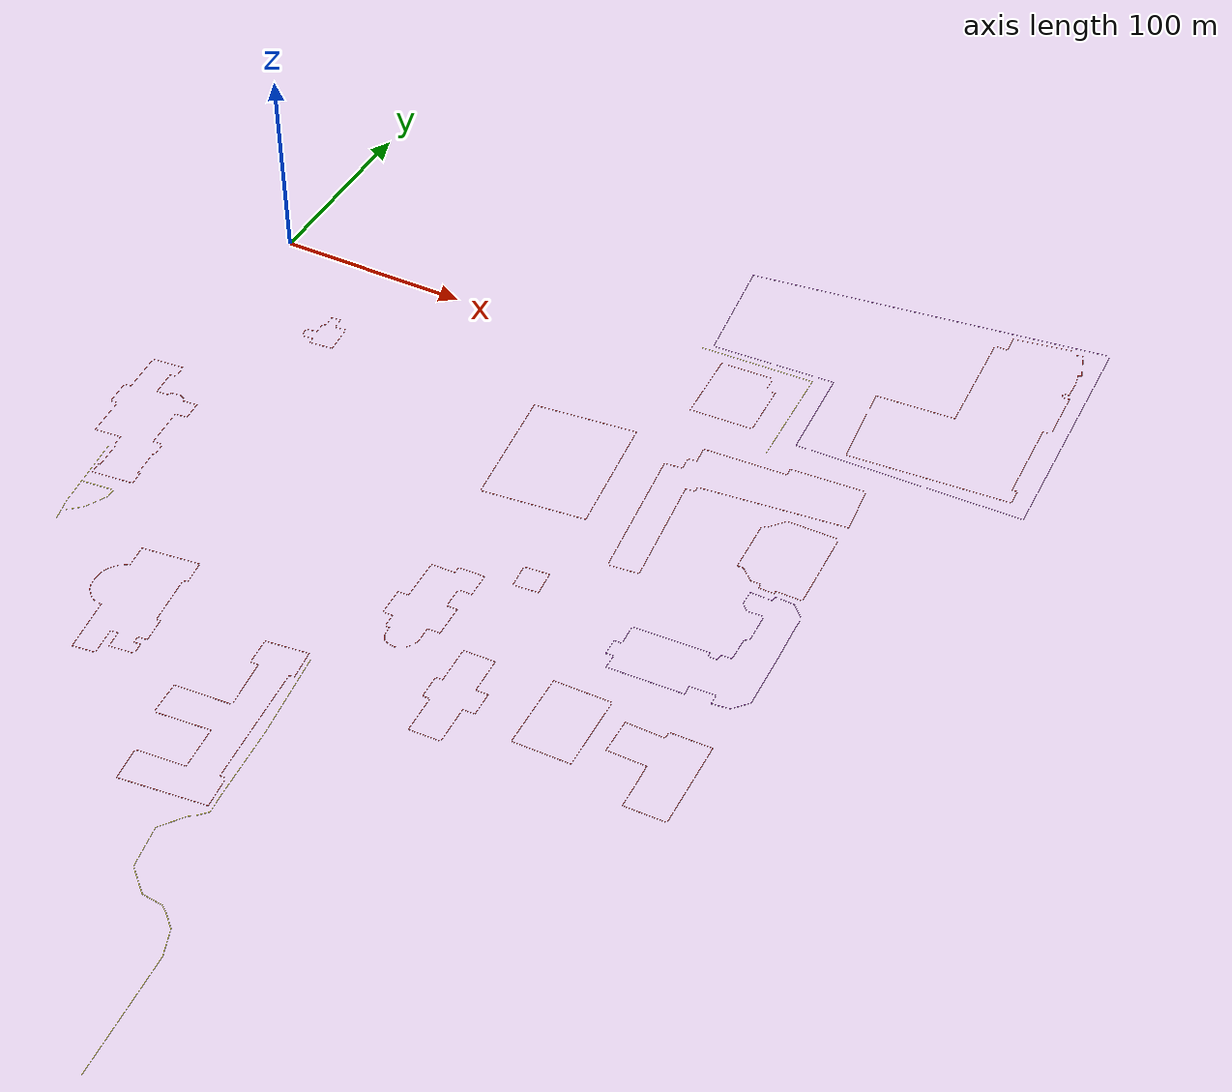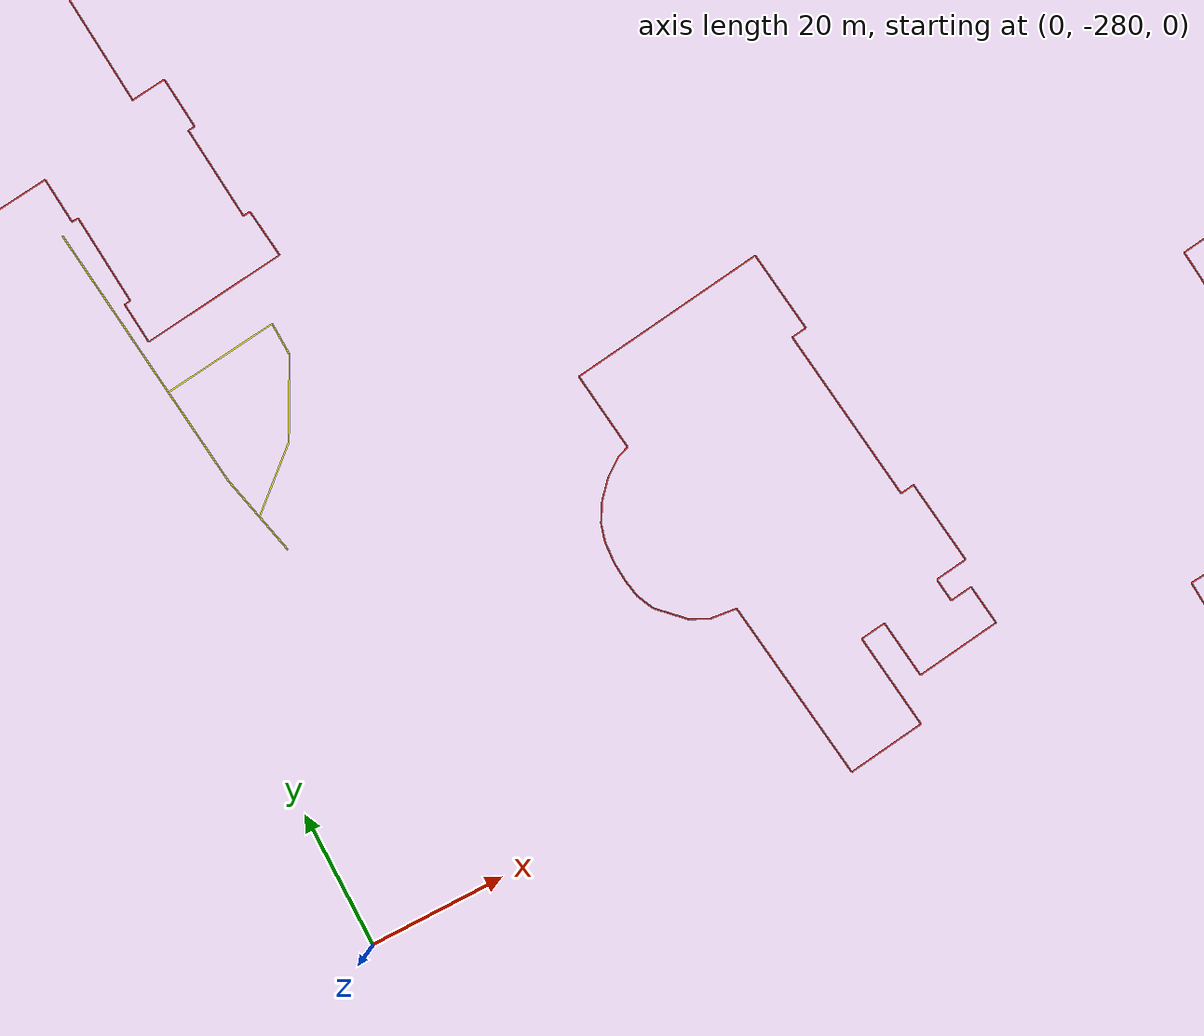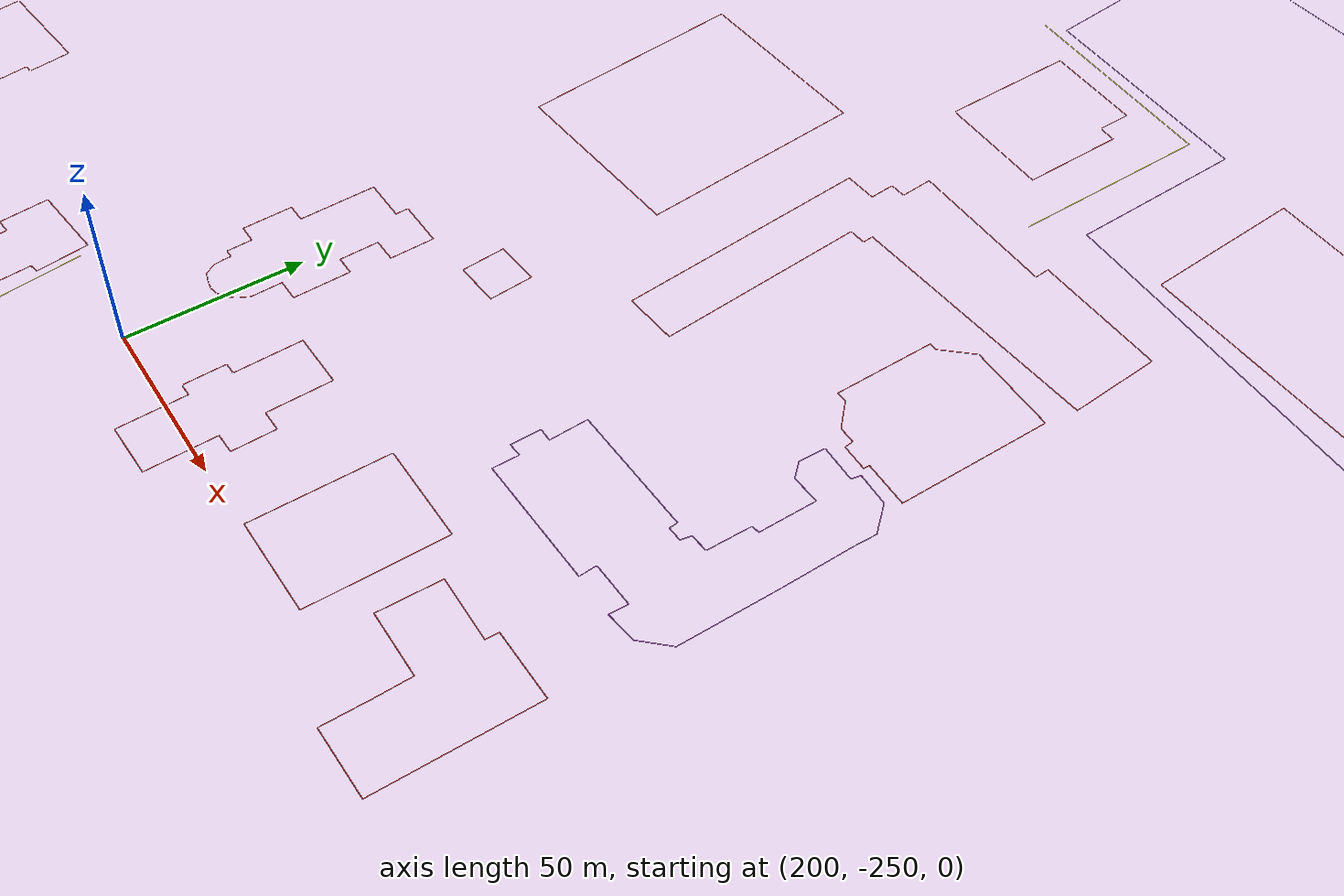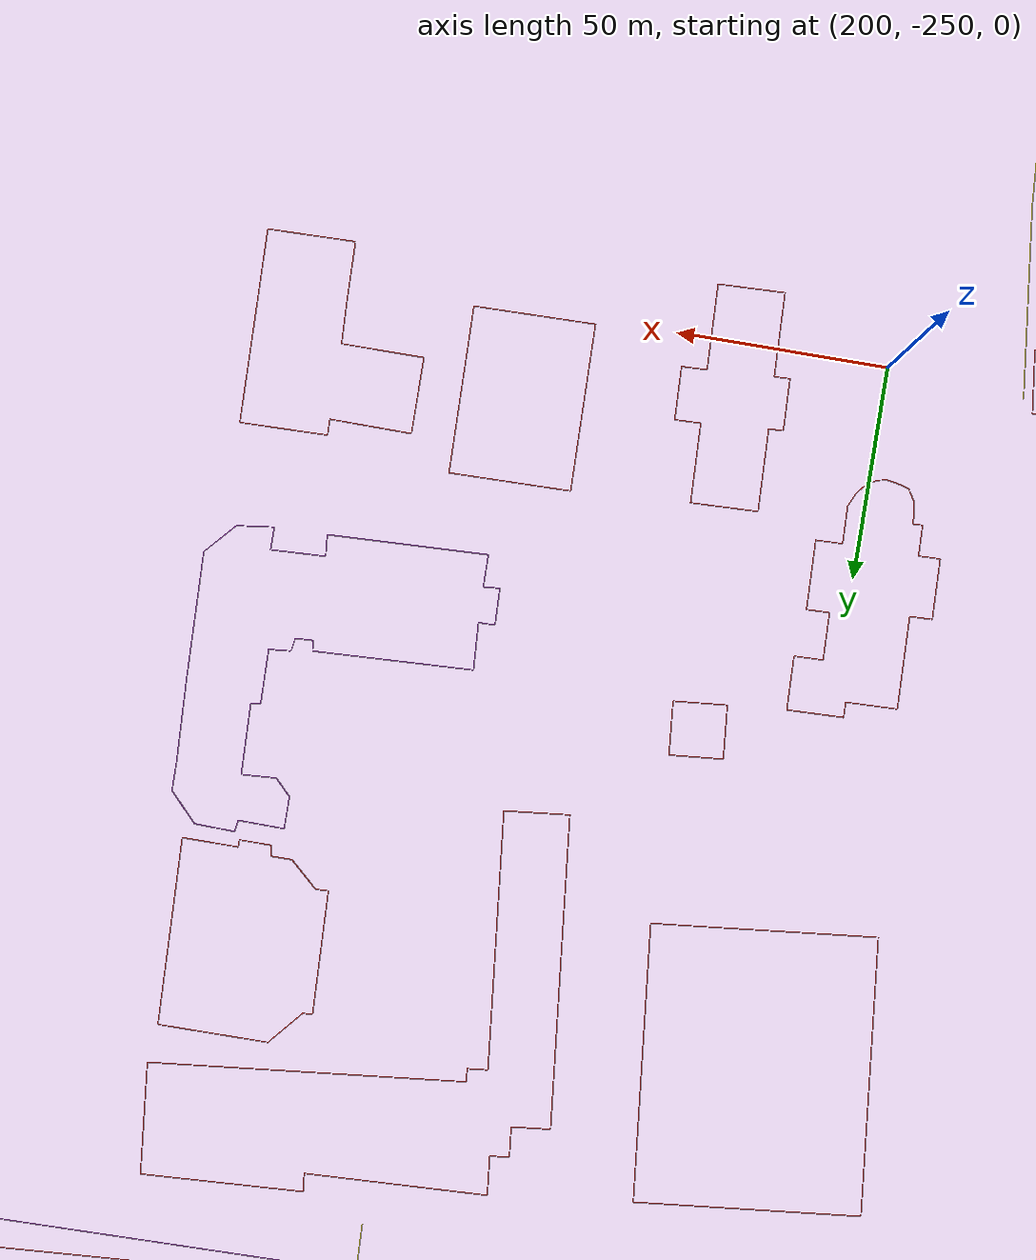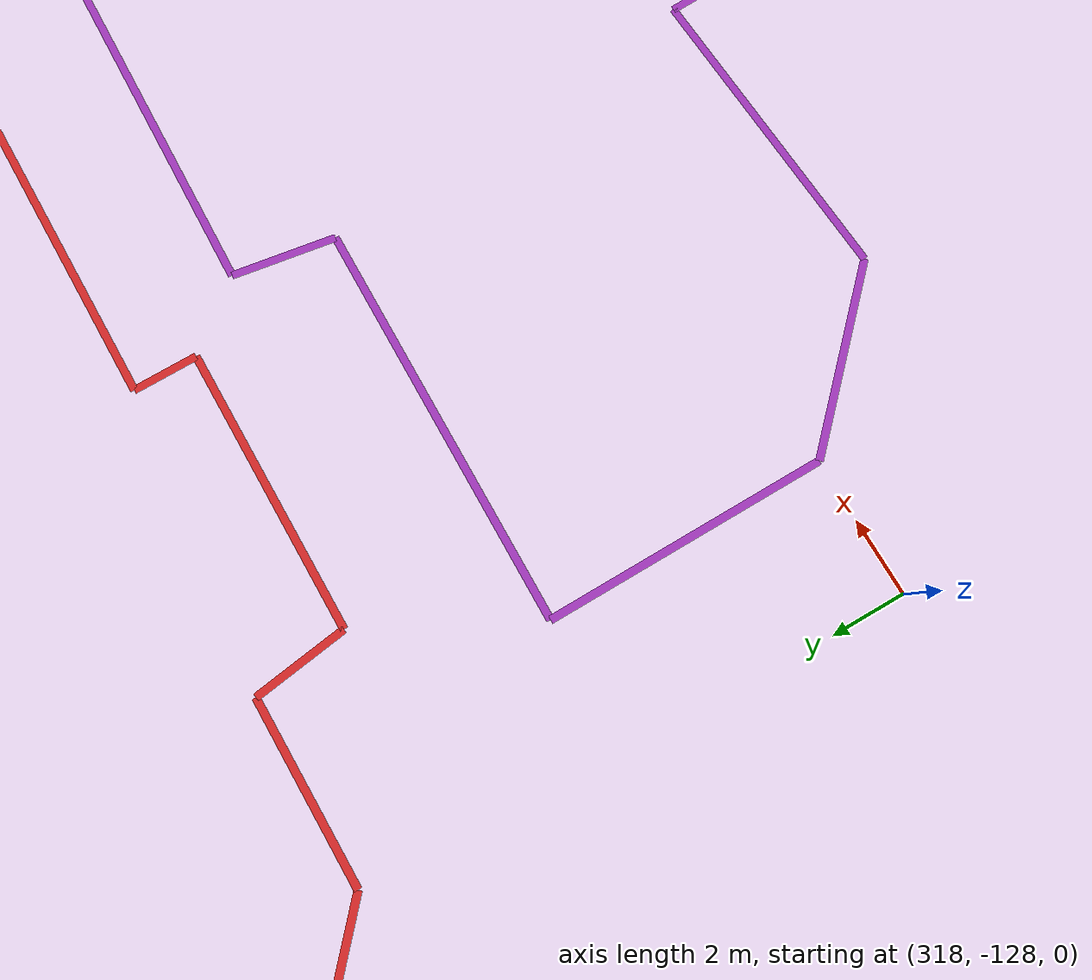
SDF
<sdf version="1.4">
 <world name="default">
  <spherical_coordinates>
   <surface_model>EARTH_WGS84</surface_model>
   <latitude_deg>40.606</latitude_deg>
   <longitude_deg>-75.38</longitude_deg>
   <elevation>0.0</elevation>
   <heading_deg>0</heading_deg>
  </spherical_coordinates>
  <include><uri>model://sun</uri></include>
  <model name="Christmas-Saucon Hall">
   <static>true</static>
   <pose>232.3241012666865 -235.43873173592942 0.0 0 0 0</pose>
   <link name="Christmas-Saucon Hall_0">
    <collision name="Christmas-Saucon Hall_0">
     <geometry><box><size>15.933763601192437 0.2 0</size></box></geometry>
    </collision>
    <visual name="Christmas-Saucon Hall_0">
     <geometry><box><size>15.933763601192437 0.2 0</size></box></geometry>
     <material>
      <script><uri>file://media/materials/scripts/gazebo.material</uri><name>Gazebo/Red</name></script>
     </material>
    </visual>
    <pose>0.06518837761345253 23.843552745387 0 0 0 -3.104999910725411</pose>
   </link>
   <link name="Christmas-Saucon Hall_1">
    <collision name="Christmas-Saucon Hall_1">
     <geometry><box><size>18.795386971462797 0.2 0</size></box></geometry>
    </collision>
    <visual name="Christmas-Saucon Hall_1">
     <geometry><box><size>18.795386971462797 0.2 0</size></box></geometry>
     <material>
      <script><uri>file://media/materials/scripts/gazebo.material</uri><name>Gazebo/Red</name></script>
     </material>
    </visual>
    <pose>8.371720010886946 14.743658448065787 0 0 0 1.607513922353306</pose>
   </link>
   <link name="Christmas-Saucon Hall_2">
    <collision name="Christmas-Saucon Hall_2">
     <geometry><box><size>6.153302198726913 0.2 0</size></box></geometry>
    </collision>
    <visual name="Christmas-Saucon Hall_2">
     <geometry><box><size>6.153302198726913 0.2 0</size></box></geometry>
     <material>
      <script><uri>file://media/materials/scripts/gazebo.material</uri><name>Gazebo/Red</name></script>
     </material>
    </visual>
    <pose>11.791239384829964 5.46635693242456 0 0 0 -3.104512100698016</pose>
   </link>
   <link name="Christmas-Saucon Hall_3">
    <collision name="Christmas-Saucon Hall_3">
     <geometry><box><size>12.569887938341257 0.2 0</size></box></geometry>
    </collision>
    <visual name="Christmas-Saucon Hall_3">
     <geometry><box><size>12.569887938341257 0.2 0</size></box></geometry>
     <material>
      <script><uri>file://media/materials/scripts/gazebo.material</uri><name>Gazebo/Red</name></script>
     </material>
    </visual>
    <pose>15.099484500722212 -0.700182457460869 0 0 0 1.6079904238363074</pose>
   </link>
   <link name="Christmas-Saucon Hall_4">
    <collision name="Christmas-Saucon Hall_4">
     <geometry><box><size>6.019648180746079 0.2 0</size></box></geometry>
    </collision>
    <visual name="Christmas-Saucon Hall_4">
     <geometry><box><size>6.019648180746079 0.2 0</size></box></geometry>
     <material>
      <script><uri>file://media/materials/scripts/gazebo.material</uri><name>Gazebo/Red</name></script>
     </material>
    </visual>
    <pose>12.325374239071891 -7.090619583085612 0 0 0 0.0365019170014352</pose>
   </link>
   <link name="Christmas-Saucon Hall_5">
    <collision name="Christmas-Saucon Hall_5">
     <geometry><box><size>20.22270035575876 0.2 0</size></box></geometry>
    </collision>
    <visual name="Christmas-Saucon Hall_5">
     <geometry><box><size>20.22270035575876 0.2 0</size></box></geometry>
     <material>
      <script><uri>file://media/materials/scripts/gazebo.material</uri><name>Gazebo/Red</name></script>
     </material>
    </visual>
    <pose>9.684841983921586 -17.30513680688236 0 0 0 1.6071285414945913</pose>
   </link>
   <link name="Christmas-Saucon Hall_6">
    <collision name="Christmas-Saucon Hall_6">
     <geometry><box><size>15.800419625036277 0.2 0</size></box></geometry>
    </collision>
    <visual name="Christmas-Saucon Hall_6">
     <geometry><box><size>15.800419625036277 0.2 0</size></box></geometry>
     <material>
      <script><uri>file://media/materials/scripts/gazebo.material</uri><name>Gazebo/Red</name></script>
     </material>
    </visual>
    <pose>2.157299435389035 -27.701331856138665 0 0 0 0.03690838373747457</pose>
   </link>
   <link name="Christmas-Saucon Hall_7">
    <collision name="Christmas-Saucon Hall_7">
     <geometry><box><size>19.817405506239165 0.2 0</size></box></geometry>
    </collision>
    <visual name="Christmas-Saucon Hall_7">
     <geometry><box><size>19.817405506239165 0.2 0</size></box></geometry>
     <material>
      <script><uri>file://media/materials/scripts/gazebo.material</uri><name>Gazebo/Red</name></script>
     </material>
    </visual>
    <pose>-6.099251378595966 -18.09075147767851 0 0 0 -1.534282795652664</pose>
   </link>
   <link name="Christmas-Saucon Hall_8">
    <collision name="Christmas-Saucon Hall_8">
     <geometry><box><size>3.716365795260075 0.2 0</size></box></geometry>
    </collision>
    <visual name="Christmas-Saucon Hall_8">
     <geometry><box><size>3.716365795260075 0.2 0</size></box></geometry>
     <material>
      <script><uri>file://media/materials/scripts/gazebo.material</uri><name>Gazebo/Red</name></script>
     </material>
    </visual>
    <pose>-8.317925775522582 -8.256247811814973 0 0 0 0.03638468973843247</pose>
   </link>
   <link name="Christmas-Saucon Hall_9">
    <collision name="Christmas-Saucon Hall_9">
     <geometry><box><size>4.223720600512749 0.2 0</size></box></geometry>
    </collision>
    <visual name="Christmas-Saucon Hall_9">
     <geometry><box><size>4.223720600512749 0.2 0</size></box></geometry>
     <material>
      <script><uri>file://media/materials/scripts/gazebo.material</uri><name>Gazebo/Red</name></script>
     </material>
    </visual>
    <pose>-10.252783911305158 -6.213419424913411 0 0 0 -1.5338986417980867</pose>
   </link>
   <link name="Christmas-Saucon Hall_10">
    <collision name="Christmas-Saucon Hall_10">
     <geometry><box><size>8.058977816332352 0.2 0</size></box></geometry>
    </collision>
    <visual name="Christmas-Saucon Hall_10">
     <geometry><box><size>8.058977816332352 0.2 0</size></box></geometry>
     <material>
      <script><uri>file://media/materials/scripts/gazebo.material</uri><name>Gazebo/Red</name></script>
     </material>
    </visual>
    <pose>-10.480929754070019 -0.07630949939425591 0 0 0 -1.5335023665676908</pose>
   </link>
   <link name="Christmas-Saucon Hall_11">
    <collision name="Christmas-Saucon Hall_11">
     <geometry><box><size>3.4493677073714966 0.2 0</size></box></geometry>
    </collision>
    <visual name="Christmas-Saucon Hall_11">
     <geometry><box><size>3.4493677073714966 0.2 0</size></box></geometry>
     <material>
      <script><uri>file://media/materials/scripts/gazebo.material</uri><name>Gazebo/Red</name></script>
     </material>
    </visual>
    <pose>-8.907651129691374 4.013743973806498 0 0 0 -3.1048434886776333</pose>
   </link>
   <link name="Christmas-Saucon Hall_12">
    <collision name="Christmas-Saucon Hall_12">
     <geometry><box><size>19.487996607862186 0.2 0</size></box></geometry>
    </collision>
    <visual name="Christmas-Saucon Hall_12">
     <geometry><box><size>19.487996607862186 0.2 0</size></box></geometry>
     <material>
      <script><uri>file://media/materials/scripts/gazebo.material</uri><name>Gazebo/Red</name></script>
     </material>
    </visual>
    <pose>-7.540245907312112 13.814599072622002 0 0 0 -1.5342411590625953</pose>
   </link>
  </model>
  <model name="parking_aisle_190491976">
   <static>true</static>
   <pose>267.14215448727913 5.537774229259294 0.0 0 0 0</pose>
   <link name="parking_aisle_190491976_0">
    <collision name="parking_aisle_190491976_0">
     <geometry><box><size>60.04894569524231 0.2 0</size></box></geometry>
    </collision>
    <visual name="parking_aisle_190491976_0">
     <geometry><box><size>60.04894569524231 0.2 0</size></box></geometry>
     <material>
      <script><uri>file://media/materials/scripts/gazebo.material</uri><name>Gazebo/Yellow</name></script>
     </material>
    </visual>
    <pose>-10.648777250347848 18.812197792441268 0 0 0 -3.112210545009683</pose>
   </link>
   <link name="parking_aisle_190491976_1">
    <collision name="parking_aisle_190491976_1">
     <geometry><box><size>57.35129482673212 0.2 0</size></box></geometry>
    </collision>
    <visual name="parking_aisle_190491976_1">
     <geometry><box><size>57.35129482673212 0.2 0</size></box></geometry>
     <material>
      <script><uri>file://media/materials/scripts/gazebo.material</uri><name>Gazebo/Yellow</name></script>
     </material>
    </visual>
    <pose>20.33014542097652 -8.96507119912346 0 0 0 1.6045389888828343</pose>
   </link>
  </model>
  <model name="Chandler-Ullman Hall">
   <static>true</static>
   <pose>150.24254922470425 -291.0185620396773 0.0 0 0 0</pose>
   <link name="Chandler-Ullman Hall_0">
    <collision name="Chandler-Ullman Hall_0">
     <geometry><box><size>21.55234201603994 0.2 0</size></box></geometry>
    </collision>
    <visual name="Chandler-Ullman Hall_0">
     <geometry><box><size>21.55234201603994 0.2 0</size></box></geometry>
     <material>
      <script><uri>file://media/materials/scripts/gazebo.material</uri><name>Gazebo/Red</name></script>
     </material>
    </visual>
    <pose>3.899939848906797 44.717000793700294 0 0 0 -3.0202306769596574</pose>
   </link>
   <link name="Chandler-Ullman Hall_1">
    <collision name="Chandler-Ullman Hall_1">
     <geometry><box><size>14.931220862070667 0.2 0</size></box></geometry>
    </collision>
    <visual name="Chandler-Ullman Hall_1">
     <geometry><box><size>14.931220862070667 0.2 0</size></box></geometry>
     <material>
      <script><uri>file://media/materials/scripts/gazebo.material</uri><name>Gazebo/Red</name></script>
     </material>
    </visual>
    <pose>15.525577797804885 38.61399238050069 0 0 0 1.695520423103847</pose>
   </link>
   <link name="Chandler-Ullman Hall_2">
    <collision name="Chandler-Ullman Hall_2">
     <geometry><box><size>2.62486411601787 0.2 0</size></box></geometry>
    </collision>
    <visual name="Chandler-Ullman Hall_2">
     <geometry><box><size>2.62486411601787 0.2 0</size></box></geometry>
     <material>
      <script><uri>file://media/materials/scripts/gazebo.material</uri><name>Gazebo/Red</name></script>
     </material>
    </visual>
    <pose>15.17557571960188 30.910868035982105 0 0 0 0.2271067544069681</pose>
   </link>
   <link name="Chandler-Ullman Hall_3">
    <collision name="Chandler-Ullman Hall_3">
     <geometry><box><size>62.6678898911332 0.2 0</size></box></geometry>
    </collision>
    <visual name="Chandler-Ullman Hall_3">
     <geometry><box><size>62.6678898911332 0.2 0</size></box></geometry>
     <material>
      <script><uri>file://media/materials/scripts/gazebo.material</uri><name>Gazebo/Red</name></script>
     </material>
    </visual>
    <pose>16.4444338150725 -0.6148465699030226 0 0 0 1.6521906283166883</pose>
   </link>
   <link name="Chandler-Ullman Hall_4">
    <collision name="Chandler-Ullman Hall_4">
     <geometry><box><size>3.0360440323808424 0.2 0</size></box></geometry>
    </collision>
    <visual name="Chandler-Ullman Hall_4">
     <geometry><box><size>3.0360440323808424 0.2 0</size></box></geometry>
     <material>
      <script><uri>file://media/materials/scripts/gazebo.material</uri><name>Gazebo/Red</name></script>
     </material>
    </visual>
    <pose>20.50983507371234 -31.87031393801948 0 0 0 3.1249522515619637</pose>
   </link>
   <link name="Chandler-Ullman Hall_5">
    <collision name="Chandler-Ullman Hall_5">
     <geometry><box><size>16.186833406219105 0.2 0</size></box></geometry>
    </collision>
    <visual name="Chandler-Ullman Hall_5">
     <geometry><box><size>16.186833406219105 0.2 0</size></box></geometry>
     <material>
      <script><uri>file://media/materials/scripts/gazebo.material</uri><name>Gazebo/Red</name></script>
     </material>
    </visual>
    <pose>22.91200487677122 -39.940528516657025 0 0 0 1.6802837452530803</pose>
   </link>
   <link name="Chandler-Ullman Hall_6">
    <collision name="Chandler-Ullman Hall_6">
     <geometry><box><size>43.36819591456272 0.2 0</size></box></geometry>
    </collision>
    <visual name="Chandler-Ullman Hall_6">
     <geometry><box><size>43.36819591456272 0.2 0</size></box></geometry>
     <material>
      <script><uri>file://media/materials/scripts/gazebo.material</uri><name>Gazebo/Red</name></script>
     </material>
    </visual>
    <pose>2.2524588772196807 -50.44725277118954 0 0 0 0.11377407171852401</pose>
   </link>
   <link name="Chandler-Ullman Hall_7">
    <collision name="Chandler-Ullman Hall_7">
     <geometry><box><size>16.78389465613207 0.2 0</size></box></geometry>
    </collision>
    <visual name="Chandler-Ullman Hall_7">
     <geometry><box><size>16.78389465613207 0.2 0</size></box></geometry>
     <material>
      <script><uri>file://media/materials/scripts/gazebo.material</uri><name>Gazebo/Red</name></script>
     </material>
    </visual>
    <pose>-20.29257568428892 -44.577004167331324 0 0 0 -1.4512149550978246</pose>
   </link>
   <link name="Chandler-Ullman Hall_8">
    <collision name="Chandler-Ullman Hall_8">
     <geometry><box><size>24.671153216072028 0.2 0</size></box></geometry>
    </collision>
    <visual name="Chandler-Ullman Hall_8">
     <geometry><box><size>24.671153216072028 0.2 0</size></box></geometry>
     <material>
      <script><uri>file://media/materials/scripts/gazebo.material</uri><name>Gazebo/Red</name></script>
     </material>
    </visual>
    <pose>-9.00671488599474 -35.1512350099855 0 0 0 -3.052809631405263</pose>
   </link>
   <link name="Chandler-Ullman Hall_9">
    <collision name="Chandler-Ullman Hall_9">
     <geometry><box><size>22.110400812638773 0.2 0</size></box></geometry>
    </collision>
    <visual name="Chandler-Ullman Hall_9">
     <geometry><box><size>22.110400812638773 0.2 0</size></box></geometry>
     <material>
      <script><uri>file://media/materials/scripts/gazebo.material</uri><name>Gazebo/Red</name></script>
     </material>
    </visual>
    <pose>2.306855511822505 -23.045221771625734 0 0 0 -1.4826311919782764</pose>
   </link>
   <link name="Chandler-Ullman Hall_10">
    <collision name="Chandler-Ullman Hall_10">
     <geometry><box><size>27.996417084981534 0.2 0</size></box></geometry>
    </collision>
    <visual name="Chandler-Ullman Hall_10">
     <geometry><box><size>27.996417084981534 0.2 0</size></box></geometry>
     <material>
      <script><uri>file://media/materials/scripts/gazebo.material</uri><name>Gazebo/Red</name></script>
     </material>
    </visual>
    <pose>-12.610358825543784 -13.266033470805553 0 0 0 0.0882022617642962</pose>
   </link>
   <link name="Chandler-Ullman Hall_11">
    <collision name="Chandler-Ullman Hall_11">
     <geometry><box><size>17.184908452739233 0.2 0</size></box></geometry>
    </collision>
    <visual name="Chandler-Ullman Hall_11">
     <geometry><box><size>17.184908452739233 0.2 0</size></box></geometry>
     <material>
      <script><uri>file://media/materials/scripts/gazebo.material</uri><name>Gazebo/Red</name></script>
     </material>
    </visual>
    <pose>-27.071551273948444 -5.92224451086156 0 0 0 -1.5105443556603089</pose>
   </link>
   <link name="Chandler-Ullman Hall_12">
    <collision name="Chandler-Ullman Hall_12">
     <geometry><box><size>28.781927330690262 0.2 0</size></box></geometry>
    </collision>
    <visual name="Chandler-Ullman Hall_12">
     <geometry><box><size>28.781927330690262 0.2 0</size></box></geometry>
     <material>
      <script><uri>file://media/materials/scripts/gazebo.material</uri><name>Gazebo/Red</name></script>
     </material>
    </visual>
    <pose>-13.233724539529504 3.668188712286849 0 0 0 -3.0711032306671906</pose>
   </link>
   <link name="Chandler-Ullman Hall_13">
    <collision name="Chandler-Ullman Hall_13">
     <geometry><box><size>25.377939510984604 0.2 0</size></box></geometry>
    </collision>
    <visual name="Chandler-Ullman Hall_13">
     <geometry><box><size>25.377939510984604 0.2 0</size></box></geometry>
     <material>
      <script><uri>file://media/materials/scripts/gazebo.material</uri><name>Gazebo/Red</name></script>
     </material>
    </visual>
    <pose>-0.23554148570542566 17.29795506095769 0 0 0 -1.463644752324978</pose>
   </link>
   <link name="Chandler-Ullman Hall_14">
    <collision name="Chandler-Ullman Hall_14">
     <geometry><box><size>4.008368159693659 0.2 0</size></box></geometry>
    </collision>
    <visual name="Chandler-Ullman Hall_14">
     <geometry><box><size>4.008368159693659 0.2 0</size></box></geometry>
     <material>
      <script><uri>file://media/materials/scripts/gazebo.material</uri><name>Gazebo/Red</name></script>
     </material>
    </visual>
    <pose>-3.5885268365446166 29.732581932521782 0 0 0 0.0907191592088989</pose>
   </link>
   <link name="Chandler-Ullman Hall_15">
    <collision name="Chandler-Ullman Hall_15">
     <geometry><box><size>13.914307668703524 0.2 0</size></box></geometry>
    </collision>
    <visual name="Chandler-Ullman Hall_15">
     <geometry><box><size>13.914307668703524 0.2 0</size></box></geometry>
     <material>
      <script><uri>file://media/materials/scripts/gazebo.material</uri><name>Gazebo/Red</name></script>
     </material>
    </visual>
    <pose>-6.190719125700298 36.48170237941122 0 0 0 -1.4835451833009348</pose>
   </link>
  </model>
  <model name="President's House">
   <static>true</static>
   <pose>53.58331149262828 -52.19817419002547 0.0 0 0 0</pose>
   <link name="President's House_0">
    <collision name="President's House_0">
     <geometry><box><size>15.475143812544966 0.2 0</size></box></geometry>
    </collision>
    <visual name="President's House_0">
     <geometry><box><size>15.475143812544966 0.2 0</size></box></geometry>
     <material>
      <script><uri>file://media/materials/scripts/gazebo.material</uri><name>Gazebo/Red</name></script>
     </material>
    </visual>
    <pose>9.592290137162976 -2.332162736316292 0 0 0 1.6650718159180202</pose>
   </link>
   <link name="President's House_1">
    <collision name="President's House_1">
     <geometry><box><size>12.420041905299907 0.2 0</size></box></geometry>
    </collision>
    <visual name="President's House_1">
     <geometry><box><size>12.420041905299907 0.2 0</size></box></geometry>
     <material>
      <script><uri>file://media/materials/scripts/gazebo.material</uri><name>Gazebo/Red</name></script>
     </material>
    </visual>
    <pose>4.149360863456025 -10.727661942391975 0 0 0 0.11171123097035161</pose>
   </link>
   <link name="President's House_2">
    <collision name="President's House_2">
     <geometry><box><size>3.4201013517765557 0.2 0</size></box></geometry>
    </collision>
    <visual name="President's House_2">
     <geometry><box><size>3.4201013517765557 0.2 0</size></box></geometry>
     <material>
      <script><uri>file://media/materials/scripts/gazebo.material</uri><name>Gazebo/Red</name></script>
     </material>
    </visual>
    <pose>-2.149840076689074 -9.714687219363334 0 0 0 -1.495940131858904</pose>
   </link>
   <link name="President's House_3">
    <collision name="President's House_3">
     <geometry><box><size>6.078782774064744 0.2 0</size></box></geometry>
    </collision>
    <visual name="President's House_3">
     <geometry><box><size>6.078782774064744 0.2 0</size></box></geometry>
     <material>
      <script><uri>file://media/materials/scripts/gazebo.material</uri><name>Gazebo/Red</name></script>
     </material>
    </visual>
    <pose>-5.291107725287901 -8.406219227129618 0 0 0 0.13092413299408304</pose>
   </link>
   <link name="President's House_4">
    <collision name="President's House_4">
     <geometry><box><size>5.504191082136553 0.2 0</size></box></geometry>
    </collision>
    <visual name="President's House_4">
     <geometry><box><size>5.504191082136553 0.2 0</size></box></geometry>
     <material>
      <script><uri>file://media/materials/scripts/gazebo.material</uri><name>Gazebo/Red</name></script>
     </material>
    </visual>
    <pose>-8.760407487603914 -6.088944822198741 0 0 0 -1.404366033510363</pose>
   </link>
   <link name="President's House_5">
    <collision name="President's House_5">
     <geometry><box><size>5.971391826745336 0.2 0</size></box></geometry>
    </collision>
    <visual name="President's House_5">
     <geometry><box><size>5.971391826745336 0.2 0</size></box></geometry>
     <material>
      <script><uri>file://media/materials/scripts/gazebo.material</uri><name>Gazebo/Red</name></script>
     </material>
    </visual>
    <pose>-6.269665985354777 -2.8936664345414016 0 0 0 -2.9797147353626126</pose>
   </link>
   <link name="President's House_6">
    <collision name="President's House_6">
     <geometry><box><size>6.206355874636193 0.2 0</size></box></geometry>
    </collision>
    <visual name="President's House_6">
     <geometry><box><size>6.206355874636193 0.2 0</size></box></geometry>
     <material>
      <script><uri>file://media/materials/scripts/gazebo.material</uri><name>Gazebo/Red</name></script>
     </material>
    </visual>
    <pose>-3.5620945368303722 0.6814973428817765 0 0 0 -1.4936728975841946</pose>
   </link>
   <link name="President's House_7">
    <collision name="President's House_7">
     <geometry><box><size>1.8406470404480435 0.2 0</size></box></geometry>
    </collision>
    <visual name="President's House_7">
     <geometry><box><size>1.8406470404480435 0.2 0</size></box></geometry>
     <material>
      <script><uri>file://media/materials/scripts/gazebo.material</uri><name>Gazebo/Red</name></script>
     </material>
    </visual>
    <pose>-2.8949474659747167 3.9358528817781675 0 0 0 -2.966409369846677</pose>
   </link>
   <link name="President's House_8">
    <collision name="President's House_8">
     <geometry><box><size>5.997771046637297 0.2 0</size></box></geometry>
    </collision>
    <visual name="President's House_8">
     <geometry><box><size>5.997771046637297 0.2 0</size></box></geometry>
     <material>
      <script><uri>file://media/materials/scripts/gazebo.material</uri><name>Gazebo/Red</name></script>
     </material>
    </visual>
    <pose>-2.2389165816849683 7.084684313823246 0 0 0 -1.487265987389361</pose>
   </link>
   <link name="President's House_9">
    <collision name="President's House_9">
     <geometry><box><size>4.930551719106037 0.2 0</size></box></geometry>
    </collision>
    <visual name="President's House_9">
     <geometry><box><size>4.930551719106037 0.2 0</size></box></geometry>
     <material>
      <script><uri>file://media/materials/scripts/gazebo.material</uri><name>Gazebo/Red</name></script>
     </material>
    </visual>
    <pose>-0.0539565722061397 10.457233643977496 0 0 0 -2.985143110456578</pose>
   </link>
   <link name="President's House_10">
    <collision name="President's House_10">
     <geometry><box><size>6.344080420048689 0.2 0</size></box></geometry>
    </collision>
    <visual name="President's House_10">
     <geometry><box><size>6.344080420048689 0.2 0</size></box></geometry>
     <material>
      <script><uri>file://media/materials/scripts/gazebo.material</uri><name>Gazebo/Red</name></script>
     </material>
    </visual>
    <pose>2.6870151239810696 7.684088435293745 0 0 0 1.6673526860360703</pose>
   </link>
   <link name="President's House_11">
    <collision name="President's House_11">
     <geometry><box><size>5.931473442908504 0.2 0</size></box></geometry>
    </collision>
    <visual name="President's House_11">
     <geometry><box><size>5.931473442908504 0.2 0</size></box></geometry>
     <material>
      <script><uri>file://media/materials/scripts/gazebo.material</uri><name>Gazebo/Red</name></script>
     </material>
    </visual>
    <pose>5.928363463703235 4.948936392427726 0 0 0 -2.9987777816759014</pose>
   </link>
  </model>
  <model name="STEPS">
   <static>true</static>
   <pose>283.5688985029477 -64.22061516094757 0.0 0 0 0</pose>
   <link name="STEPS_0">
    <collision name="STEPS_0"><geometry><box><size>26.190423533240267 0.2 0</size></box></geometry></collision>
    <visual name="STEPS_0">
     <geometry><box><size>26.190423533240267 0.2 0</size></box></geometry>
     <material>
      <script><uri>file://media/materials/scripts/gazebo.material</uri><name>Gazebo/Red</name></script>
     </material>
    </visual>
    <pose>59.35086359420268 15.968635674466952 0 0 0 1.674155602807987</pose>
   </link>
   <link name="STEPS_1">
    <collision name="STEPS_1"><geometry><box><size>74.80039718745135 0.2 0</size></box></geometry></collision>
    <visual name="STEPS_1">
     <geometry><box><size>74.80039718745135 0.2 0</size></box></geometry>
     <material>
      <script><uri>file://media/materials/scripts/gazebo.material</uri><name>Gazebo/Red</name></script>
     </material>
    </visual>
    <pose>23.501737674925437 -0.9190497722359368 0 0 0 0.10345557030246565</pose>
   </link>
   <link name="STEPS_2">
    <collision name="STEPS_2"><geometry><box><size>3.0896335058153985 0.2 0</size></box></geometry></collision>
    <visual name="STEPS_2">
     <geometry><box><size>3.0896335058153985 0.2 0</size></box></geometry>
     <material>
      <script><uri>file://media/materials/scripts/gazebo.material</uri><name>Gazebo/Red</name></script>
     </material>
    </visual>
    <pose>-13.53724395279255 -6.317788443052592 0 0 0 1.6753663166850095</pose>
   </link>
   <link name="STEPS_3">
    <collision name="STEPS_3"><geometry><box><size>4.873614992773722 0.2 0</size></box></geometry></collision>
    <visual name="STEPS_3">
     <geometry><box><size>4.873614992773722 0.2 0</size></box></geometry>
     <material>
      <script><uri>file://media/materials/scripts/gazebo.material</uri><name>Gazebo/Red</name></script>
     </material>
    </visual>
    <pose>-15.800043702845187 -8.103218953361775 0 0 0 0.10238309694406908</pose>
   </link>
   <link name="STEPS_4">
    <collision name="STEPS_4"><geometry><box><size>60.76669053011377 0.2 0</size></box></geometry></collision>
    <visual name="STEPS_4">
     <geometry><box><size>60.76669053011377 0.2 0</size></box></geometry>
     <material>
      <script><uri>file://media/materials/scripts/gazebo.material</uri><name>Gazebo/Red</name></script>
     </material>
    </visual>
    <pose>-15.087975707877945 -38.57333096153519 0 0 0 1.6741987174469668</pose>
   </link>
   <link name="STEPS_5">
    <collision name="STEPS_5"><geometry><box><size>15.471861021532753 0.2 0</size></box></geometry></collision>
    <visual name="STEPS_5">
     <geometry><box><size>15.471861021532753 0.2 0</size></box></geometry>
     <material>
      <script><uri>file://media/materials/scripts/gazebo.material</uri><name>Gazebo/Red</name></script>
     </material>
    </visual>
    <pose>-19.64653529408224 -69.5922655825643 0 0 0 0.10332257596499182</pose>
   </link>
   <link name="STEPS_6">
    <collision name="STEPS_6"><geometry><box><size>73.73566771659716 0.2 0</size></box></geometry></collision>
    <visual name="STEPS_6">
     <geometry><box><size>73.73566771659716 0.2 0</size></box></geometry>
     <material>
      <script><uri>file://media/materials/scripts/gazebo.material</uri><name>Gazebo/Red</name></script>
     </material>
    </visual>
    <pose>-31.150119391585292 -33.71958848771678 0 0 0 -1.4672991149176886</pose>
   </link>
   <link name="STEPS_7">
    <collision name="STEPS_7"><geometry><box><size>9.222174566372932 0.2 0</size></box></geometry></collision>
    <visual name="STEPS_7">
     <geometry><box><size>9.222174566372932 0.2 0</size></box></geometry>
     <material>
      <script><uri>file://media/materials/scripts/gazebo.material</uri><name>Gazebo/Red</name></script>
     </material>
    </visual>
    <pose>-30.372242074344513 3.423734317340518 0 0 0 -3.0388830181322333</pose>
   </link>
   <link name="STEPS_8">
    <collision name="STEPS_8"><geometry><box><size>7.103681535042522 0.2 0</size></box></geometry></collision>
    <visual name="STEPS_8">
     <geometry><box><size>7.103681535042522 0.2 0</size></box></geometry>
     <material>
      <script><uri>file://media/materials/scripts/gazebo.material</uri><name>Gazebo/Red</name></script>
     </material>
    </visual>
    <pose>-26.152425474431993 7.429337683613852 0 0 0 -1.4672932931679354</pose>
   </link>
   <link name="STEPS_9">
    <collision name="STEPS_9"><geometry><box><size>4.605556826808261 0.2 0</size></box></geometry></collision>
    <visual name="STEPS_9">
     <geometry><box><size>4.605556826808261 0.2 0</size></box></geometry>
     <material>
      <script><uri>file://media/materials/scripts/gazebo.material</uri><name>Gazebo/Red</name></script>
     </material>
    </visual>
    <pose>-24.228781928778403 11.198553015308931 0 0 0 -3.038760387495583</pose>
   </link>
   <link name="STEPS_10">
    <collision name="STEPS_10"><geometry><box><size>9.216232434000752 0.2 0</size></box></geometry></collision>
    <visual name="STEPS_10">
     <geometry><box><size>9.216232434000752 0.2 0</size></box></geometry>
     <material>
      <script><uri>file://media/materials/scripts/gazebo.material</uri><name>Gazebo/Red</name></script>
     </material>
    </visual>
    <pose>-22.410776297319217 16.018752633544253 0 0 0 -1.46805572306853</pose>
   </link>
   <link name="STEPS_11">
    <collision name="STEPS_11"><geometry><box><size>43.13290366147631 0.2 0</size></box></geometry></collision>
    <visual name="STEPS_11">
     <geometry><box><size>43.13290366147631 0.2 0</size></box></geometry>
     <material>
      <script><uri>file://media/materials/scripts/gazebo.material</uri><name>Gazebo/Red</name></script>
     </material>
    </visual>
    <pose>-1.3393730732883569 21.586143332112684 0 0 0 -3.0959701664700052</pose>
   </link>
   <link name="STEPS_12">
    <collision name="STEPS_12"><geometry><box><size>4.2766149400865565 0.2 0</size></box></geometry></collision>
    <visual name="STEPS_12">
     <geometry><box><size>4.2766149400865565 0.2 0</size></box></geometry>
     <material>
      <script><uri>file://media/materials/scripts/gazebo.material</uri><name>Gazebo/Red</name></script>
     </material>
    </visual>
    <pose>19.987796900413343 24.697001549724874 0 0 0 -1.4692137407813042</pose>
   </link>
   <link name="STEPS_13">
    <collision name="STEPS_13"><geometry><box><size>38.29032559633885 0.2 0</size></box></geometry></collision>
    <visual name="STEPS_13">
     <geometry><box><size>38.29032559633885 0.2 0</size></box></geometry>
     <material>
      <script><uri>file://media/materials/scripts/gazebo.material</uri><name>Gazebo/Red</name></script>
     </material>
    </visual>
    <pose>38.88535806902229 27.909123292445216 0 0 0 -3.084898501067902</pose>
   </link>
  </model>
  <model name="parking_aisle_190538848">
   <static>true</static>
   <pose>19.775564759976287 -206.81212770353414 0.0 0 0 0</pose>
   <link name="parking_aisle_190538848_0">
    <collision name="parking_aisle_190538848_0">
     <geometry><box><size>17.163761593035105 0.2 0</size></box></geometry>
    </collision>
    <visual name="parking_aisle_190538848_0">
     <geometry><box><size>17.163761593035105 0.2 0</size></box></geometry>
     <material>
      <script><uri>file://media/materials/scripts/gazebo.material</uri><name>Gazebo/Yellow</name></script>
     </material>
    </visual>
    <pose>-1.2756337232460382 8.165003797641134 0 0 0 -3.0361154894260034</pose>
   </link>
   <link name="parking_aisle_190538848_1">
    <collision name="parking_aisle_190538848_1">
     <geometry><box><size>4.907227168452633 0.2 0</size></box></geometry>
    </collision>
    <visual name="parking_aisle_190538848_1">
     <geometry><box><size>4.907227168452633 0.2 0</size></box></geometry>
     <material>
      <script><uri>file://media/materials/scripts/gazebo.material</uri><name>Gazebo/Yellow</name></script>
     </material>
    </visual>
    <pose>7.336455262397511 6.616142172259629 0 0 0 1.602551778207987</pose>
   </link>
   <link name="parking_aisle_190538848_2">
    <collision name="parking_aisle_190538848_2">
     <geometry><box><size>12.18904508460777 0.2 0</size></box></geometry>
    </collision>
    <visual name="parking_aisle_190538848_2">
     <geometry><box><size>12.18904508460777 0.2 0</size></box></geometry>
     <material>
      <script><uri>file://media/materials/scripts/gazebo.material</uri><name>Gazebo/Yellow</name></script>
     </material>
    </visual>
    <pose>4.562358678008199 -1.222263187310773 0 0 0 1.083814134471724</pose>
   </link>
   <link name="parking_aisle_190538848_3">
    <collision name="parking_aisle_190538848_3">
     <geometry><box><size>11.026285997669028 0.2 0</size></box></geometry>
    </collision>
    <visual name="parking_aisle_190538848_3">
     <geometry><box><size>11.026285997669028 0.2 0</size></box></geometry>
     <material>
      <script><uri>file://media/materials/scripts/gazebo.material</uri><name>Gazebo/Yellow</name></script>
     </material>
    </visual>
    <pose>-2.4315451641984147 -10.246886600997072 0 0 0 0.720799503970968</pose>
   </link>
  </model>
  <model name="St. Peter's Evangelical Lutheran Church">
   <static>true</static>
   <pose>262.67579414051795 4.387245519786149 0.0 0 0 0</pose>
   <link name="St. Peter's Evangelical Lutheran Church_0">
    <collision name="St. Peter's Evangelical Lutheran Church_0">
     <geometry><box><size>9.579859686318986 0.2 0</size></box></geometry>
    </collision>
    <visual name="St. Peter's Evangelical Lutheran Church_0">
     <geometry><box><size>9.579859686318986 0.2 0</size></box></geometry>
     <material>
      <script><uri>file://media/materials/scripts/gazebo.material</uri><name>Gazebo/Red</name></script>
     </material>
    </visual>
    <pose>6.110156198941127 9.17004220431171 0 0 0 1.6091074899049393</pose>
   </link>
   <link name="St. Peter's Evangelical Lutheran Church_1">
    <collision name="St. Peter's Evangelical Lutheran Church_1">
     <geometry><box><size>5.007537167623495 0.2 0</size></box></geometry>
    </collision>
    <visual name="St. Peter's Evangelical Lutheran Church_1">
     <geometry><box><size>5.007537167623495 0.2 0</size></box></geometry>
     <material>
      <script><uri>file://media/materials/scripts/gazebo.material</uri><name>Gazebo/Red</name></script>
     </material>
    </visual>
    <pose>8.795505060636401 4.4807030674414525 0 0 0 -3.1028110038913224</pose>
   </link>
   <link name="St. Peter's Evangelical Lutheran Church_2">
    <collision name="St. Peter's Evangelical Lutheran Church_2">
     <geometry><box><size>28.84163988824956 0.2 0</size></box></geometry>
    </collision>
    <visual name="St. Peter's Evangelical Lutheran Church_2">
     <geometry><box><size>28.84163988824956 0.2 0</size></box></geometry>
     <material>
      <script><uri>file://media/materials/scripts/gazebo.material</uri><name>Gazebo/Red</name></script>
     </material>
    </visual>
    <pose>11.858935964000409 -9.832103545993146 0 0 0 1.609746050194134</pose>
   </link>
   <link name="St. Peter's Evangelical Lutheran Church_3">
    <collision name="St. Peter's Evangelical Lutheran Church_3">
     <geometry><box><size>32.62726197985711 0.2 0</size></box></geometry>
    </collision>
    <visual name="St. Peter's Evangelical Lutheran Church_3">
     <geometry><box><size>32.62726197985711 0.2 0</size></box></geometry>
     <material>
      <script><uri>file://media/materials/scripts/gazebo.material</uri><name>Gazebo/Red</name></script>
     </material>
    </visual>
    <pose>-3.8806935866672347 -24.879376373983234 0 0 0 0.03908097198162629</pose>
   </link>
   <link name="St. Peter's Evangelical Lutheran Church_4">
    <collision name="St. Peter's Evangelical Lutheran Church_4">
     <geometry><box><size>38.430528070252805 0.2 0</size></box></geometry>
    </collision>
    <visual name="St. Peter's Evangelical Lutheran Church_4">
     <geometry><box><size>38.430528070252805 0.2 0</size></box></geometry>
     <material>
      <script><uri>file://media/materials/scripts/gazebo.material</uri><name>Gazebo/Red</name></script>
     </material>
    </visual>
    <pose>-20.932438814234104 -6.31616729786282 0 0 0 -1.531725214594488</pose>
   </link>
   <link name="St. Peter's Evangelical Lutheran Church_5">
    <collision name="St. Peter's Evangelical Lutheran Church_5">
     <geometry><box><size>27.630507231337575 0.2 0</size></box></geometry>
    </collision>
    <visual name="St. Peter's Evangelical Lutheran Church_5">
     <geometry><box><size>27.630507231337575 0.2 0</size></box></geometry>
     <material>
      <script><uri>file://media/materials/scripts/gazebo.material</uri><name>Gazebo/Red</name></script>
     </material>
    </visual>
    <pose>-7.878158125261791 13.420444666997529 0 0 0 -3.102784304668114</pose>
   </link>
  </model>
  <model name="school_0">
   <static>true</static>
   <pose>300.10268747768026 43.30677642983663 0.0 0 0 0</pose>
   <link name="school_0_0">
    <collision name="school_0_0"><geometry><box><size>186.13004385334708 0.2 0</size></box></geometry></collision>
    <visual name="school_0_0">
     <geometry><box><size>186.13004385334708 0.2 0</size></box></geometry>
     <material>
      <script><uri>file://media/materials/scripts/gazebo.material</uri><name>Gazebo/Purple</name></script>
     </material>
    </visual>
    <pose>17.392858722341032 55.93244602963931 0 0 0 -3.013541629117355</pose>
   </link>
   <link name="school_0_1">
    <collision name="school_0_1"><geometry><box><size>129.94061966002062 0.2 0</size></box></geometry></collision>
    <visual name="school_0_1">
     <geometry><box><size>129.94061966002062 0.2 0</size></box></geometry>
     <material>
      <script><uri>file://media/materials/scripts/gazebo.material</uri><name>Gazebo/Purple</name></script>
     </material>
    </visual>
    <pose>111.80266630141989 2.8808325646654964 0 0 0 1.6032282117494199</pose>
   </link>
   <link name="school_0_2">
    <collision name="school_0_2"><geometry><box><size>115.28216906156231 0.2 0</size></box></geometry></collision>
    <visual name="school_0_2">
     <geometry><box><size>115.28216906156231 0.2 0</size></box></geometry>
     <material>
      <script><uri>file://media/materials/scripts/gazebo.material</uri><name>Gazebo/Purple</name></script>
     </material>
    </visual>
    <pose>56.277078739385445 -63.06000903152906 0 0 0 0.017431115811113014</pose>
   </link>
   <link name="school_0_3">
    <collision name="school_0_3"><geometry><box><size>50.45980789455755 0.2 0</size></box></geometry></collision>
    <visual name="school_0_3">
     <geometry><box><size>50.45980789455755 0.2 0</size></box></geometry>
     <material>
      <script><uri>file://media/materials/scripts/gazebo.material</uri><name>Gazebo/Purple</name></script>
     </material>
    </visual>
    <pose>-2.700692642535728 -38.870702626108525 0 0 0 -1.5174436826788644</pose>
   </link>
   <link name="school_0_4">
    <collision name="school_0_4"><geometry><box><size>64.38362280495193 0.2 0</size></box></geometry></collision>
    <visual name="school_0_4">
     <geometry><box><size>64.38362280495193 0.2 0</size></box></geometry>
     <material>
      <script><uri>file://media/materials/scripts/gazebo.material</uri><name>Gazebo/Purple</name></script>
     </material>
    </visual>
    <pose>-36.21483315707695 -14.89639471712509 0 0 0 0.03789746491508218</pose>
   </link>
   <link name="school_0_5">
    <collision name="school_0_5"><geometry><box><size>60.516982520195896 0.2 0</size></box></geometry></collision>
    <visual name="school_0_5">
     <geometry><box><size>60.516982520195896 0.2 0</size></box></geometry>
     <material>
      <script><uri>file://media/materials/scripts/gazebo.material</uri><name>Gazebo/Purple</name></script>
     </material>
    </visual>
    <pose>-71.64686935423464 13.965912342428176 0 0 0 -1.4627374437435594</pose>
   </link>
  </model>
  <model name="Linderman Library">
   <static>true</static>
   <pose>72.38636167042716 -253.53248296130144 0.0 0 0 0</pose>
   <link name="Linderman Library_0">
    <collision name="Linderman Library_0">
     <geometry><box><size>1.9988682449700574 0.2 0</size></box></geometry>
    </collision>
    <visual name="Linderman Library_0">
     <geometry><box><size>1.9988682449700574 0.2 0</size></box></geometry>
     <material>
      <script><uri>file://media/materials/scripts/gazebo.material</uri><name>Gazebo/Red</name></script>
     </material>
    </visual>
    <pose>-9.879986247579211 18.801707925924347 0 0 0 -1.4480734842859877</pose>
   </link>
   <link name="Linderman Library_1">
    <collision name="Linderman Library_1">
     <geometry><box><size>9.84650144676249 0.2 0</size></box></geometry>
    </collision>
    <visual name="Linderman Library_1">
     <geometry><box><size>9.84650144676249 0.2 0</size></box></geometry>
     <material>
      <script><uri>file://media/materials/scripts/gazebo.material</uri><name>Gazebo/Red</name></script>
     </material>
    </visual>
    <pose>-10.591815627953878 24.681457821951426 0 0 0 -1.4507737361559987</pose>
   </link>
   <link name="Linderman Library_2">
    <collision name="Linderman Library_2">
     <geometry><box><size>6.698660665298244 0.2 0</size></box></geometry>
    </collision>
    <visual name="Linderman Library_2">
     <geometry><box><size>6.698660665298244 0.2 0</size></box></geometry>
     <material>
      <script><uri>file://media/materials/scripts/gazebo.material</uri><name>Gazebo/Red</name></script>
     </material>
    </visual>
    <pose>-7.856583142797589 29.97460062614323 0 0 0 -3.02028300441929</pose>
   </link>
   <link name="Linderman Library_3">
    <collision name="Linderman Library_3">
     <geometry><box><size>4.995382103189653 0.2 0</size></box></geometry>
    </collision>
    <visual name="Linderman Library_3">
     <geometry><box><size>4.995382103189653 0.2 0</size></box></geometry>
     <material>
      <script><uri>file://media/materials/scripts/gazebo.material</uri><name>Gazebo/Red</name></script>
     </material>
    </visual>
    <pose>-2.052229150321125 30.67967179807232 0 0 0 -3.021287462268963</pose>
   </link>
   <link name="Linderman Library_4">
    <collision name="Linderman Library_4">
     <geometry><box><size>17.956097845677117 0.2 0</size></box></geometry>
    </collision>
    <visual name="Linderman Library_4">
     <geometry><box><size>17.956097845677117 0.2 0</size></box></geometry>
     <material>
      <script><uri>file://media/materials/scripts/gazebo.material</uri><name>Gazebo/Red</name></script>
     </material>
    </visual>
    <pose>9.339649766755286 32.064477430741505 0 0 0 -3.020441206374958</pose>
   </link>
   <link name="Linderman Library_5">
    <collision name="Linderman Library_5">
     <geometry><box><size>12.263998705272444 0.2 0</size></box></geometry>
    </collision>
    <visual name="Linderman Library_5">
     <geometry><box><size>12.263998705272444 0.2 0</size></box></geometry>
     <material>
      <script><uri>file://media/materials/scripts/gazebo.material</uri><name>Gazebo/Red</name></script>
     </material>
    </visual>
    <pose>18.99708230017646 27.062970961058113 0 0 0 1.692622497107105</pose>
   </link>
   <link name="Linderman Library_6">
    <collision name="Linderman Library_6">
     <geometry><box><size>2.2733641168001726 0.2 0</size></box></geometry>
    </collision>
    <visual name="Linderman Library_6">
     <geometry><box><size>2.2733641168001726 0.2 0</size></box></geometry>
     <material>
      <script><uri>file://media/materials/scripts/gazebo.material</uri><name>Gazebo/Red</name></script>
     </material>
    </visual>
    <pose>18.613649518032503 20.841314796806415 0 0 0 0.11914070652326385</pose>
   </link>
   <link name="Linderman Library_7">
    <collision name="Linderman Library_7">
     <geometry><box><size>26.295215715872477 0.2 0</size></box></geometry>
    </collision>
    <visual name="Linderman Library_7">
     <geometry><box><size>26.295215715872477 0.2 0</size></box></geometry>
     <material>
      <script><uri>file://media/materials/scripts/gazebo.material</uri><name>Gazebo/Red</name></script>
     </material>
    </visual>
    <pose>19.07554450138757 7.655162347062543 0 0 0 1.692067398791523</pose>
   </link>
   <link name="Linderman Library_8">
    <collision name="Linderman Library_8">
     <geometry><box><size>2.0836735797385635 0.2 0</size></box></geometry>
    </collision>
    <visual name="Linderman Library_8">
     <geometry><box><size>2.0836735797385635 0.2 0</size></box></geometry>
     <material>
      <script><uri>file://media/materials/scripts/gazebo.material</uri><name>Gazebo/Red</name></script>
     </material>
    </visual>
    <pose>21.70017216787184 -5.269221435746459 0 0 0 -3.019713823446779</pose>
   </link>
   <link name="Linderman Library_9">
    <collision name="Linderman Library_9">
     <geometry><box><size>12.518075593014844 0.2 0</size></box></geometry>
    </collision>
    <visual name="Linderman Library_9">
     <geometry><box><size>12.518075593014844 0.2 0</size></box></geometry>
     <material>
      <script><uri>file://media/materials/scripts/gazebo.material</uri><name>Gazebo/Red</name></script>
     </material>
    </visual>
    <pose>23.490627540722386 -11.355728679821567 0 0 0 1.6919331452878026</pose>
   </link>
   <link name="Linderman Library_10">
    <collision name="Linderman Library_10">
     <geometry><box><size>4.849847009066057 0.2 0</size></box></geometry>
    </collision>
    <visual name="Linderman Library_10">
     <geometry><box><size>4.849847009066057 0.2 0</size></box></geometry>
     <material>
      <script><uri>file://media/materials/scripts/gazebo.material</uri><name>Gazebo/Red</name></script>
     </material>
    </visual>
    <pose>21.839614980781363 -17.860231275431346 0 0 0 0.12043145238150554</pose>
   </link>
   <link name="Linderman Library_11">
    <collision name="Linderman Library_11">
     <geometry><box><size>3.5119951404277843 0.2 0</size></box></geometry>
    </collision>
    <visual name="Linderman Library_11">
     <geometry><box><size>3.5119951404277843 0.2 0</size></box></geometry>
     <material>
      <script><uri>file://media/materials/scripts/gazebo.material</uri><name>Gazebo/Red</name></script>
     </material>
    </visual>
    <pose>19.64358995616415 -19.89479702830303 0 0 0 1.6914388748181872</pose>
   </link>
   <link name="Linderman Library_12">
    <collision name="Linderman Library_12">
     <geometry><box><size>3.3151982235383097 0.2 0</size></box></geometry>
    </collision>
    <visual name="Linderman Library_12">
     <geometry><box><size>3.3151982235383097 0.2 0</size></box></geometry>
     <material>
      <script><uri>file://media/materials/scripts/gazebo.material</uri><name>Gazebo/Red</name></script>
     </material>
    </visual>
    <pose>21.50060202944823 -21.43958684546172 0 0 0 -3.021586908891349</pose>
   </link>
   <link name="Linderman Library_13">
    <collision name="Linderman Library_13">
     <geometry><box><size>5.978467306251036 0.2 0</size></box></geometry>
    </collision>
    <visual name="Linderman Library_13">
     <geometry><box><size>5.978467306251036 0.2 0</size></box></geometry>
     <material>
      <script><uri>file://media/materials/scripts/gazebo.material</uri><name>Gazebo/Red</name></script>
     </material>
    </visual>
    <pose>23.50777401302595 -24.208437544255702 0 0 0 1.6920251833323154</pose>
   </link>
   <link name="Linderman Library_14">
    <collision name="Linderman Library_14">
     <geometry><box><size>12.680687484185224 0.2 0</size></box></geometry>
    </collision>
    <visual name="Linderman Library_14">
     <geometry><box><size>12.680687484185224 0.2 0</size></box></geometry>
     <material>
      <script><uri>file://media/materials/scripts/gazebo.material</uri><name>Gazebo/Red</name></script>
     </material>
    </visual>
    <pose>17.575664674591252 -27.944179432330287 0 0 0 0.12149826457940655</pose>
   </link>
   <link name="Linderman Library_15">
    <collision name="Linderman Library_15">
     <geometry><box><size>8.665523530132496 0.2 0</size></box></geometry>
    </collision>
    <visual name="Linderman Library_15">
     <geometry><box><size>8.665523530132496 0.2 0</size></box></geometry>
     <material>
      <script><uri>file://media/materials/scripts/gazebo.material</uri><name>Gazebo/Red</name></script>
     </material>
    </visual>
    <pose>10.759283904831406 -24.41151847362252 0 0 0 -1.4498448718895545</pose>
   </link>
   <link name="Linderman Library_16">
    <collision name="Linderman Library_16">
     <geometry><box><size>3.7859335878390596 0.2 0</size></box></geometry>
    </collision>
    <visual name="Linderman Library_16">
     <geometry><box><size>3.7859335878390596 0.2 0</size></box></geometry>
     <material>
      <script><uri>file://media/materials/scripts/gazebo.material</uri><name>Gazebo/Red</name></script>
     </material>
    </visual>
    <pose>8.357321024238232 -20.338410160779944 0 0 0 0.12073874408470309</pose>
   </link>
   <link name="Linderman Library_17">
    <collision name="Linderman Library_17">
     <geometry><box><size>14.201529395244128 0.2 0</size></box></geometry>
    </collision>
    <visual name="Linderman Library_17">
     <geometry><box><size>14.201529395244128 0.2 0</size></box></geometry>
     <material>
      <script><uri>file://media/materials/scripts/gazebo.material</uri><name>Gazebo/Red</name></script>
     </material>
    </visual>
    <pose>7.334602775420535 -27.61533319447844 0 0 0 1.6917069681757795</pose>
   </link>
   <link name="Linderman Library_18">
    <collision name="Linderman Library_18">
     <geometry><box><size>11.582640592875952 0.2 0</size></box></geometry>
    </collision>
    <visual name="Linderman Library_18">
     <geometry><box><size>11.582640592875952 0.2 0</size></box></geometry>
     <material>
      <script><uri>file://media/materials/scripts/gazebo.material</uri><name>Gazebo/Red</name></script>
     </material>
    </visual>
    <pose>2.4423199200572867 -35.36515529778214 0 0 0 0.12132311452873346</pose>
   </link>
   <link name="Linderman Library_19">
    <collision name="Linderman Library_19">
     <geometry><box><size>27.41043332486054 0.2 0</size></box></geometry>
    </collision>
    <visual name="Linderman Library_19">
     <geometry><box><size>27.41043332486054 0.2 0</size></box></geometry>
     <material>
      <script><uri>file://media/materials/scripts/gazebo.material</uri><name>Gazebo/Red</name></script>
     </material>
    </visual>
    <pose>-5.069374921011473 -22.474696686966325 0 0 0 -1.4418058313811044</pose>
   </link>
   <link name="Linderman Library_20">
    <collision name="Linderman Library_20">
     <geometry><box><size>3.873273011956405 0.2 0</size></box></geometry>
    </collision>
    <visual name="Linderman Library_20">
     <geometry><box><size>3.873273011956405 0.2 0</size></box></geometry>
     <material>
      <script><uri>file://media/materials/scripts/gazebo.material</uri><name>Gazebo/Red</name></script>
     </material>
    </visual>
    <pose>-8.755999418579322 -8.659697480916265 0 0 0 -0.1157378079315533</pose>
   </link>
   <link name="Linderman Library_21">
    <collision name="Linderman Library_21">
     <geometry><box><size>3.034549025716591 0.2 0</size></box></geometry>
    </collision>
    <visual name="Linderman Library_21">
     <geometry><box><size>3.034549025716591 0.2 0</size></box></geometry>
     <material>
      <script><uri>file://media/materials/scripts/gazebo.material</uri><name>Gazebo/Red</name></script>
     </material>
    </visual>
    <pose>-12.036281539426241 -7.756531414451473 0 0 0 -0.46436860660825724</pose>
   </link>
   <link name="Linderman Library_22">
    <collision name="Linderman Library_22">
     <geometry><box><size>2.89130638279549 0.2 0</size></box></geometry>
    </collision>
    <visual name="Linderman Library_22">
     <geometry><box><size>2.89130638279549 0.2 0</size></box></geometry>
     <material>
      <script><uri>file://media/materials/scripts/gazebo.material</uri><name>Gazebo/Red</name></script>
     </material>
    </visual>
    <pose>-14.41591254306745 -6.055574619991461 0 0 0 -0.7846173786589208</pose>
   </link>
   <link name="Linderman Library_23">
    <collision name="Linderman Library_23">
     <geometry><box><size>2.232761382510488 0.2 0</size></box></geometry>
    </collision>
    <visual name="Linderman Library_23">
     <geometry><box><size>2.232761382510488 0.2 0</size></box></geometry>
     <material>
      <script><uri>file://media/materials/scripts/gazebo.material</uri><name>Gazebo/Red</name></script>
     </material>
    </visual>
    <pose>-16.228452906834406 -4.244852558439135 0 0 0 -0.7852575393311448</pose>
   </link>
   <link name="Linderman Library_24">
    <collision name="Linderman Library_24">
     <geometry><box><size>2.736469650204466 0.2 0</size></box></geometry>
    </collision>
    <visual name="Linderman Library_24">
     <geometry><box><size>2.736469650204466 0.2 0</size></box></geometry>
     <material>
      <script><uri>file://media/materials/scripts/gazebo.material</uri><name>Gazebo/Red</name></script>
     </material>
    </visual>
    <pose>-17.58510124058769 -2.2104037149578346 0 0 0 -1.1434000895127103</pose>
   </link>
   <link name="Linderman Library_25">
    <collision name="Linderman Library_25">
     <geometry><box><size>2.53174417561041 0.2 0</size></box></geometry>
    </collision>
    <visual name="Linderman Library_25">
     <geometry><box><size>2.53174417561041 0.2 0</size></box></geometry>
     <material>
      <script><uri>file://media/materials/scripts/gazebo.material</uri><name>Gazebo/Red</name></script>
     </material>
    </visual>
    <pose>-18.380230249884747 0.27992717175075654 0 0 0 -1.3897014114006716</pose>
   </link>
   <link name="Linderman Library_26">
    <collision name="Linderman Library_26">
     <geometry><box><size>2.954602053664034 0.2 0</size></box></geometry>
    </collision>
    <visual name="Linderman Library_26">
     <geometry><box><size>2.954602053664034 0.2 0</size></box></geometry>
     <material>
      <script><uri>file://media/materials/scripts/gazebo.material</uri><name>Gazebo/Red</name></script>
     </material>
    </visual>
    <pose>-18.719466871915778 2.9982051252657698 0 0 0 -1.4954223910696804</pose>
   </link>
   <link name="Linderman Library_27">
    <collision name="Linderman Library_27">
     <geometry><box><size>3.1819328341098925 0.2 0</size></box></geometry>
    </collision>
    <visual name="Linderman Library_27">
     <geometry><box><size>3.1819328341098925 0.2 0</size></box></geometry>
     <material>
      <script><uri>file://media/materials/scripts/gazebo.material</uri><name>Gazebo/Red</name></script>
     </material>
    </visual>
    <pose>-18.7195693845863 6.058391270444332 0 0 0 -1.640711488033459</pose>
   </link>
   <link name="Linderman Library_28">
    <collision name="Linderman Library_28">
     <geometry><box><size>2.5810773614615052 0.2 0</size></box></geometry>
    </collision>
    <visual name="Linderman Library_28">
     <geometry><box><size>2.5810773614615052 0.2 0</size></box></geometry>
     <material>
      <script><uri>file://media/materials/scripts/gazebo.material</uri><name>Gazebo/Red</name></script>
     </material>
    </visual>
    <pose>-18.269323772907413 8.890661144077768 0 0 0 -1.836679213939827</pose>
   </link>
   <link name="Linderman Library_29">
    <collision name="Linderman Library_29">
     <geometry><box><size>3.1419180731912846 0.2 0</size></box></geometry>
    </collision>
    <visual name="Linderman Library_29">
     <geometry><box><size>3.1419180731912846 0.2 0</size></box></geometry>
     <material>
      <script><uri>file://media/materials/scripts/gazebo.material</uri><name>Gazebo/Red</name></script>
     </material>
    </visual>
    <pose>-17.13522064122759 11.490800864591364 0 0 0 -2.1014068860920387</pose>
   </link>
   <link name="Linderman Library_30">
    <collision name="Linderman Library_30">
     <geometry><box><size>3.361114163285421 0.2 0</size></box></geometry>
    </collision>
    <visual name="Linderman Library_30">
     <geometry><box><size>3.361114163285421 0.2 0</size></box></geometry>
     <material>
      <script><uri>file://media/materials/scripts/gazebo.material</uri><name>Gazebo/Red</name></script>
     </material>
    </visual>
    <pose>-15.211632660117104 14.090965272944828 0 0 0 -2.3071032727346554</pose>
   </link>
   <link name="Linderman Library_31">
    <collision name="Linderman Library_31">
     <geometry><box><size>3.0819088539677058 0.2 0</size></box></geometry>
    </collision>
    <visual name="Linderman Library_31">
     <geometry><box><size>3.0819088539677058 0.2 0</size></box></geometry>
     <material>
      <script><uri>file://media/materials/scripts/gazebo.material</uri><name>Gazebo/Red</name></script>
     </material>
    </visual>
    <pose>-12.837690072735214 16.243722796427818 0 0 0 -2.5118357267002103</pose>
   </link>
   <link name="Linderman Library_32">
    <collision name="Linderman Library_32">
     <geometry><box><size>1.9492979685753227 0.2 0</size></box></geometry>
    </collision>
    <visual name="Linderman Library_32">
     <geometry><box><size>1.9492979685753227 0.2 0</size></box></geometry>
     <material>
      <script><uri>file://media/materials/scripts/gazebo.material</uri><name>Gazebo/Red</name></script>
     </material>
    </visual>
    <pose>-10.67498818422407 17.480527941493534 0 0 0 -2.796985597200624</pose>
   </link>
  </model>
  <model name="library_1">
   <static>true</static>
   <pose>72.38636167042716 -253.53248296130144 0.0 0 0 0</pose>
   <link name="library_1_0">
    <collision name="library_1_0">
     <geometry><box><size>1.9988682449700574 0.2 0</size></box></geometry>
    </collision>
    <visual name="library_1_0">
     <geometry><box><size>1.9988682449700574 0.2 0</size></box></geometry>
     <material>
      <script><uri>file://media/materials/scripts/gazebo.material</uri><name>Gazebo/Purple</name></script>
     </material>
    </visual>
    <pose>-9.879986247579211 18.801707925924347 0 0 0 -1.4480734842859877</pose>
   </link>
   <link name="library_1_1">
    <collision name="library_1_1"><geometry><box><size>9.84650144676249 0.2 0</size></box></geometry></collision>
    <visual name="library_1_1">
     <geometry><box><size>9.84650144676249 0.2 0</size></box></geometry>
     <material>
      <script><uri>file://media/materials/scripts/gazebo.material</uri><name>Gazebo/Purple</name></script>
     </material>
    </visual>
    <pose>-10.591815627953878 24.681457821951426 0 0 0 -1.4507737361559987</pose>
   </link>
   <link name="library_1_2">
    <collision name="library_1_2"><geometry><box><size>6.698660665298244 0.2 0</size></box></geometry></collision>
    <visual name="library_1_2">
     <geometry><box><size>6.698660665298244 0.2 0</size></box></geometry>
     <material>
      <script><uri>file://media/materials/scripts/gazebo.material</uri><name>Gazebo/Purple</name></script>
     </material>
    </visual>
    <pose>-7.856583142797589 29.97460062614323 0 0 0 -3.02028300441929</pose>
   </link>
   <link name="library_1_3">
    <collision name="library_1_3"><geometry><box><size>4.995382103189653 0.2 0</size></box></geometry></collision>
    <visual name="library_1_3">
     <geometry><box><size>4.995382103189653 0.2 0</size></box></geometry>
     <material>
      <script><uri>file://media/materials/scripts/gazebo.material</uri><name>Gazebo/Purple</name></script>
     </material>
    </visual>
    <pose>-2.052229150321125 30.67967179807232 0 0 0 -3.021287462268963</pose>
   </link>
   <link name="library_1_4">
    <collision name="library_1_4">
     <geometry><box><size>17.956097845677117 0.2 0</size></box></geometry>
    </collision>
    <visual name="library_1_4">
     <geometry><box><size>17.956097845677117 0.2 0</size></box></geometry>
     <material>
      <script><uri>file://media/materials/scripts/gazebo.material</uri><name>Gazebo/Purple</name></script>
     </material>
    </visual>
    <pose>9.339649766755286 32.064477430741505 0 0 0 -3.020441206374958</pose>
   </link>
   <link name="library_1_5">
    <collision name="library_1_5">
     <geometry><box><size>12.263998705272444 0.2 0</size></box></geometry>
    </collision>
    <visual name="library_1_5">
     <geometry><box><size>12.263998705272444 0.2 0</size></box></geometry>
     <material>
      <script><uri>file://media/materials/scripts/gazebo.material</uri><name>Gazebo/Purple</name></script>
     </material>
    </visual>
    <pose>18.99708230017646 27.062970961058113 0 0 0 1.692622497107105</pose>
   </link>
   <link name="library_1_6">
    <collision name="library_1_6">
     <geometry><box><size>2.2733641168001726 0.2 0</size></box></geometry>
    </collision>
    <visual name="library_1_6">
     <geometry><box><size>2.2733641168001726 0.2 0</size></box></geometry>
     <material>
      <script><uri>file://media/materials/scripts/gazebo.material</uri><name>Gazebo/Purple</name></script>
     </material>
    </visual>
    <pose>18.613649518032503 20.841314796806415 0 0 0 0.11914070652326385</pose>
   </link>
   <link name="library_1_7">
    <collision name="library_1_7">
     <geometry><box><size>26.295215715872477 0.2 0</size></box></geometry>
    </collision>
    <visual name="library_1_7">
     <geometry><box><size>26.295215715872477 0.2 0</size></box></geometry>
     <material>
      <script><uri>file://media/materials/scripts/gazebo.material</uri><name>Gazebo/Purple</name></script>
     </material>
    </visual>
    <pose>19.07554450138757 7.655162347062543 0 0 0 1.692067398791523</pose>
   </link>
   <link name="library_1_8">
    <collision name="library_1_8">
     <geometry><box><size>2.0836735797385635 0.2 0</size></box></geometry>
    </collision>
    <visual name="library_1_8">
     <geometry><box><size>2.0836735797385635 0.2 0</size></box></geometry>
     <material>
      <script><uri>file://media/materials/scripts/gazebo.material</uri><name>Gazebo/Purple</name></script>
     </material>
    </visual>
    <pose>21.70017216787184 -5.269221435746459 0 0 0 -3.019713823446779</pose>
   </link>
   <link name="library_1_9">
    <collision name="library_1_9">
     <geometry><box><size>12.518075593014844 0.2 0</size></box></geometry>
    </collision>
    <visual name="library_1_9">
     <geometry><box><size>12.518075593014844 0.2 0</size></box></geometry>
     <material>
      <script><uri>file://media/materials/scripts/gazebo.material</uri><name>Gazebo/Purple</name></script>
     </material>
    </visual>
    <pose>23.490627540722386 -11.355728679821567 0 0 0 1.6919331452878026</pose>
   </link>
   <link name="library_1_10">
    <collision name="library_1_10">
     <geometry><box><size>4.849847009066057 0.2 0</size></box></geometry>
    </collision>
    <visual name="library_1_10">
     <geometry><box><size>4.849847009066057 0.2 0</size></box></geometry>
     <material>
      <script><uri>file://media/materials/scripts/gazebo.material</uri><name>Gazebo/Purple</name></script>
     </material>
    </visual>
    <pose>21.839614980781363 -17.860231275431346 0 0 0 0.12043145238150554</pose>
   </link>
   <link name="library_1_11">
    <collision name="library_1_11">
     <geometry><box><size>3.5119951404277843 0.2 0</size></box></geometry>
    </collision>
    <visual name="library_1_11">
     <geometry><box><size>3.5119951404277843 0.2 0</size></box></geometry>
     <material>
      <script><uri>file://media/materials/scripts/gazebo.material</uri><name>Gazebo/Purple</name></script>
     </material>
    </visual>
    <pose>19.64358995616415 -19.89479702830303 0 0 0 1.6914388748181872</pose>
   </link>
   <link name="library_1_12">
    <collision name="library_1_12">
     <geometry><box><size>3.3151982235383097 0.2 0</size></box></geometry>
    </collision>
    <visual name="library_1_12">
     <geometry><box><size>3.3151982235383097 0.2 0</size></box></geometry>
     <material>
      <script><uri>file://media/materials/scripts/gazebo.material</uri><name>Gazebo/Purple</name></script>
     </material>
    </visual>
    <pose>21.50060202944823 -21.43958684546172 0 0 0 -3.021586908891349</pose>
   </link>
   <link name="library_1_13">
    <collision name="library_1_13">
     <geometry><box><size>5.978467306251036 0.2 0</size></box></geometry>
    </collision>
    <visual name="library_1_13">
     <geometry><box><size>5.978467306251036 0.2 0</size></box></geometry>
     <material>
      <script><uri>file://media/materials/scripts/gazebo.material</uri><name>Gazebo/Purple</name></script>
     </material>
    </visual>
    <pose>23.50777401302595 -24.208437544255702 0 0 0 1.6920251833323154</pose>
   </link>
   <link name="library_1_14">
    <collision name="library_1_14">
     <geometry><box><size>12.680687484185224 0.2 0</size></box></geometry>
    </collision>
    <visual name="library_1_14">
     <geometry><box><size>12.680687484185224 0.2 0</size></box></geometry>
     <material>
      <script><uri>file://media/materials/scripts/gazebo.material</uri><name>Gazebo/Purple</name></script>
     </material>
    </visual>
    <pose>17.575664674591252 -27.944179432330287 0 0 0 0.12149826457940655</pose>
   </link>
   <link name="library_1_15">
    <collision name="library_1_15">
     <geometry><box><size>8.665523530132496 0.2 0</size></box></geometry>
    </collision>
    <visual name="library_1_15">
     <geometry><box><size>8.665523530132496 0.2 0</size></box></geometry>
     <material>
      <script><uri>file://media/materials/scripts/gazebo.material</uri><name>Gazebo/Purple</name></script>
     </material>
    </visual>
    <pose>10.759283904831406 -24.41151847362252 0 0 0 -1.4498448718895545</pose>
   </link>
   <link name="library_1_16">
    <collision name="library_1_16">
     <geometry><box><size>3.7859335878390596 0.2 0</size></box></geometry>
    </collision>
    <visual name="library_1_16">
     <geometry><box><size>3.7859335878390596 0.2 0</size></box></geometry>
     <material>
      <script><uri>file://media/materials/scripts/gazebo.material</uri><name>Gazebo/Purple</name></script>
     </material>
    </visual>
    <pose>8.357321024238232 -20.338410160779944 0 0 0 0.12073874408470309</pose>
   </link>
   <link name="library_1_17">
    <collision name="library_1_17">
     <geometry><box><size>14.201529395244128 0.2 0</size></box></geometry>
    </collision>
    <visual name="library_1_17">
     <geometry><box><size>14.201529395244128 0.2 0</size></box></geometry>
     <material>
      <script><uri>file://media/materials/scripts/gazebo.material</uri><name>Gazebo/Purple</name></script>
     </material>
    </visual>
    <pose>7.334602775420535 -27.61533319447844 0 0 0 1.6917069681757795</pose>
   </link>
   <link name="library_1_18">
    <collision name="library_1_18">
     <geometry><box><size>11.582640592875952 0.2 0</size></box></geometry>
    </collision>
    <visual name="library_1_18">
     <geometry><box><size>11.582640592875952 0.2 0</size></box></geometry>
     <material>
      <script><uri>file://media/materials/scripts/gazebo.material</uri><name>Gazebo/Purple</name></script>
     </material>
    </visual>
    <pose>2.4423199200572867 -35.36515529778214 0 0 0 0.12132311452873346</pose>
   </link>
   <link name="library_1_19">
    <collision name="library_1_19">
     <geometry><box><size>27.41043332486054 0.2 0</size></box></geometry>
    </collision>
    <visual name="library_1_19">
     <geometry><box><size>27.41043332486054 0.2 0</size></box></geometry>
     <material>
      <script><uri>file://media/materials/scripts/gazebo.material</uri><name>Gazebo/Purple</name></script>
     </material>
    </visual>
    <pose>-5.069374921011473 -22.474696686966325 0 0 0 -1.4418058313811044</pose>
   </link>
   <link name="library_1_20">
    <collision name="library_1_20">
     <geometry><box><size>3.873273011956405 0.2 0</size></box></geometry>
    </collision>
    <visual name="library_1_20">
     <geometry><box><size>3.873273011956405 0.2 0</size></box></geometry>
     <material>
      <script><uri>file://media/materials/scripts/gazebo.material</uri><name>Gazebo/Purple</name></script>
     </material>
    </visual>
    <pose>-8.755999418579322 -8.659697480916265 0 0 0 -0.1157378079315533</pose>
   </link>
   <link name="library_1_21">
    <collision name="library_1_21">
     <geometry><box><size>3.034549025716591 0.2 0</size></box></geometry>
    </collision>
    <visual name="library_1_21">
     <geometry><box><size>3.034549025716591 0.2 0</size></box></geometry>
     <material>
      <script><uri>file://media/materials/scripts/gazebo.material</uri><name>Gazebo/Purple</name></script>
     </material>
    </visual>
    <pose>-12.036281539426241 -7.756531414451473 0 0 0 -0.46436860660825724</pose>
   </link>
   <link name="library_1_22">
    <collision name="library_1_22"><geometry><box><size>2.89130638279549 0.2 0</size></box></geometry></collision>
    <visual name="library_1_22">
     <geometry><box><size>2.89130638279549 0.2 0</size></box></geometry>
     <material>
      <script><uri>file://media/materials/scripts/gazebo.material</uri><name>Gazebo/Purple</name></script>
     </material>
    </visual>
    <pose>-14.41591254306745 -6.055574619991461 0 0 0 -0.7846173786589208</pose>
   </link>
   <link name="library_1_23">
    <collision name="library_1_23">
     <geometry><box><size>2.232761382510488 0.2 0</size></box></geometry>
    </collision>
    <visual name="library_1_23">
     <geometry><box><size>2.232761382510488 0.2 0</size></box></geometry>
     <material>
      <script><uri>file://media/materials/scripts/gazebo.material</uri><name>Gazebo/Purple</name></script>
     </material>
    </visual>
    <pose>-16.228452906834406 -4.244852558439135 0 0 0 -0.7852575393311448</pose>
   </link>
   <link name="library_1_24">
    <collision name="library_1_24">
     <geometry><box><size>2.736469650204466 0.2 0</size></box></geometry>
    </collision>
    <visual name="library_1_24">
     <geometry><box><size>2.736469650204466 0.2 0</size></box></geometry>
     <material>
      <script><uri>file://media/materials/scripts/gazebo.material</uri><name>Gazebo/Purple</name></script>
     </material>
    </visual>
    <pose>-17.58510124058769 -2.2104037149578346 0 0 0 -1.1434000895127103</pose>
   </link>
   <link name="library_1_25">
    <collision name="library_1_25"><geometry><box><size>2.53174417561041 0.2 0</size></box></geometry></collision>
    <visual name="library_1_25">
     <geometry><box><size>2.53174417561041 0.2 0</size></box></geometry>
     <material>
      <script><uri>file://media/materials/scripts/gazebo.material</uri><name>Gazebo/Purple</name></script>
     </material>
    </visual>
    <pose>-18.380230249884747 0.27992717175075654 0 0 0 -1.3897014114006716</pose>
   </link>
   <link name="library_1_26">
    <collision name="library_1_26">
     <geometry><box><size>2.954602053664034 0.2 0</size></box></geometry>
    </collision>
    <visual name="library_1_26">
     <geometry><box><size>2.954602053664034 0.2 0</size></box></geometry>
     <material>
      <script><uri>file://media/materials/scripts/gazebo.material</uri><name>Gazebo/Purple</name></script>
     </material>
    </visual>
    <pose>-18.719466871915778 2.9982051252657698 0 0 0 -1.4954223910696804</pose>
   </link>
   <link name="library_1_27">
    <collision name="library_1_27">
     <geometry><box><size>3.1819328341098925 0.2 0</size></box></geometry>
    </collision>
    <visual name="library_1_27">
     <geometry><box><size>3.1819328341098925 0.2 0</size></box></geometry>
     <material>
      <script><uri>file://media/materials/scripts/gazebo.material</uri><name>Gazebo/Purple</name></script>
     </material>
    </visual>
    <pose>-18.7195693845863 6.058391270444332 0 0 0 -1.640711488033459</pose>
   </link>
   <link name="library_1_28">
    <collision name="library_1_28">
     <geometry><box><size>2.5810773614615052 0.2 0</size></box></geometry>
    </collision>
    <visual name="library_1_28">
     <geometry><box><size>2.5810773614615052 0.2 0</size></box></geometry>
     <material>
      <script><uri>file://media/materials/scripts/gazebo.material</uri><name>Gazebo/Purple</name></script>
     </material>
    </visual>
    <pose>-18.269323772907413 8.890661144077768 0 0 0 -1.836679213939827</pose>
   </link>
   <link name="library_1_29">
    <collision name="library_1_29">
     <geometry><box><size>3.1419180731912846 0.2 0</size></box></geometry>
    </collision>
    <visual name="library_1_29">
     <geometry><box><size>3.1419180731912846 0.2 0</size></box></geometry>
     <material>
      <script><uri>file://media/materials/scripts/gazebo.material</uri><name>Gazebo/Purple</name></script>
     </material>
    </visual>
    <pose>-17.13522064122759 11.490800864591364 0 0 0 -2.1014068860920387</pose>
   </link>
   <link name="library_1_30">
    <collision name="library_1_30">
     <geometry><box><size>3.361114163285421 0.2 0</size></box></geometry>
    </collision>
    <visual name="library_1_30">
     <geometry><box><size>3.361114163285421 0.2 0</size></box></geometry>
     <material>
      <script><uri>file://media/materials/scripts/gazebo.material</uri><name>Gazebo/Purple</name></script>
     </material>
    </visual>
    <pose>-15.211632660117104 14.090965272944828 0 0 0 -2.3071032727346554</pose>
   </link>
   <link name="library_1_31">
    <collision name="library_1_31">
     <geometry><box><size>3.0819088539677058 0.2 0</size></box></geometry>
    </collision>
    <visual name="library_1_31">
     <geometry><box><size>3.0819088539677058 0.2 0</size></box></geometry>
     <material>
      <script><uri>file://media/materials/scripts/gazebo.material</uri><name>Gazebo/Purple</name></script>
     </material>
    </visual>
    <pose>-12.837690072735214 16.243722796427818 0 0 0 -2.5118357267002103</pose>
   </link>
   <link name="library_1_32">
    <collision name="library_1_32">
     <geometry><box><size>1.9492979685753227 0.2 0</size></box></geometry>
    </collision>
    <visual name="library_1_32">
     <geometry><box><size>1.9492979685753227 0.2 0</size></box></geometry>
     <material>
      <script><uri>file://media/materials/scripts/gazebo.material</uri><name>Gazebo/Purple</name></script>
     </material>
    </visual>
    <pose>-10.67498818422407 17.480527941493534 0 0 0 -2.796985597200624</pose>
   </link>
  </model>
  <model name="library_0">
   <static>true</static>
   <pose>322.2724196062102 -158.22123695218966 0.0 0 0 0</pose>
   <link name="library_0_0">
    <collision name="library_0_0"><geometry><box><size>37.91525113747719 0.2 0</size></box></geometry></collision>
    <visual name="library_0_0">
     <geometry><box><size>37.91525113747719 0.2 0</size></box></geometry>
     <material>
      <script><uri>file://media/materials/scripts/gazebo.material</uri><name>Gazebo/Purple</name></script>
     </material>
    </visual>
    <pose>-19.27556627130548 -5.233654123889153 0 0 0 -3.0943525488764063</pose>
   </link>
   <link name="library_0_1">
    <collision name="library_0_1"><geometry><box><size>2.478175681197272 0.2 0</size></box></geometry></collision>
    <visual name="library_0_1">
     <geometry><box><size>2.478175681197272 0.2 0</size></box></geometry>
     <material>
      <script><uri>file://media/materials/scripts/gazebo.material</uri><name>Gazebo/Purple</name></script>
     </material>
    </visual>
    <pose>-0.21118861755303442 -5.570895999201184 0 0 0 1.6742026794032425</pose>
   </link>
   <link name="library_0_2">
    <collision name="library_0_2"><geometry><box><size>4.219568547364141 0.2 0</size></box></geometry></collision>
    <visual name="library_0_2">
     <geometry><box><size>4.219568547364141 0.2 0</size></box></geometry>
     <material>
      <script><uri>file://media/materials/scripts/gazebo.material</uri><name>Gazebo/Purple</name></script>
     </material>
    </visual>
    <pose>2.0238542313460925 -6.697798451677727 0 0 0 -3.091535078590864</pose>
   </link>
   <link name="library_0_3">
    <collision name="library_0_3"><geometry><box><size>3.109714393647655 0.2 0</size></box></geometry></collision>
    <visual name="library_0_3">
     <geometry><box><size>3.109714393647655 0.2 0</size></box></geometry>
     <material>
      <script><uri>file://media/materials/scripts/gazebo.material</uri><name>Gazebo/Purple</name></script>
     </material>
    </visual>
    <pose>4.370031084428092 -5.055858536821518 0 0 0 -1.7251430190189156</pose>
   </link>
   <link name="library_0_4">
    <collision name="library_0_4">
     <geometry><box><size>3.1820259394605417 0.2 0</size></box></geometry>
    </collision>
    <visual name="library_0_4">
     <geometry><box><size>3.1820259394605417 0.2 0</size></box></geometry>
     <material>
      <script><uri>file://media/materials/scripts/gazebo.material</uri><name>Gazebo/Purple</name></script>
     </material>
    </visual>
    <pose>6.193591002927235 -3.3759438751000346 0 0 0 -3.051249720983352</pose>
   </link>
   <link name="library_0_5">
    <collision name="library_0_5"><geometry><box><size>2.087622120213546 0.2 0</size></box></geometry></collision>
    <visual name="library_0_5">
     <geometry><box><size>2.087622120213546 0.2 0</size></box></geometry>
     <material>
      <script><uri>file://media/materials/scripts/gazebo.material</uri><name>Gazebo/Purple</name></script>
     </material>
    </visual>
    <pose>8.81778613415355 -3.139522612613547 0 0 0 -3.052493256264401</pose>
   </link>
   <link name="library_0_6">
    <collision name="library_0_6"><geometry><box><size>6.551805338831067 0.2 0</size></box></geometry></collision>
    <visual name="library_0_6">
     <geometry><box><size>6.551805338831067 0.2 0</size></box></geometry>
     <material>
      <script><uri>file://media/materials/scripts/gazebo.material</uri><name>Gazebo/Purple</name></script>
     </material>
    </visual>
    <pose>9.796229835746999 0.228687771283262 0 0 0 -1.5521051697750148</pose>
   </link>
   <link name="library_0_7">
    <collision name="library_0_7"><geometry><box><size>6.349244038401422 0.2 0</size></box></geometry></collision>
    <visual name="library_0_7">
     <geometry><box><size>6.349244038401422 0.2 0</size></box></geometry>
     <material>
      <script><uri>file://media/materials/scripts/gazebo.material</uri><name>Gazebo/Purple</name></script>
     </material>
    </visual>
    <pose>9.673781051701837 6.678049861754573 0 0 0 -1.5515103352399753</pose>
   </link>
   <link name="library_0_8">
    <collision name="library_0_8"><geometry><box><size>2.338606350714269 0.2 0</size></box></geometry></collision>
    <visual name="library_0_8">
     <geometry><box><size>2.338606350714269 0.2 0</size></box></geometry>
     <material>
      <script><uri>file://media/materials/scripts/gazebo.material</uri><name>Gazebo/Purple</name></script>
     </material>
    </visual>
    <pose>10.76342248078788 10.058923048059427 0 0 0 -2.9637638843207115</pose>
   </link>
   <link name="library_0_9">
    <collision name="library_0_9">
     <geometry><box><size>16.638464825700325 0.2 0</size></box></geometry>
    </collision>
    <visual name="library_0_9">
     <geometry><box><size>16.638464825700325 0.2 0</size></box></geometry>
     <material>
      <script><uri>file://media/materials/scripts/gazebo.material</uri><name>Gazebo/Purple</name></script>
     </material>
    </visual>
    <pose>11.647261775028483 18.580710542269628 0 0 0 -1.5386936122311587</pose>
   </link>
   <link name="library_0_10">
    <collision name="library_0_10">
     <geometry><box><size>8.255619046633047 0.2 0</size></box></geometry>
    </collision>
    <visual name="library_0_10">
     <geometry><box><size>8.255619046633047 0.2 0</size></box></geometry>
     <material>
      <script><uri>file://media/materials/scripts/gazebo.material</uri><name>Gazebo/Purple</name></script>
     </material>
    </visual>
    <pose>7.260470229480688 26.63811536137115 0 0 0 0.06243226783128775</pose>
   </link>
   <link name="library_0_11">
    <collision name="library_0_11">
     <geometry><box><size>5.334158412688091 0.2 0</size></box></geometry>
    </collision>
    <visual name="library_0_11">
     <geometry><box><size>5.334158412688091 0.2 0</size></box></geometry>
     <material>
      <script><uri>file://media/materials/scripts/gazebo.material</uri><name>Gazebo/Purple</name></script>
     </material>
    </visual>
    <pose>1.2725947040877372 28.284119294759364 0 0 0 -0.7947935037691448</pose>
   </link>
   <link name="library_0_12">
    <collision name="library_0_12"><geometry><box><size>7.5889962032987 0.2 0</size></box></geometry></collision>
    <visual name="library_0_12">
     <geometry><box><size>7.5889962032987 0.2 0</size></box></geometry>
     <material>
      <script><uri>file://media/materials/scripts/gazebo.material</uri><name>Gazebo/Purple</name></script>
     </material>
    </visual>
    <pose>-0.6011365339622898 33.98215829002271 0 0 0 -1.5693143950021118</pose>
   </link>
   <link name="library_0_13">
    <collision name="library_0_13">
     <geometry><box><size>10.887292452078173 0.2 0</size></box></geometry>
    </collision>
    <visual name="library_0_13">
     <geometry><box><size>10.887292452078173 0.2 0</size></box></geometry>
     <material>
      <script><uri>file://media/materials/scripts/gazebo.material</uri><name>Gazebo/Purple</name></script>
     </material>
    </visual>
    <pose>4.836233308494798 37.69232468580739 0 0 0 3.1261010310937167</pose>
   </link>
   <link name="library_0_14">
    <collision name="library_0_14">
     <geometry><box><size>2.750833258043673 0.2 0</size></box></geometry>
    </collision>
    <visual name="library_0_14">
     <geometry><box><size>2.750833258043673 0.2 0</size></box></geometry>
     <material>
      <script><uri>file://media/materials/scripts/gazebo.material</uri><name>Gazebo/Purple</name></script>
     </material>
    </visual>
    <pose>10.490474886254901 38.96709425620385 0 0 0 -1.7249954468391528</pose>
   </link>
   <link name="library_0_15">
    <collision name="library_0_15">
     <geometry><box><size>9.588347637462999 0.2 0</size></box></geometry>
    </collision>
    <visual name="library_0_15">
     <geometry><box><size>9.588347637462999 0.2 0</size></box></geometry>
     <material>
      <script><uri>file://media/materials/scripts/gazebo.material</uri><name>Gazebo/Purple</name></script>
     </material>
    </visual>
    <pose>15.494226785262754 40.19964392879564 0 0 0 3.1151934987260543</pose>
   </link>
   <link name="library_0_16">
    <collision name="library_0_16">
     <geometry><box><size>9.402337451160724 0.2 0</size></box></geometry>
    </collision>
    <visual name="library_0_16">
     <geometry><box><size>9.402337451160724 0.2 0</size></box></geometry>
     <material>
      <script><uri>file://media/materials/scripts/gazebo.material</uri><name>Gazebo/Purple</name></script>
     </material>
    </visual>
    <pose>23.522558286993558 36.66275874414475 0 0 0 2.3299433388596</pose>
   </link>
   <link name="library_0_17">
    <collision name="library_0_17">
     <geometry><box><size>6.787157880292339 0.2 0</size></box></geometry>
    </collision>
    <visual name="library_0_17">
     <geometry><box><size>6.787157880292339 0.2 0</size></box></geometry>
     <material>
      <script><uri>file://media/materials/scripts/gazebo.material</uri><name>Gazebo/Purple</name></script>
     </material>
    </visual>
    <pose>26.780684043619033 29.858915310728747 0 0 0 1.577366901621753</pose>
   </link>
   <link name="library_0_18">
    <collision name="library_0_18">
     <geometry><box><size>20.12795016116585 0.2 0</size></box></geometry>
    </collision>
    <visual name="library_0_18">
     <geometry><box><size>20.12795016116585 0.2 0</size></box></geometry>
     <material>
      <script><uri>file://media/materials/scripts/gazebo.material</uri><name>Gazebo/Purple</name></script>
     </material>
    </visual>
    <pose>27.25351296135966 16.41152400996549 0 0 0 1.6155780286670662</pose>
   </link>
   <link name="library_0_19">
    <collision name="library_0_19">
     <geometry><box><size>29.440371998998437 0.2 0</size></box></geometry>
    </collision>
    <visual name="library_0_19">
     <geometry><box><size>29.440371998998437 0.2 0</size></box></geometry>
     <material>
      <script><uri>file://media/materials/scripts/gazebo.material</uri><name>Gazebo/Purple</name></script>
     </material>
    </visual>
    <pose>28.143594060080886 -8.355983587539015 0 0 0 1.6006611077944957</pose>
   </link>
   <link name="library_0_20">
    <collision name="library_0_20">
     <geometry><box><size>9.817404779660377 0.2 0</size></box></geometry>
    </collision>
    <visual name="library_0_20">
     <geometry><box><size>9.817404779660377 0.2 0</size></box></geometry>
     <material>
      <script><uri>file://media/materials/scripts/gazebo.material</uri><name>Gazebo/Purple</name></script>
     </material>
    </visual>
    <pose>25.297424520189224 -26.71644086536955 0 0 0 0.8374410117930879</pose>
   </link>
   <link name="library_0_21">
    <collision name="library_0_21">
     <geometry><box><size>8.832728183167124 0.2 0</size></box></geometry>
    </collision>
    <visual name="library_0_21">
     <geometry><box><size>8.832728183167124 0.2 0</size></box></geometry>
     <material>
      <script><uri>file://media/materials/scripts/gazebo.material</uri><name>Gazebo/Purple</name></script>
     </material>
    </visual>
    <pose>17.630639266963556 -30.920531147233845 0 0 0 0.12651683005188646</pose>
   </link>
   <link name="library_0_22">
    <collision name="library_0_22">
     <geometry><box><size>5.368840277078838 0.2 0</size></box></geometry>
    </collision>
    <visual name="library_0_22">
     <geometry><box><size>5.368840277078838 0.2 0</size></box></geometry>
     <material>
      <script><uri>file://media/materials/scripts/gazebo.material</uri><name>Gazebo/Purple</name></script>
     </material>
    </visual>
    <pose>13.249505781188418 -28.79336599616471 0 0 0 -1.5707711603402355</pose>
   </link>
   <link name="library_0_23">
    <collision name="library_0_23">
     <geometry><box><size>12.990281914565218 0.2 0</size></box></geometry>
    </collision>
    <visual name="library_0_23">
     <geometry><box><size>12.990281914565218 0.2 0</size></box></geometry>
     <material>
      <script><uri>file://media/materials/scripts/gazebo.material</uri><name>Gazebo/Purple</name></script>
     </material>
    </visual>
    <pose>6.761221700964825 -26.40878315955868 0 0 0 0.04617973653724214</pose>
   </link>
   <link name="library_0_24">
    <collision name="library_0_24">
     <geometry><box><size>5.093836480446147 0.2 0</size></box></geometry>
    </collision>
    <visual name="library_0_24">
     <geometry><box><size>5.093836480446147 0.2 0</size></box></geometry>
     <material>
      <script><uri>file://media/materials/scripts/gazebo.material</uri><name>Gazebo/Purple</name></script>
     </material>
    </visual>
    <pose>0.5010187714911467 -29.24531167630073 0 0 0 1.6604416374653885</pose>
   </link>
   <link name="library_0_25">
    <collision name="library_0_25">
     <geometry><box><size>38.00413521230682 0.2 0</size></box></geometry>
    </collision>
    <visual name="library_0_25">
     <geometry><box><size>38.00413521230682 0.2 0</size></box></geometry>
     <material>
      <script><uri>file://media/materials/scripts/gazebo.material</uri><name>Gazebo/Purple</name></script>
     </material>
    </visual>
    <pose>-18.257481635486442 -32.55067669912859 0 0 0 0.040463154705432804</pose>
   </link>
   <link name="library_0_26">
    <collision name="library_0_26">
     <geometry><box><size>7.631436185117258 0.2 0</size></box></geometry>
    </collision>
    <visual name="library_0_26">
     <geometry><box><size>7.631436185117258 0.2 0</size></box></geometry>
     <material>
      <script><uri>file://media/materials/scripts/gazebo.material</uri><name>Gazebo/Purple</name></script>
     </material>
    </visual>
    <pose>-37.2718907565465 -29.503734379887476 0 0 0 -1.563485679500318</pose>
   </link>
   <link name="library_0_27">
    <collision name="library_0_27">
     <geometry><box><size>3.9057227344565915 0.2 0</size></box></geometry>
    </collision>
    <visual name="library_0_27">
     <geometry><box><size>3.9057227344565915 0.2 0</size></box></geometry>
     <material>
      <script><uri>file://media/materials/scripts/gazebo.material</uri><name>Gazebo/Purple</name></script>
     </material>
    </visual>
    <pose>-39.24569301601173 -25.852778287485506 0 0 0 0.08441754728384761</pose>
   </link>
   <link name="library_0_28">
    <collision name="library_0_28">
     <geometry><box><size>8.690540600217352 0.2 0</size></box></geometry>
    </collision>
    <visual name="library_0_28">
     <geometry><box><size>8.690540600217352 0.2 0</size></box></geometry>
     <material>
      <script><uri>file://media/materials/scripts/gazebo.material</uri><name>Gazebo/Purple</name></script>
     </material>
    </visual>
    <pose>-41.32513920819861 -21.67422047038093 0 0 0 -1.5400594396829788</pose>
   </link>
   <link name="library_0_29">
    <collision name="library_0_29">
     <geometry><box><size>3.9142889925783444 0.2 0</size></box></geometry>
    </collision>
    <visual name="library_0_29">
     <geometry><box><size>3.9142889925783444 0.2 0</size></box></geometry>
     <material>
      <script><uri>file://media/materials/scripts/gazebo.material</uri><name>Gazebo/Purple</name></script>
     </material>
    </visual>
    <pose>-39.50164805136308 -17.30985230929494 0 0 0 -3.130785724562033</pose>
   </link>
   <link name="library_0_30">
    <collision name="library_0_30">
     <geometry><box><size>11.179760917467112 0.2 0</size></box></geometry>
    </collision>
    <visual name="library_0_30">
     <geometry><box><size>11.179760917467112 0.2 0</size></box></geometry>
     <material>
      <script><uri>file://media/materials/scripts/gazebo.material</uri><name>Gazebo/Purple</name></script>
     </material>
    </visual>
    <pose>-37.878330217753955 -11.708791642280005 0 0 0 -1.5110614319807958</pose>
   </link>
  </model>
  <model name="Packard Laboratory">
   <static>true</static>
   <pose>202.02790772077347 -91.27084105435566 0.0 0 0 0</pose>
   <link name="Packard Laboratory_0">
    <collision name="Packard Laboratory_0">
     <geometry><box><size>53.39788059944558 0.2 0</size></box></geometry>
    </collision>
    <visual name="Packard Laboratory_0">
     <geometry><box><size>53.39788059944558 0.2 0</size></box></geometry>
     <material>
      <script><uri>file://media/materials/scripts/gazebo.material</uri><name>Gazebo/Red</name></script>
     </material>
    </visual>
    <pose>-1.8713087663241197 40.894828208077286 0 0 0 -3.0391217719053296</pose>
   </link>
   <link name="Packard Laboratory_1">
    <collision name="Packard Laboratory_1">
     <geometry><box><size>65.38565016021607 0.2 0</size></box></geometry>
    </collision>
    <visual name="Packard Laboratory_1">
     <geometry><box><size>65.38565016021607 0.2 0</size></box></geometry>
     <material>
      <script><uri>file://media/materials/scripts/gazebo.material</uri><name>Gazebo/Red</name></script>
     </material>
    </visual>
    <pose>28.02933933025912 11.104322218002892 0 0 0 1.6731920414780999</pose>
   </link>
   <link name="Packard Laboratory_2">
    <collision name="Packard Laboratory_2">
     <geometry><box><size>12.608249938188441 0.2 0</size></box></geometry>
    </collision>
    <visual name="Packard Laboratory_2">
     <geometry><box><size>12.608249938188441 0.2 0</size></box></geometry>
     <material>
      <script><uri>file://media/materials/scripts/gazebo.material</uri><name>Gazebo/Red</name></script>
     </material>
    </visual>
    <pose>25.099713632729447 -22.05892687814439 0 0 0 0.10196144416131948</pose>
   </link>
   <link name="Packard Laboratory_3">
    <collision name="Packard Laboratory_3">
     <geometry><box><size>4.583436140328626 0.2 0</size></box></geometry>
    </collision>
    <visual name="Packard Laboratory_3">
     <geometry><box><size>4.583436140328626 0.2 0</size></box></geometry>
     <material>
      <script><uri>file://media/materials/scripts/gazebo.material</uri><name>Gazebo/Red</name></script>
     </material>
    </visual>
    <pose>16.548837191306717 -22.936994198628227 0 0 0 0.10333909477747892</pose>
   </link>
   <link name="Packard Laboratory_4">
    <collision name="Packard Laboratory_4">
     <geometry><box><size>24.96383517780272 0.2 0</size></box></geometry>
    </collision>
    <visual name="Packard Laboratory_4">
     <geometry><box><size>24.96383517780272 0.2 0</size></box></geometry>
     <material>
      <script><uri>file://media/materials/scripts/gazebo.material</uri><name>Gazebo/Red</name></script>
     </material>
    </visual>
    <pose>1.8544513840999173 -24.465173854299152 0 0 0 0.10367749871304185</pose>
   </link>
   <link name="Packard Laboratory_5">
    <collision name="Packard Laboratory_5">
     <geometry><box><size>11.23390939175014 0.2 0</size></box></geometry>
    </collision>
    <visual name="Packard Laboratory_5">
     <geometry><box><size>11.23390939175014 0.2 0</size></box></geometry>
     <material>
      <script><uri>file://media/materials/scripts/gazebo.material</uri><name>Gazebo/Red</name></script>
     </material>
    </visual>
    <pose>-16.147978039299147 -26.3310776521341 0 0 0 0.10239202463023994</pose>
   </link>
   <link name="Packard Laboratory_6">
    <collision name="Packard Laboratory_6">
     <geometry><box><size>65.41244226393303 0.2 0</size></box></geometry>
    </collision>
    <visual name="Packard Laboratory_6">
     <geometry><box><size>65.41244226393303 0.2 0</size></box></geometry>
     <material>
      <script><uri>file://media/materials/scripts/gazebo.material</uri><name>Gazebo/Red</name></script>
     </material>
    </visual>
    <pose>-25.082856250505245 5.629272524366257 0 0 0 -1.468271071978348</pose>
   </link>
  </model>
  <model name="Packer Memorial Church">
   <static>true</static>
   <pose>195.80339208891368 -199.8870746474747 0.0 0 0 0</pose>
   <link name="Packer Memorial Church_0">
    <collision name="Packer Memorial Church_0">
     <geometry><box><size>13.428131135577319 0.2 0</size></box></geometry>
    </collision>
    <visual name="Packer Memorial Church_0">
     <geometry><box><size>13.428131135577319 0.2 0</size></box></geometry>
     <material>
      <script><uri>file://media/materials/scripts/gazebo.material</uri><name>Gazebo/Red</name></script>
     </material>
    </visual>
    <pose>7.6574104767904885 32.4834908445425 0 0 0 -3.1095029942861236</pose>
   </link>
   <link name="Packer Memorial Church_1">
    <collision name="Packer Memorial Church_1">
     <geometry><box><size>12.702648227477646 0.2 0</size></box></geometry>
    </collision>
    <visual name="Packer Memorial Church_1">
     <geometry><box><size>12.702648227477646 0.2 0</size></box></geometry>
     <material>
      <script><uri>file://media/materials/scripts/gazebo.material</uri><name>Gazebo/Red</name></script>
     </material>
    </visual>
    <pose>14.568318560373626 26.350740993752794 0 0 0 1.6023381476460246</pose>
   </link>
   <link name="Packer Memorial Church_2">
    <collision name="Packer Memorial Church_2">
     <geometry><box><size>6.886464545242703 0.2 0</size></box></geometry>
    </collision>
    <visual name="Packer Memorial Church_2">
     <geometry><box><size>6.886464545242703 0.2 0</size></box></geometry>
     <material>
      <script><uri>file://media/materials/scripts/gazebo.material</uri><name>Gazebo/Red</name></script>
     </material>
    </visual>
    <pose>11.327137350538493 19.892750341509867 0 0 0 0.031901516270622564</pose>
   </link>
   <link name="Packer Memorial Church_3">
    <collision name="Packer Memorial Church_3">
     <geometry><box><size>11.182502886574493 0.2 0</size></box></geometry>
    </collision>
    <visual name="Packer Memorial Church_3">
     <geometry><box><size>11.182502886574493 0.2 0</size></box></geometry>
     <material>
      <script><uri>file://media/materials/scripts/gazebo.material</uri><name>Gazebo/Red</name></script>
     </material>
    </visual>
    <pose>8.063708555024306 14.194508913081535 0 0 0 1.6026463757610598</pose>
   </link>
   <link name="Packer Memorial Church_4">
    <collision name="Packer Memorial Church_4">
     <geometry><box><size>5.440052469281681 0.2 0</size></box></geometry>
    </collision>
    <visual name="Packer Memorial Church_4">
     <geometry><box><size>5.440052469281681 0.2 0</size></box></geometry>
     <material>
      <script><uri>file://media/materials/scripts/gazebo.material</uri><name>Gazebo/Red</name></script>
     </material>
    </visual>
    <pose>10.960473864547083 8.690580324747572 0 0 0 -3.1105265077499804</pose>
   </link>
   <link name="Packer Memorial Church_5">
    <collision name="Packer Memorial Church_5">
     <geometry><box><size>16.385265022999615 0.2 0</size></box></geometry>
    </collision>
    <visual name="Packer Memorial Church_5">
     <geometry><box><size>16.385265022999615 0.2 0</size></box></geometry>
     <material>
      <script><uri>file://media/materials/scripts/gazebo.material</uri><name>Gazebo/Red</name></script>
     </material>
    </visual>
    <pose>13.940715333327574 0.5866103003449155 0 0 0 1.6027240523693165</pose>
   </link>
   <link name="Packer Memorial Church_6">
    <collision name="Packer Memorial Church_6">
     <geometry><box><size>6.3524619497438914 0.2 0</size></box></geometry>
    </collision>
    <visual name="Packer Memorial Church_6">
     <geometry><box><size>6.3524619497438914 0.2 0</size></box></geometry>
     <material>
      <script><uri>file://media/materials/scripts/gazebo.material</uri><name>Gazebo/Red</name></script>
     </material>
    </visual>
    <pose>11.027630693015368 -7.7032361744990965 0 0 0 0.031926688437588675</pose>
   </link>
   <link name="Packer Memorial Church_7">
    <collision name="Packer Memorial Church_7">
     <geometry><box><size>8.801024485785314 0.2 0</size></box></geometry>
    </collision>
    <visual name="Packer Memorial Church_7">
     <geometry><box><size>8.801024485785314 0.2 0</size></box></geometry>
     <material>
      <script><uri>file://media/materials/scripts/gazebo.material</uri><name>Gazebo/Red</name></script>
     </material>
    </visual>
    <pose>7.997697295427969 -12.202758725865323 0 0 0 1.6036799996619302</pose>
   </link>
   <link name="Packer Memorial Church_8">
    <collision name="Packer Memorial Church_8">
     <geometry><box><size>3.6998558476315564 0.2 0</size></box></geometry>
    </collision>
    <visual name="Packer Memorial Church_8">
     <geometry><box><size>3.6998558476315564 0.2 0</size></box></geometry>
     <material>
      <script><uri>file://media/materials/scripts/gazebo.material</uri><name>Gazebo/Red</name></script>
     </material>
    </visual>
    <pose>7.386300290074956 -18.28925878370029 0 0 0 1.1497609597249614</pose>
   </link>
   <link name="Packer Memorial Church_9">
    <collision name="Packer Memorial Church_9">
     <geometry><box><size>3.1089024845351347 0.2 0</size></box></geometry>
    </collision>
    <visual name="Packer Memorial Church_9">
     <geometry><box><size>3.1089024845351347 0.2 0</size></box></geometry>
     <material>
      <script><uri>file://media/materials/scripts/gazebo.material</uri><name>Gazebo/Red</name></script>
     </material>
    </visual>
    <pose>5.64062516963466 -21.176380000556236 0 0 0 0.8806852381559344</pose>
   </link>
   <link name="Packer Memorial Church_10">
    <collision name="Packer Memorial Church_10">
     <geometry><box><size>2.748770738155441 0.2 0</size></box></geometry>
    </collision>
    <visual name="Packer Memorial Church_10">
     <geometry><box><size>2.748770738155441 0.2 0</size></box></geometry>
     <material>
      <script><uri>file://media/materials/scripts/gazebo.material</uri><name>Gazebo/Red</name></script>
     </material>
    </visual>
    <pose>3.4612609081088124 -23.063170891122212 0 0 0 0.5243078507527877</pose>
   </link>
   <link name="Packer Memorial Church_11">
    <collision name="Packer Memorial Church_11">
     <geometry><box><size>2.2644919845343185 0.2 0</size></box></geometry>
    </collision>
    <visual name="Packer Memorial Church_11">
     <geometry><box><size>2.2644919845343185 0.2 0</size></box></geometry>
     <material>
      <script><uri>file://media/materials/scripts/gazebo.material</uri><name>Gazebo/Red</name></script>
     </material>
    </visual>
    <pose>1.165113562556087 -23.99183002309715 0 0 0 0.214151092884268</pose>
   </link>
   <link name="Packer Memorial Church_12">
    <collision name="Packer Memorial Church_12">
     <geometry><box><size>2.533150695957128 0.2 0</size></box></geometry>
    </collision>
    <visual name="Packer Memorial Church_12">
     <geometry><box><size>2.533150695957128 0.2 0</size></box></geometry>
     <material>
      <script><uri>file://media/materials/scripts/gazebo.material</uri><name>Gazebo/Red</name></script>
     </material>
    </visual>
    <pose>-1.1922176112583998 -24.034109637149072 0 0 0 -0.15724509741151768</pose>
   </link>
   <link name="Packer Memorial Church_13">
    <collision name="Packer Memorial Church_13">
     <geometry><box><size>2.964369116758236 0.2 0</size></box></geometry>
    </collision>
    <visual name="Packer Memorial Church_13">
     <geometry><box><size>2.964369116758236 0.2 0</size></box></geometry>
     <material>
      <script><uri>file://media/materials/scripts/gazebo.material</uri><name>Gazebo/Red</name></script>
     </material>
    </visual>
    <pose>-3.8664740038806826 -23.42216432189099 0 0 0 -0.282803745709418</pose>
   </link>
   <link name="Packer Memorial Church_14">
    <collision name="Packer Memorial Church_14">
     <geometry><box><size>3.472062293892853 0.2 0</size></box></geometry>
    </collision>
    <visual name="Packer Memorial Church_14">
     <geometry><box><size>3.472062293892853 0.2 0</size></box></geometry>
     <material>
      <script><uri>file://media/materials/scripts/gazebo.material</uri><name>Gazebo/Red</name></script>
     </material>
    </visual>
    <pose>-6.201623909597146 -21.53128496034128 0 0 0 -1.017792828346413</pose>
   </link>
   <link name="Packer Memorial Church_15">
    <collision name="Packer Memorial Church_15">
     <geometry><box><size>2.9747552054316833 0.2 0</size></box></geometry>
    </collision>
    <visual name="Packer Memorial Church_15">
     <geometry><box><size>2.9747552054316833 0.2 0</size></box></geometry>
     <material>
      <script><uri>file://media/materials/scripts/gazebo.material</uri><name>Gazebo/Red</name></script>
     </material>
    </visual>
    <pose>-7.319220244832906 -18.58093034011395 0 0 0 -1.4320179442219154</pose>
   </link>
   <link name="Packer Memorial Church_16">
    <collision name="Packer Memorial Church_16">
     <geometry><box><size>2.043990225624735 0.2 0</size></box></geometry>
    </collision>
    <visual name="Packer Memorial Church_16">
     <geometry><box><size>2.043990225624735 0.2 0</size></box></geometry>
     <material>
      <script><uri>file://media/materials/scripts/gazebo.material</uri><name>Gazebo/Red</name></script>
     </material>
    </visual>
    <pose>-7.558362328920879 -16.086403215458006 0 0 0 -1.5381209200094628</pose>
   </link>
   <link name="Packer Memorial Church_17">
    <collision name="Packer Memorial Church_17">
     <geometry><box><size>2.3252155393824077 0.2 0</size></box></geometry>
    </collision>
    <visual name="Packer Memorial Church_17">
     <geometry><box><size>2.3252155393824077 0.2 0</size></box></geometry>
     <material>
      <script><uri>file://media/materials/scripts/gazebo.material</uri><name>Gazebo/Red</name></script>
     </material>
    </visual>
    <pose>-8.753736377158162 -15.102975090662738 0 0 0 0.03270942728654823</pose>
   </link>
   <link name="Packer Memorial Church_18">
    <collision name="Packer Memorial Church_18">
     <geometry><box><size>7.255215858804321 0.2 0</size></box></geometry>
    </collision>
    <visual name="Packer Memorial Church_18">
     <geometry><box><size>7.255215858804321 0.2 0</size></box></geometry>
     <material>
      <script><uri>file://media/materials/scripts/gazebo.material</uri><name>Gazebo/Red</name></script>
     </material>
    </visual>
    <pose>-10.032580077088227 -11.51527130085546 0 0 0 -1.5385772893217393</pose>
   </link>
   <link name="Packer Memorial Church_19">
    <collision name="Packer Memorial Church_19">
     <geometry><box><size>5.128865773817542 0.2 0</size></box></geometry>
    </collision>
    <visual name="Packer Memorial Church_19">
     <geometry><box><size>5.128865773817542 0.2 0</size></box></geometry>
     <material>
      <script><uri>file://media/materials/scripts/gazebo.material</uri><name>Gazebo/Red</name></script>
     </material>
    </visual>
    <pose>-12.712478589829203 -7.974035208425363 0 0 0 0.03295248784239877</pose>
   </link>
   <link name="Packer Memorial Church_20">
    <collision name="Packer Memorial Church_20">
     <geometry><box><size>14.29950962269161 0.2 0</size></box></geometry>
    </collision>
    <visual name="Packer Memorial Church_20">
     <geometry><box><size>14.29950962269161 0.2 0</size></box></geometry>
     <material>
      <script><uri>file://media/materials/scripts/gazebo.material</uri><name>Gazebo/Red</name></script>
     </material>
    </visual>
    <pose>-15.509221720819966 -0.9125900583234454 0 0 0 -1.5381037274386868</pose>
   </link>
   <link name="Packer Memorial Church_21">
    <collision name="Packer Memorial Church_21">
     <geometry><box><size>5.317798342263633 0.2 0</size></box></geometry>
    </collision>
    <visual name="Packer Memorial Church_21">
     <geometry><box><size>5.317798342263633 0.2 0</size></box></geometry>
     <material>
      <script><uri>file://media/materials/scripts/gazebo.material</uri><name>Gazebo/Red</name></script>
     </material>
    </visual>
    <pose>-13.085367607477224 6.317830930057994 0 0 0 -3.1098122416859026</pose>
   </link>
   <link name="Packer Memorial Church_22">
    <collision name="Packer Memorial Church_22">
     <geometry><box><size>21.883773271572064 0.2 0</size></box></geometry>
    </collision>
    <visual name="Packer Memorial Church_22">
     <geometry><box><size>21.883773271572064 0.2 0</size></box></geometry>
     <material>
      <script><uri>file://media/materials/scripts/gazebo.material</uri><name>Gazebo/Red</name></script>
     </material>
    </visual>
    <pose>-10.778343725992698 17.338588005455534 0 0 0 -1.5387549921030925</pose>
   </link>
   <link name="Packer Memorial Church_23">
    <collision name="Packer Memorial Church_23">
     <geometry><box><size>8.021153180112746 0.2 0</size></box></geometry>
    </collision>
    <visual name="Packer Memorial Church_23">
     <geometry><box><size>8.021153180112746 0.2 0</size></box></geometry>
     <material>
      <script><uri>file://media/materials/scripts/gazebo.material</uri><name>Gazebo/Red</name></script>
     </material>
    </visual>
    <pose>-7.120302208605011 28.401576990217166 0 0 0 -3.109991289672643</pose>
   </link>
   <link name="Packer Memorial Church_24">
    <collision name="Packer Memorial Church_24">
     <geometry><box><size>4.183110400014954 0.2 0</size></box></geometry>
    </collision>
    <visual name="Packer Memorial Church_24">
     <geometry><box><size>4.183110400014954 0.2 0</size></box></geometry>
     <material>
      <script><uri>file://media/materials/scripts/gazebo.material</uri><name>Gazebo/Red</name></script>
     </material>
    </visual>
    <pose>-1.021264961515385 28.59587763376757 0 0 0 -3.109275164534976</pose>
   </link>
   <link name="Packer Memorial Church_25">
    <collision name="Packer Memorial Church_25">
     <geometry><box><size>3.6066934834315907 0.2 0</size></box></geometry>
    </collision>
    <visual name="Packer Memorial Church_25">
     <geometry><box><size>3.6066934834315907 0.2 0</size></box></geometry>
     <material>
      <script><uri>file://media/materials/scripts/gazebo.material</uri><name>Gazebo/Red</name></script>
     </material>
    </visual>
    <pose>1.0079998033213826 30.465767711731502 0 0 0 -1.5368538518082782</pose>
   </link>
  </model>
  <model name="Gatekeeper's House">
   <static>true</static>
   <pose>231.0135849125097 -157.74988957264318 0.0 0 0 0</pose>
   <link name="Gatekeeper's House_0">
    <collision name="Gatekeeper's House_0">
     <geometry><box><size>12.653374919626597 0.2 0</size></box></geometry>
    </collision>
    <visual name="Gatekeeper's House_0">
     <geometry><box><size>12.653374919626597 0.2 0</size></box></geometry>
     <material>
      <script><uri>file://media/materials/scripts/gazebo.material</uri><name>Gazebo/Red</name></script>
     </material>
    </visual>
    <pose>5.1939321875991595 -0.806069377887809 0 0 0 1.6596910706916017</pose>
   </link>
   <link name="Gatekeeper's House_1">
    <collision name="Gatekeeper's House_1">
     <geometry><box><size>12.749496272647487 0.2 0</size></box></geometry>
    </collision>
    <visual name="Gatekeeper's House_1">
     <geometry><box><size>12.749496272647487 0.2 0</size></box></geometry>
     <material>
      <script><uri>file://media/materials/scripts/gazebo.material</uri><name>Gazebo/Red</name></script>
     </material>
    </visual>
    <pose>-0.5936166027944978 -7.677731244255028 0 0 0 0.08952787653734864</pose>
   </link>
   <link name="Gatekeeper's House_2">
    <collision name="Gatekeeper's House_2">
     <geometry><box><size>12.662795902702694 0.2 0</size></box></geometry>
    </collision>
    <visual name="Gatekeeper's House_2">
     <geometry><box><size>12.662795902702694 0.2 0</size></box></geometry>
     <material>
      <script><uri>file://media/materials/scripts/gazebo.material</uri><name>Gazebo/Red</name></script>
     </material>
    </visual>
    <pose>-7.510063863775201 -1.9417490848428542 0 0 0 -1.4810860934945478</pose>
   </link>
   <link name="Gatekeeper's House_3">
    <collision name="Gatekeeper's House_3">
     <geometry><box><size>12.75982016287091 0.2 0</size></box></geometry>
    </collision>
    <visual name="Gatekeeper's House_3">
     <geometry><box><size>12.75982016287091 0.2 0</size></box></geometry>
     <material>
      <script><uri>file://media/materials/scripts/gazebo.material</uri><name>Gazebo/Red</name></script>
     </material>
    </visual>
    <pose>-1.722515073381544 4.929912781524365 0 0 0 -3.0528032913390613</pose>
   </link>
  </model>
  <model name="Maginnes Hall">
   <static>true</static>
   <pose>322.3881208888269 -97.8853970065016 0.0 0 0 0</pose>
   <link name="Maginnes Hall_0">
    <collision name="Maginnes Hall_0">
     <geometry><box><size>26.142037653159484 0.2 0</size></box></geometry>
    </collision>
    <visual name="Maginnes Hall_0">
     <geometry><box><size>26.142037653159484 0.2 0</size></box></geometry>
     <material>
      <script><uri>file://media/materials/scripts/gazebo.material</uri><name>Gazebo/Red</name></script>
     </material>
    </visual>
    <pose>7.833346533565589 27.427759645849065 0 0 0 -3.13867695951421</pose>
   </link>
   <link name="Maginnes Hall_1">
    <collision name="Maginnes Hall_1">
     <geometry><box><size>44.10049385814767 0.2 0</size></box></geometry>
    </collision>
    <visual name="Maginnes Hall_1">
     <geometry><box><size>44.10049385814767 0.2 0</size></box></geometry>
     <material>
      <script><uri>file://media/materials/scripts/gazebo.material</uri><name>Gazebo/Red</name></script>
     </material>
    </visual>
    <pose>21.677388716021937 5.429179947353859 0 0 0 1.6058633890176959</pose>
   </link>
   <link name="Maginnes Hall_2">
    <collision name="Maginnes Hall_2">
     <geometry><box><size>13.276741332355897 0.2 0</size></box></geometry>
    </collision>
    <visual name="Maginnes Hall_2">
     <geometry><box><size>13.276741332355897 0.2 0</size></box></geometry>
     <material>
      <script><uri>file://media/materials/scripts/gazebo.material</uri><name>Gazebo/Red</name></script>
     </material>
    </visual>
    <pose>15.812130187148512 -16.586509126780683 0 0 0 -0.003163682567066126</pose>
   </link>
   <link name="Maginnes Hall_3">
    <collision name="Maginnes Hall_3">
     <geometry><box><size>1.7051986061828965 0.2 0</size></box></geometry>
    </collision>
    <visual name="Maginnes Hall_3">
     <geometry><box><size>1.7051986061828965 0.2 0</size></box></geometry>
     <material>
      <script><uri>file://media/materials/scripts/gazebo.material</uri><name>Gazebo/Red</name></script>
     </material>
    </visual>
    <pose>9.173805971486047 -17.41810676725312 0 0 0 1.5708118431001112</pose>
   </link>
   <link name="Maginnes Hall_4">
    <collision name="Maginnes Hall_4">
     <geometry><box><size>7.6502854721268365 0.2 0</size></box></geometry>
    </collision>
    <visual name="Maginnes Hall_4">
     <geometry><box><size>7.6502854721268365 0.2 0</size></box></geometry>
     <material>
      <script><uri>file://media/materials/scripts/gazebo.material</uri><name>Gazebo/Red</name></script>
     </material>
    </visual>
    <pose>5.348713460294277 -18.25388268921408 0 0 0 -0.004398119606469704</pose>
   </link>
   <link name="Maginnes Hall_5">
    <collision name="Maginnes Hall_5">
     <geometry><box><size>2.555827640830872 0.2 0</size></box></geometry>
    </collision>
    <visual name="Maginnes Hall_5">
     <geometry><box><size>2.555827640830872 0.2 0</size></box></geometry>
     <material>
      <script><uri>file://media/materials/scripts/gazebo.material</uri><name>Gazebo/Red</name></script>
     </material>
    </visual>
    <pose>1.3512360123309577 -16.970824050884275 0 0 0 -1.4354986874593425</pose>
   </link>
   <link name="Maginnes Hall_6">
    <collision name="Maginnes Hall_6">
     <geometry><box><size>4.903725329179342 0.2 0</size></box></geometry>
    </collision>
    <visual name="Maginnes Hall_6">
     <geometry><box><size>4.903725329179342 0.2 0</size></box></geometry>
     <material>
      <script><uri>file://media/materials/scripts/gazebo.material</uri><name>Gazebo/Red</name></script>
     </material>
    </visual>
    <pose>-1.2729836985646443 -15.713067864790716 0 0 0 0.00345822310177279</pose>
   </link>
   <link name="Maginnes Hall_7">
    <collision name="Maginnes Hall_7">
     <geometry><box><size>8.840681346943896 0.2 0</size></box></geometry>
    </collision>
    <visual name="Maginnes Hall_7">
     <geometry><box><size>8.840681346943896 0.2 0</size></box></geometry>
     <material>
      <script><uri>file://media/materials/scripts/gazebo.material</uri><name>Gazebo/Red</name></script>
     </material>
    </visual>
    <pose>-7.0051261540064615 -12.7585957084395 0 0 0 -0.7346120242666213</pose>
   </link>
   <link name="Maginnes Hall_8">
    <collision name="Maginnes Hall_8">
     <geometry><box><size>3.049032264041086 0.2 0</size></box></geometry>
    </collision>
    <visual name="Maginnes Hall_8">
     <geometry><box><size>3.049032264041086 0.2 0</size></box></geometry>
     <material>
      <script><uri>file://media/materials/scripts/gazebo.material</uri><name>Gazebo/Red</name></script>
     </material>
    </visual>
    <pose>-11.80879024451582 -9.85475777587142 0 0 0 0.038784842406440014</pose>
   </link>
   <link name="Maginnes Hall_9">
    <collision name="Maginnes Hall_9">
     <geometry><box><size>29.185676979789726 0.2 0</size></box></geometry>
    </collision>
    <visual name="Maginnes Hall_9">
     <geometry><box><size>29.185676979789726 0.2 0</size></box></geometry>
     <material>
      <script><uri>file://media/materials/scripts/gazebo.material</uri><name>Gazebo/Red</name></script>
     </material>
    </visual>
    <pose>-13.871638204824933 4.668992102476082 0 0 0 -1.5338191971732738</pose>
   </link>
   <link name="Maginnes Hall_10">
    <collision name="Maginnes Hall_10">
     <geometry><box><size>2.236038070804779 0.2 0</size></box></geometry>
    </collision>
    <visual name="Maginnes Hall_10">
     <geometry><box><size>2.236038070804779 0.2 0</size></box></geometry>
     <material>
      <script><uri>file://media/materials/scripts/gazebo.material</uri><name>Gazebo/Red</name></script>
     </material>
    </visual>
    <pose>-13.293607871472602 19.285633506961105 0 0 0 -3.1113754828794247</pose>
   </link>
   <link name="Maginnes Hall_11">
    <collision name="Maginnes Hall_11">
     <geometry><box><size>10.64289727010737 0.2 0</size></box></geometry>
    </collision>
    <visual name="Maginnes Hall_11">
     <geometry><box><size>10.64289727010737 0.2 0</size></box></geometry>
     <material>
      <script><uri>file://media/materials/scripts/gazebo.material</uri><name>Gazebo/Red</name></script>
     </material>
    </visual>
    <pose>-8.706857974552292 23.354530172900198 0 0 0 -2.280930468916028</pose>
   </link>
  </model>
  <model name="Broughal Middle School">
   <static>true</static>
   <pose>383.98323431876236 62.03822841122764 0.0 0 0 0</pose>
   <link name="Broughal Middle School_0">
    <collision name="Broughal Middle School_0">
     <geometry><box><size>6.67259807453727 0.2 0</size></box></geometry>
    </collision>
    <visual name="Broughal Middle School_0">
     <geometry><box><size>6.67259807453727 0.2 0</size></box></geometry>
     <material>
      <script><uri>file://media/materials/scripts/gazebo.material</uri><name>Gazebo/Red</name></script>
     </material>
    </visual>
    <pose>-24.522823360239784 30.13078687145832 0 0 0 3.125133127361039</pose>
   </link>
   <link name="Broughal Middle School_1">
    <collision name="Broughal Middle School_1">
     <geometry><box><size>9.208598121747436 0.2 0</size></box></geometry>
    </collision>
    <visual name="Broughal Middle School_1">
     <geometry><box><size>9.208598121747436 0.2 0</size></box></geometry>
     <material>
      <script><uri>file://media/materials/scripts/gazebo.material</uri><name>Gazebo/Red</name></script>
     </material>
    </visual>
    <pose>-21.520501259133198 34.668078722837045 0 0 0 -1.4982950872707474</pose>
   </link>
   <link name="Broughal Middle School_2">
    <collision name="Broughal Middle School_2">
     <geometry><box><size>31.58456256116017 0.2 0</size></box></geometry>
    </collision>
    <visual name="Broughal Middle School_2">
     <geometry><box><size>31.58456256116017 0.2 0</size></box></geometry>
     <material>
      <script><uri>file://media/materials/scripts/gazebo.material</uri><name>Gazebo/Red</name></script>
     </material>
    </visual>
    <pose>-6.292258671119612 41.94868989359818 0 0 0 -2.970523936881697</pose>
   </link>
   <link name="Broughal Middle School_3">
    <collision name="Broughal Middle School_3">
     <geometry><box><size>2.83947409580279 0.2 0</size></box></geometry>
    </collision>
    <visual name="Broughal Middle School_3">
     <geometry><box><size>2.83947409580279 0.2 0</size></box></geometry>
     <material>
      <script><uri>file://media/materials/scripts/gazebo.material</uri><name>Gazebo/Red</name></script>
     </material>
    </visual>
    <pose>9.719829303544202 43.2906710938207 0 0 0 1.8935568613520815</pose>
   </link>
   <link name="Broughal Middle School_4">
    <collision name="Broughal Middle School_4">
     <geometry><box><size>3.908661884131767 0.2 0</size></box></geometry>
    </collision>
    <visual name="Broughal Middle School_4">
     <geometry><box><size>3.908661884131767 0.2 0</size></box></geometry>
     <material>
      <script><uri>file://media/materials/scripts/gazebo.material</uri><name>Gazebo/Red</name></script>
     </material>
    </visual>
    <pose>12.071589264902173 42.39583813728341 0 0 0 -2.9084119382548153</pose>
   </link>
   <link name="Broughal Middle School_5">
    <collision name="Broughal Middle School_5">
     <geometry><box><size>15.017813758130574 0.2 0</size></box></geometry>
    </collision>
    <visual name="Broughal Middle School_5">
     <geometry><box><size>15.017813758130574 0.2 0</size></box></geometry>
     <material>
      <script><uri>file://media/materials/scripts/gazebo.material</uri><name>Gazebo/Red</name></script>
     </material>
    </visual>
    <pose>16.213512384176852 35.68056951798865 0 0 0 1.8737878479855687</pose>
   </link>
   <link name="Broughal Middle School_6">
    <collision name="Broughal Middle School_6">
     <geometry><box><size>1.7291067577147754 0.2 0</size></box></geometry>
    </collision>
    <visual name="Broughal Middle School_6">
     <geometry><box><size>1.7291067577147754 0.2 0</size></box></geometry>
     <material>
      <script><uri>file://media/materials/scripts/gazebo.material</uri><name>Gazebo/Red</name></script>
     </material>
    </visual>
    <pose>17.64782889976391 28.20138153436894 0 0 0 0.3696151629306918</pose>
   </link>
   <link name="Broughal Middle School_7">
    <collision name="Broughal Middle School_7">
     <geometry><box><size>6.922714122260746 0.2 0</size></box></geometry>
    </collision>
    <visual name="Broughal Middle School_7">
     <geometry><box><size>6.922714122260746 0.2 0</size></box></geometry>
     <material>
      <script><uri>file://media/materials/scripts/gazebo.material</uri><name>Gazebo/Red</name></script>
     </material>
    </visual>
    <pose>17.408716261811776 24.474463395758328 0 0 0 1.7353624108765229</pose>
   </link>
   <link name="Broughal Middle School_8">
    <collision name="Broughal Middle School_8">
     <geometry><box><size>9.1083755734427 0.2 0</size></box></geometry>
    </collision>
    <visual name="Broughal Middle School_8">
     <geometry><box><size>9.1083755734427 0.2 0</size></box></geometry>
     <material>
      <script><uri>file://media/materials/scripts/gazebo.material</uri><name>Gazebo/Red</name></script>
     </material>
    </visual>
    <pose>17.975722498281698 16.50568309441845 0 0 0 1.5707857570520103</pose>
   </link>
   <link name="Broughal Middle School_9">
    <collision name="Broughal Middle School_9">
     <geometry><box><size>2.8807402707109535 0.2 0</size></box></geometry>
    </collision>
    <visual name="Broughal Middle School_9">
     <geometry><box><size>2.8807402707109535 0.2 0</size></box></geometry>
     <material>
      <script><uri>file://media/materials/scripts/gazebo.material</uri><name>Gazebo/Red</name></script>
     </material>
    </visual>
    <pose>16.53569972579976 11.917743643945748 0 0 0 0.02343477743284452</pose>
   </link>
   <link name="Broughal Middle School_10">
    <collision name="Broughal Middle School_10">
     <geometry><box><size>3.071643088201931 0.2 0</size></box></geometry>
    </collision>
    <visual name="Broughal Middle School_10">
     <geometry><box><size>3.071643088201931 0.2 0</size></box></geometry>
     <material>
      <script><uri>file://media/materials/scripts/gazebo.material</uri><name>Gazebo/Red</name></script>
     </material>
    </visual>
    <pose>15.251383101855367 10.35607889385087 0 0 0 1.6723222771487396</pose>
   </link>
   <link name="Broughal Middle School_11">
    <collision name="Broughal Middle School_11">
     <geometry><box><size>3.904816925292132 0.2 0</size></box></geometry>
    </collision>
    <visual name="Broughal Middle School_11">
     <geometry><box><size>3.904816925292132 0.2 0</size></box></geometry>
     <material>
      <script><uri>file://media/materials/scripts/gazebo.material</uri><name>Gazebo/Red</name></script>
     </material>
    </visual>
    <pose>17.34183534197905 9.089833726340196 0 0 0 -3.007165007241934</pose>
   </link>
   <link name="Broughal Middle School_12">
    <collision name="Broughal Middle School_12">
     <geometry><box><size>27.890599638722648 0.2 0</size></box></geometry>
    </collision>
    <visual name="Broughal Middle School_12">
     <geometry><box><size>27.890599638722648 0.2 0</size></box></geometry>
     <material>
      <script><uri>file://media/materials/scripts/gazebo.material</uri><name>Gazebo/Red</name></script>
     </material>
    </visual>
    <pose>19.760219748143754 -4.585410767507419 0 0 0 1.6054809273000925</pose>
   </link>
   <link name="Broughal Middle School_13">
    <collision name="Broughal Middle School_13">
     <geometry><box><size>4.080124417330138 0.2 0</size></box></geometry>
    </collision>
    <visual name="Broughal Middle School_13">
     <geometry><box><size>4.080124417330138 0.2 0</size></box></geometry>
     <material>
      <script><uri>file://media/materials/scripts/gazebo.material</uri><name>Gazebo/Red</name></script>
     </material>
    </visual>
    <pose>18.23117981597818 -18.85575061572694 0 0 0 0.16417637591936635</pose>
   </link>
   <link name="Broughal Middle School_14">
    <collision name="Broughal Middle School_14">
     <geometry><box><size>45.281833496123795 0.2 0</size></box></geometry>
    </collision>
    <visual name="Broughal Middle School_14">
     <geometry><box><size>45.281833496123795 0.2 0</size></box></geometry>
     <material>
      <script><uri>file://media/materials/scripts/gazebo.material</uri><name>Gazebo/Red</name></script>
     </material>
    </visual>
    <pose>17.113607289375807 -41.81239584021711 0 0 0 1.6103393760426135</pose>
   </link>
   <link name="Broughal Middle School_15">
    <collision name="Broughal Middle School_15">
     <geometry><box><size>2.7182911342192475 0.2 0</size></box></geometry>
    </collision>
    <visual name="Broughal Middle School_15">
     <geometry><box><size>2.7182911342192475 0.2 0</size></box></geometry>
     <material>
      <script><uri>file://media/materials/scripts/gazebo.material</uri><name>Gazebo/Red</name></script>
     </material>
    </visual>
    <pose>19.348563672301452 -64.20769285316074 0 0 0 -2.973102412791109</pose>
   </link>
   <link name="Broughal Middle School_16">
    <collision name="Broughal Middle School_16">
     <geometry><box><size>8.740066269592454 0.2 0</size></box></geometry>
    </collision>
    <visual name="Broughal Middle School_16">
     <geometry><box><size>8.740066269592454 0.2 0</size></box></geometry>
     <material>
      <script><uri>file://media/materials/scripts/gazebo.material</uri><name>Gazebo/Red</name></script>
     </material>
    </visual>
    <pose>20.805220854450454 -68.34824516067938 0 0 0 1.597517469393404</pose>
   </link>
   <link name="Broughal Middle School_17">
    <collision name="Broughal Middle School_17">
     <geometry><box><size>82.37099368858158 0.2 0</size></box></geometry>
    </collision>
    <visual name="Broughal Middle School_17">
     <geometry><box><size>82.37099368858158 0.2 0</size></box></geometry>
     <material>
      <script><uri>file://media/materials/scripts/gazebo.material</uri><name>Gazebo/Red</name></script>
     </material>
    </visual>
    <pose>-20.175660814084495 -75.40542286222959 0 0 0 0.06532926158794788</pose>
   </link>
   <link name="Broughal Middle School_18">
    <collision name="Broughal Middle School_18">
     <geometry><box><size>46.32944351766681 0.2 0</size></box></geometry>
    </collision>
    <visual name="Broughal Middle School_18">
     <geometry><box><size>46.32944351766681 0.2 0</size></box></geometry>
     <material>
      <script><uri>file://media/materials/scripts/gazebo.material</uri><name>Gazebo/Red</name></script>
     </material>
    </visual>
    <pose>-63.40266194911726 -55.027481527112904 0 0 0 -1.478743793998214</pose>
   </link>
   <link name="Broughal Middle School_19">
    <collision name="Broughal Middle School_19">
     <geometry><box><size>40.63711401487559 0.2 0</size></box></geometry>
    </collision>
    <visual name="Broughal Middle School_19">
     <geometry><box><size>40.63711401487559 0.2 0</size></box></geometry>
     <material>
      <script><uri>file://media/materials/scripts/gazebo.material</uri><name>Gazebo/Red</name></script>
     </material>
    </visual>
    <pose>-45.24450395306235 -30.83819206306726 0 0 0 -3.0863123747325694</pose>
   </link>
   <link name="Broughal Middle School_20">
    <collision name="Broughal Middle School_20">
     <geometry><box><size>59.97148616676873 0.2 0</size></box></geometry>
    </collision>
    <visual name="Broughal Middle School_20">
     <geometry><box><size>59.97148616676873 0.2 0</size></box></geometry>
     <material>
      <script><uri>file://media/materials/scripts/gazebo.material</uri><name>Gazebo/Red</name></script>
     </material>
    </visual>
    <pose>-26.40782767629554 0.23507487053845466 0 0 0 -1.5223930079485128</pose>
   </link>
  </model>
  <model name="Neville Hall">
   <static>true</static>
   <pose>280.26579634276715 -225.00841197283927 0.0 0 0 0</pose>
   <link name="Neville Hall_0">
    <collision name="Neville Hall_0">
     <geometry><box><size>28.78112960055891 0.2 0</size></box></geometry>
    </collision>
    <visual name="Neville Hall_0">
     <geometry><box><size>28.78112960055891 0.2 0</size></box></geometry>
     <material>
      <script><uri>file://media/materials/scripts/gazebo.material</uri><name>Gazebo/Red</name></script>
     </material>
    </visual>
    <pose>2.617041244937866 15.824756695615065 0 0 0 -3.125138717454108</pose>
   </link>
   <link name="Neville Hall_1">
    <collision name="Neville Hall_1">
     <geometry><box><size>39.444502011351176 0.2 0</size></box></geometry>
    </collision>
    <visual name="Neville Hall_1">
     <geometry><box><size>39.444502011351176 0.2 0</size></box></geometry>
     <material>
      <script><uri>file://media/materials/scripts/gazebo.material</uri><name>Gazebo/Red</name></script>
     </material>
    </visual>
    <pose>17.32873018079505 -3.6580772448463676 0 0 0 1.5871781553932849</pose>
   </link>
   <link name="Neville Hall_2">
    <collision name="Neville Hall_2">
     <geometry><box><size>28.770151556189987 0.2 0</size></box></geometry>
    </collision>
    <visual name="Neville Hall_2">
     <geometry><box><size>28.770151556189987 0.2 0</size></box></geometry>
     <material>
      <script><uri>file://media/materials/scripts/gazebo.material</uri><name>Gazebo/Red</name></script>
     </material>
    </visual>
    <pose>3.2687465580579556 -23.618749668286455 0 0 0 0.016758967508805196</pose>
   </link>
   <link name="Neville Hall_3">
    <collision name="Neville Hall_3">
     <geometry><box><size>39.45327854622266 0.2 0</size></box></geometry>
    </collision>
    <visual name="Neville Hall_3">
     <geometry><box><size>39.45327854622266 0.2 0</size></box></geometry>
     <material>
      <script><uri>file://media/materials/scripts/gazebo.material</uri><name>Gazebo/Red</name></script>
     </material>
    </visual>
    <pose>-11.442942377799227 -4.135915727825022 0 0 0 -1.5541361939304266</pose>
   </link>
  </model>
  <model name="parking_aisle_190538850">
   <static>true</static>
   <pose>10.709280323576431 -203.17944227708307 0.0 0 0 0</pose>
   <link name="parking_aisle_190538850_0">
    <collision name="parking_aisle_190538850_0">
     <geometry><box><size>17.235576536455234 0.2 0</size></box></geometry>
    </collision>
    <visual name="parking_aisle_190538850_0">
     <geometry><box><size>17.235576536455234 0.2 0</size></box></geometry>
     <material>
      <script><uri>file://media/materials/scripts/gazebo.material</uri><name>Gazebo/Yellow</name></script>
     </material>
    </visual>
    <pose>-2.7955298377711877 21.263972415725107 0 0 0 1.6865604736278794</pose>
   </link>
   <link name="parking_aisle_190538850_1">
    <collision name="parking_aisle_190538850_1">
     <geometry><box><size>6.968536297460463 0.2 0</size></box></geometry>
    </collision>
    <visual name="parking_aisle_190538850_1">
     <geometry><box><size>6.968536297460463 0.2 0</size></box></geometry>
     <material>
      <script><uri>file://media/materials/scripts/gazebo.material</uri><name>Gazebo/Yellow</name></script>
     </material>
    </visual>
    <pose>-1.399733643287279 9.242678315017486 0 0 0 1.6859650039200642</pose>
   </link>
   <link name="parking_aisle_190538850_2">
    <collision name="parking_aisle_190538850_2">
     <geometry><box><size>2.1678340987601254 0.2 0</size></box></geometry>
    </collision>
    <visual name="parking_aisle_190538850_2">
     <geometry><box><size>2.1678340987601254 0.2 0</size></box></geometry>
     <material>
      <script><uri>file://media/materials/scripts/gazebo.material</uri><name>Gazebo/Yellow</name></script>
     </material>
    </visual>
    <pose>-0.8714386715461231 4.705147713841541 0 0 0 1.689072545727139</pose>
   </link>
   <link name="parking_aisle_190538850_3">
    <collision name="parking_aisle_190538850_3">
     <geometry><box><size>14.762014401095795 0.2 0</size></box></geometry>
    </collision>
    <visual name="parking_aisle_190538850_3">
     <geometry><box><size>14.762014401095795 0.2 0</size></box></geometry>
     <material>
      <script><uri>file://media/materials/scripts/gazebo.material</uri><name>Gazebo/Yellow</name></script>
     </material>
    </visual>
    <pose>0.1073095340252852 -3.7029991836254226 0 0 0 1.6863281251569247</pose>
   </link>
   <link name="parking_aisle_190538850_4">
    <collision name="parking_aisle_190538850_4">
     <geometry><box><size>6.662526663445795 0.2 0</size></box></geometry>
    </collision>
    <visual name="parking_aisle_190538850_4">
     <geometry><box><size>6.662526663445795 0.2 0</size></box></geometry>
     <material>
      <script><uri>file://media/materials/scripts/gazebo.material</uri><name>Gazebo/Yellow</name></script>
     </material>
    </visual>
    <pose>1.7254946774622208 -14.276484222693199 0 0 0 1.8032285277040598</pose>
   </link>
   <link name="parking_aisle_190538850_5">
    <collision name="parking_aisle_190538850_5">
     <geometry><box><size>6.029538752637429 0.2 0</size></box></geometry>
    </collision>
    <visual name="parking_aisle_190538850_5">
     <geometry><box><size>6.029538752637429 0.2 0</size></box></geometry>
     <material>
      <script><uri>file://media/materials/scripts/gazebo.material</uri><name>Gazebo/Yellow</name></script>
     </material>
    </visual>
    <pose>3.1878910952928567 -20.451719230429262 0 0 0 1.8034397062633296</pose>
   </link>
  </model>
  <model name="parking_aisle_39257361">
   <static>true</static>
   <pose>178.88199111285496 -361.0868527746742 0.0 0 0 0</pose>
   <link name="parking_aisle_39257361_0">
    <collision name="parking_aisle_39257361_0">
     <geometry><box><size>60.867380179460135 0.2 0</size></box></geometry>
    </collision>
    <visual name="parking_aisle_39257361_0">
     <geometry><box><size>60.867380179460135 0.2 0</size></box></geometry>
     <material>
      <script><uri>file://media/materials/scripts/gazebo.material</uri><name>Gazebo/Yellow</name></script>
     </material>
    </visual>
    <pose>24.56796678287904 -82.1415734687721 0 0 0 -1.5014440332635757</pose>
   </link>
   <link name="parking_aisle_39257361_1">
    <collision name="parking_aisle_39257361_1">
     <geometry><box><size>13.910513439027012 0.2 0</size></box></geometry>
    </collision>
    <visual name="parking_aisle_39257361_1">
     <geometry><box><size>13.910513439027012 0.2 0</size></box></geometry>
     <material>
      <script><uri>file://media/materials/scripts/gazebo.material</uri><name>Gazebo/Yellow</name></script>
     </material>
    </visual>
    <pose>20.040165874645794 -45.259940541828314 0 0 0 -1.2156021928308842</pose>
   </link>
   <link name="parking_aisle_39257361_2">
    <collision name="parking_aisle_39257361_2">
     <geometry><box><size>8.559125939852281 0.2 0</size></box></geometry>
    </collision>
    <visual name="parking_aisle_39257361_2">
     <geometry><box><size>8.559125939852281 0.2 0</size></box></geometry>
     <material>
      <script><uri>file://media/materials/scripts/gazebo.material</uri><name>Gazebo/Yellow</name></script>
     </material>
    </visual>
    <pose>14.485467155757732 -35.82660712466259 0 0 0 -0.7484410285234245</pose>
   </link>
   <link name="parking_aisle_39257361_3">
    <collision name="parking_aisle_39257361_3">
     <geometry><box><size>4.4316773390482425 0.2 0</size></box></geometry>
    </collision>
    <visual name="parking_aisle_39257361_3">
     <geometry><box><size>4.4316773390482425 0.2 0</size></box></geometry>
     <material>
      <script><uri>file://media/materials/scripts/gazebo.material</uri><name>Gazebo/Yellow</name></script>
     </material>
    </visual>
    <pose>9.537070005294794 -31.639769358319654 0 0 0 -0.6128798104114856</pose>
   </link>
   <link name="parking_aisle_39257361_4">
    <collision name="parking_aisle_39257361_4">
     <geometry><box><size>10.556636943117944 0.2 0</size></box></geometry>
    </collision>
    <visual name="parking_aisle_39257361_4">
     <geometry><box><size>10.556636943117944 0.2 0</size></box></geometry>
     <material>
      <script><uri>file://media/materials/scripts/gazebo.material</uri><name>Gazebo/Yellow</name></script>
     </material>
    </visual>
    <pose>2.4705384108904127 -29.8589339531502 0 0 0 -0.09605478859332636</pose>
   </link>
   <link name="parking_aisle_39257361_5">
    <collision name="parking_aisle_39257361_5">
     <geometry><box><size>3.579165529378042 0.2 0</size></box></geometry>
    </collision>
    <visual name="parking_aisle_39257361_5">
     <geometry><box><size>3.579165529378042 0.2 0</size></box></geometry>
     <material>
      <script><uri>file://media/materials/scripts/gazebo.material</uri><name>Gazebo/Yellow</name></script>
     </material>
    </visual>
    <pose>-4.1122906744293175 -28.15404581854682 0 0 0 -0.7339372477855963</pose>
   </link>
   <link name="parking_aisle_39257361_6">
    <collision name="parking_aisle_39257361_6">
     <geometry><box><size>11.746115947547954 0.2 0</size></box></geometry>
    </collision>
    <visual name="parking_aisle_39257361_6">
     <geometry><box><size>11.746115947547954 0.2 0</size></box></geometry>
     <material>
      <script><uri>file://media/materials/scripts/gazebo.material</uri><name>Gazebo/Yellow</name></script>
     </material>
    </visual>
    <pose>-9.794617972443916 -23.01330839006414 0 0 0 -0.7358450968365376</pose>
   </link>
   <link name="parking_aisle_39257361_7">
    <collision name="parking_aisle_39257361_7">
     <geometry><box><size>21.590084726435247 0.2 0</size></box></geometry>
    </collision>
    <visual name="parking_aisle_39257361_7">
     <geometry><box><size>21.590084726435247 0.2 0</size></box></geometry>
     <material>
      <script><uri>file://media/materials/scripts/gazebo.material</uri><name>Gazebo/Yellow</name></script>
     </material>
    </visual>
    <pose>-15.9666692669484 -8.43047140552369 0 0 0 -1.4015260636991982</pose>
   </link>
   <link name="parking_aisle_39257361_8">
    <collision name="parking_aisle_39257361_8">
     <geometry><box><size>14.227255179608967 0.2 0</size></box></geometry>
    </collision>
    <visual name="parking_aisle_39257361_8">
     <geometry><box><size>14.227255179608967 0.2 0</size></box></geometry>
     <material>
      <script><uri>file://media/materials/scripts/gazebo.material</uri><name>Gazebo/Yellow</name></script>
     </material>
    </visual>
    <pose>-13.476701049794883 7.87069672528105 0 0 0 -2.221408094220559</pose>
   </link>
   <link name="parking_aisle_39257361_9">
    <collision name="parking_aisle_39257361_9">
     <geometry><box><size>3.8178744888511438 0.2 0</size></box></geometry>
    </collision>
    <visual name="parking_aisle_39257361_9">
     <geometry><box><size>3.8178744888511438 0.2 0</size></box></geometry>
     <material>
      <script><uri>file://media/materials/scripts/gazebo.material</uri><name>Gazebo/Yellow</name></script>
     </material>
    </visual>
    <pose>-7.600368983625458 14.62016568814829 0 0 0 -2.534470892715238</pose>
   </link>
   <link name="parking_aisle_39257361_10">
    <collision name="parking_aisle_39257361_10">
     <geometry><box><size>5.419197944308763 0.2 0</size></box></geometry>
    </collision>
    <visual name="parking_aisle_39257361_10">
     <geometry><box><size>5.419197944308763 0.2 0</size></box></geometry>
     <material>
      <script><uri>file://media/materials/scripts/gazebo.material</uri><name>Gazebo/Yellow</name></script>
     </material>
    </visual>
    <pose>-4.164587223670054 17.672020205880017 0 0 0 -2.331449899044476</pose>
   </link>
   <link name="parking_aisle_39257361_11">
    <collision name="parking_aisle_39257361_11">
     <geometry><box><size>9.800320348080806 0.2 0</size></box></geometry>
    </collision>
    <visual name="parking_aisle_39257361_11">
     <geometry><box><size>9.800320348080806 0.2 0</size></box></geometry>
     <material>
      <script><uri>file://media/materials/scripts/gazebo.material</uri><name>Gazebo/Yellow</name></script>
     </material>
    </visual>
    <pose>-2.791641381408681 24.509905121510997 0 0 0 -1.4695987821822356</pose>
   </link>
   <link name="parking_aisle_39257361_12">
    <collision name="parking_aisle_39257361_12">
     <geometry><box><size>38.7162169489618 0.2 0</size></box></geometry>
    </collision>
    <visual name="parking_aisle_39257361_12">
     <geometry><box><size>38.7162169489618 0.2 0</size></box></geometry>
     <material>
      <script><uri>file://media/materials/scripts/gazebo.material</uri><name>Gazebo/Yellow</name></script>
     </material>
    </visual>
    <pose>-4.6440694662645114 48.69545533933899 0 0 0 -1.5006187746508548</pose>
   </link>
   <link name="parking_aisle_39257361_13">
    <collision name="parking_aisle_39257361_13">
     <geometry><box><size>12.124427669003778 0.2 0</size></box></geometry>
    </collision>
    <visual name="parking_aisle_39257361_13">
     <geometry><box><size>12.124427669003778 0.2 0</size></box></geometry>
     <material>
      <script><uri>file://media/materials/scripts/gazebo.material</uri><name>Gazebo/Yellow</name></script>
     </material>
    </visual>
    <pose>-6.724458853936483 74.0248608843657 0 0 0 -1.4512484900644786</pose>
   </link>
   <link name="parking_aisle_39257361_14">
    <collision name="parking_aisle_39257361_14">
     <geometry><box><size>33.3567524132017 0.2 0</size></box></geometry>
    </collision>
    <visual name="parking_aisle_39257361_14">
     <geometry><box><size>33.3567524132017 0.2 0</size></box></geometry>
     <material>
      <script><uri>file://media/materials/scripts/gazebo.material</uri><name>Gazebo/Yellow</name></script>
     </material>
    </visual>
    <pose>-9.443996637353791 96.60225066614885 0 0 0 -1.4508003714546527</pose>
   </link>
  </model>
  <model name="University Center">
   <static>true</static>
   <pose>11.221763153091983 -148.1629534593086 0.0 0 0 0</pose>
   <link name="University Center_0">
    <collision name="University Center_0">
     <geometry><box><size>16.908492697808278 0.2 0</size></box></geometry>
    </collision>
    <visual name="University Center_0">
     <geometry><box><size>16.908492697808278 0.2 0</size></box></geometry>
     <material>
      <script><uri>file://media/materials/scripts/gazebo.material</uri><name>Gazebo/Red</name></script>
     </material>
    </visual>
    <pose>-13.216903343580269 38.527267837666685 0 0 0 -3.055597022106326</pose>
   </link>
   <link name="University Center_1">
    <collision name="University Center_1">
     <geometry><box><size>7.163494359524097 0.2 0</size></box></geometry>
    </collision>
    <visual name="University Center_1">
     <geometry><box><size>7.163494359524097 0.2 0</size></box></geometry>
     <material>
      <script><uri>file://media/materials/scripts/gazebo.material</uri><name>Gazebo/Red</name></script>
     </material>
    </visual>
    <pose>-4.515856997170353 35.68246125748226 0 0 0 1.6485018029840888</pose>
   </link>
   <link name="University Center_2">
    <collision name="University Center_2">
     <geometry><box><size>3.2202055882074876 0.2 0</size></box></geometry>
    </collision>
    <visual name="University Center_2">
     <geometry><box><size>3.2202055882074876 0.2 0</size></box></geometry>
     <material>
      <script><uri>file://media/materials/scripts/gazebo.material</uri><name>Gazebo/Red</name></script>
     </material>
    </visual>
    <pose>-5.8334594620448215 31.89622755302068 0 0 0 0.13411653964639036</pose>
   </link>
   <link name="University Center_3">
    <collision name="University Center_3">
     <geometry><box><size>13.329051595286288 0.2 0</size></box></geometry>
    </collision>
    <visual name="University Center_3">
     <geometry><box><size>13.329051595286288 0.2 0</size></box></geometry>
     <material>
      <script><uri>file://media/materials/scripts/gazebo.material</uri><name>Gazebo/Red</name></script>
     </material>
    </visual>
    <pose>-6.806301775745965 25.045571410193403 0 0 0 1.6643831171033399</pose>
   </link>
   <link name="University Center_4">
    <collision name="University Center_4">
     <geometry><box><size>5.830187724357549 0.2 0</size></box></geometry>
    </collision>
    <visual name="University Center_4">
     <geometry><box><size>5.830187724357549 0.2 0</size></box></geometry>
     <material>
      <script><uri>file://media/materials/scripts/gazebo.material</uri><name>Gazebo/Red</name></script>
     </material>
    </visual>
    <pose>-3.2757565339595107 18.617088236506248 0 0 0 -3.070564962097741</pose>
   </link>
   <link name="University Center_5">
    <collision name="University Center_5">
     <geometry><box><size>2.427309978272693 0.2 0</size></box></geometry>
    </collision>
    <visual name="University Center_5">
     <geometry><box><size>2.427309978272693 0.2 0</size></box></geometry>
     <material>
      <script><uri>file://media/materials/scripts/gazebo.material</uri><name>Gazebo/Red</name></script>
     </material>
    </visual>
    <pose>0.3714168298552796 19.786360590764417 0 0 0 -2.2259215111668573</pose>
   </link>
   <link name="University Center_6">
    <collision name="University Center_6">
     <geometry><box><size>4.812765576885208 0.2 0</size></box></geometry>
    </collision>
    <visual name="University Center_6">
     <geometry><box><size>4.812765576885208 0.2 0</size></box></geometry>
     <material>
      <script><uri>file://media/materials/scripts/gazebo.material</uri><name>Gazebo/Red</name></script>
     </material>
    </visual>
    <pose>3.5015326964860325 21.023158466302846 0 0 0 -3.0273123920127376</pose>
   </link>
   <link name="University Center_7">
    <collision name="University Center_7">
     <geometry><box><size>2.5833851159486025 0.2 0</size></box></geometry>
    </collision>
    <visual name="University Center_7">
     <geometry><box><size>2.5833851159486025 0.2 0</size></box></geometry>
     <material>
      <script><uri>file://media/materials/scripts/gazebo.material</uri><name>Gazebo/Red</name></script>
     </material>
    </visual>
    <pose>7.031977349486164 20.68976268678577 0 0 0 2.65168418342663</pose>
   </link>
   <link name="University Center_8">
    <collision name="University Center_8">
     <geometry><box><size>1.6809441449684466 0.2 0</size></box></geometry>
    </collision>
    <visual name="University Center_8">
     <geometry><box><size>1.6809441449684466 0.2 0</size></box></geometry>
     <material>
      <script><uri>file://media/materials/scripts/gazebo.material</uri><name>Gazebo/Red</name></script>
     </material>
    </visual>
    <pose>8.260706212379839 19.246213346094123 0 0 0 1.6768527331737173</pose>
   </link>
   <link name="University Center_9">
    <collision name="University Center_9">
     <geometry><box><size>8.410580378404537 0.2 0</size></box></geometry>
    </collision>
    <visual name="University Center_9">
     <geometry><box><size>8.410580378404537 0.2 0</size></box></geometry>
     <material>
      <script><uri>file://media/materials/scripts/gazebo.material</uri><name>Gazebo/Red</name></script>
     </material>
    </visual>
    <pose>12.54171957882131 18.743992759841063 0 0 0 -3.0621974716389575</pose>
   </link>
   <link name="University Center_10">
    <collision name="University Center_10">
     <geometry><box><size>9.807572671023943 0.2 0</size></box></geometry>
    </collision>
    <visual name="University Center_10">
     <geometry><box><size>9.807572671023943 0.2 0</size></box></geometry>
     <material>
      <script><uri>file://media/materials/scripts/gazebo.material</uri><name>Gazebo/Red</name></script>
     </material>
    </visual>
    <pose>17.12859261221756 14.189656328673152 0 0 0 1.6513989314121469</pose>
   </link>
   <link name="University Center_11">
    <collision name="University Center_11">
     <geometry><box><size>6.336463829968889 0.2 0</size></box></geometry>
    </collision>
    <visual name="University Center_11">
     <geometry><box><size>6.336463829968889 0.2 0</size></box></geometry>
     <material>
      <script><uri>file://media/materials/scripts/gazebo.material</uri><name>Gazebo/Red</name></script>
     </material>
    </visual>
    <pose>14.371052477054759 8.985159562101245 0 0 0 0.10010652313205988</pose>
   </link>
   <link name="University Center_12">
    <collision name="University Center_12">
     <geometry><box><size>21.633961670056287 0.2 0</size></box></geometry>
    </collision>
    <visual name="University Center_12">
     <geometry><box><size>21.633961670056287 0.2 0</size></box></geometry>
     <material>
      <script><uri>file://media/materials/scripts/gazebo.material</uri><name>Gazebo/Red</name></script>
     </material>
    </visual>
    <pose>12.108459639891782 -2.11179496166784 0 0 0 1.653146836673045</pose>
   </link>
   <link name="University Center_13">
    <collision name="University Center_13">
     <geometry><box><size>5.2429542723444325 0.2 0</size></box></geometry>
    </collision>
    <visual name="University Center_13">
     <geometry><box><size>5.2429542723444325 0.2 0</size></box></geometry>
     <material>
      <script><uri>file://media/materials/scripts/gazebo.material</uri><name>Gazebo/Red</name></script>
     </material>
    </visual>
    <pose>15.60575222814719 -12.621920301782154 0 0 0 -3.0383383945756255</pose>
   </link>
   <link name="University Center_14">
    <collision name="University Center_14">
     <geometry><box><size>7.857951073869971 0.2 0</size></box></geometry>
    </collision>
    <visual name="University Center_14">
     <geometry><box><size>7.857951073869971 0.2 0</size></box></geometry>
     <material>
      <script><uri>file://media/materials/scripts/gazebo.material</uri><name>Gazebo/Red</name></script>
     </material>
    </visual>
    <pose>18.569177751716957 -16.264544413289627 0 0 0 1.6615067165707635</pose>
   </link>
   <link name="University Center_15">
    <collision name="University Center_15">
     <geometry><box><size>1.0264706260961385 0.2 0</size></box></geometry>
    </collision>
    <visual name="University Center_15">
     <geometry><box><size>1.0264706260961385 0.2 0</size></box></geometry>
     <material>
      <script><uri>file://media/materials/scripts/gazebo.material</uri><name>Gazebo/Red</name></script>
     </material>
    </visual>
    <pose>18.413592384877767 -20.219587680782155 0 0 0 0.08235785372666794</pose>
   </link>
   <link name="University Center_16">
    <collision name="University Center_16">
     <geometry><box><size>14.224145648756835 0.2 0</size></box></geometry>
    </collision>
    <visual name="University Center_16">
     <geometry><box><size>14.224145648756835 0.2 0</size></box></geometry>
     <material>
      <script><uri>file://media/materials/scripts/gazebo.material</uri><name>Gazebo/Red</name></script>
     </material>
    </visual>
    <pose>18.54719452368075 -27.344564594907695 0 0 0 1.6616257831323575</pose>
   </link>
   <link name="University Center_17">
    <collision name="University Center_17">
     <geometry><box><size>1.075982834978337 0.2 0</size></box></geometry>
    </collision>
    <visual name="University Center_17">
     <geometry><box><size>1.075982834978337 0.2 0</size></box></geometry>
     <material>
      <script><uri>file://media/materials/scripts/gazebo.material</uri><name>Gazebo/Red</name></script>
     </material>
    </visual>
    <pose>19.726026357753845 -34.35977185875299 0 0 0 -3.015703641759244</pose>
   </link>
   <link name="University Center_18">
    <collision name="University Center_18">
     <geometry><box><size>7.343898446461293 0.2 0</size></box></geometry>
    </collision>
    <visual name="University Center_18">
     <geometry><box><size>7.343898446461293 0.2 0</size></box></geometry>
     <material>
      <script><uri>file://media/materials/scripts/gazebo.material</uri><name>Gazebo/Red</name></script>
     </material>
    </visual>
    <pose>20.687952140211827 -37.93912110684175 0 0 0 1.687673821055367</pose>
   </link>
   <link name="University Center_19">
    <collision name="University Center_19">
     <geometry><box><size>21.69637619442359 0.2 0</size></box></geometry>
    </collision>
    <visual name="University Center_19">
     <geometry><box><size>21.69637619442359 0.2 0</size></box></geometry>
     <material>
      <script><uri>file://media/materials/scripts/gazebo.material</uri><name>Gazebo/Red</name></script>
     </material>
    </visual>
    <pose>10.330265870545352 -42.74706119006868 0 0 0 0.1072317722418768</pose>
   </link>
   <link name="University Center_20">
    <collision name="University Center_20">
     <geometry><box><size>6.180248742905051 0.2 0</size></box></geometry>
    </collision>
    <visual name="University Center_20">
     <geometry><box><size>6.180248742905051 0.2 0</size></box></geometry>
     <material>
      <script><uri>file://media/materials/scripts/gazebo.material</uri><name>Gazebo/Red</name></script>
     </material>
    </visual>
    <pose>-0.7392375097260384 -40.83102291881741 0 0 0 -1.4788825303654893</pose>
   </link>
   <link name="University Center_21">
    <collision name="University Center_21">
     <geometry><box><size>0.9275778493411636 0.2 0</size></box></geometry>
    </collision>
    <visual name="University Center_21">
     <geometry><box><size>0.9275778493411636 0.2 0</size></box></geometry>
     <material>
      <script><uri>file://media/materials/scripts/gazebo.material</uri><name>Gazebo/Red</name></script>
     </material>
    </visual>
    <pose>-0.5614050424624288 -37.70750005050377 0 0 0 -3.0412879977288894</pose>
   </link>
   <link name="University Center_22">
    <collision name="University Center_22">
     <geometry><box><size>13.630354683178826 0.2 0</size></box></geometry>
    </collision>
    <visual name="University Center_22">
     <geometry><box><size>13.630354683178826 0.2 0</size></box></geometry>
     <material>
      <script><uri>file://media/materials/scripts/gazebo.material</uri><name>Gazebo/Red</name></script>
     </material>
    </visual>
    <pose>-0.6672049970164746 -30.86952921998511 0 0 0 -1.4874654386168624</pose>
   </link>
   <link name="University Center_23">
    <collision name="University Center_23">
     <geometry><box><size>0.9902107825764692 0.2 0</size></box></geometry>
    </collision>
    <visual name="University Center_23">
     <geometry><box><size>0.9902107825764692 0.2 0</size></box></geometry>
     <material>
      <script><uri>file://media/materials/scripts/gazebo.material</uri><name>Gazebo/Red</name></script>
     </material>
    </visual>
    <pose>-1.72927976822597 -24.094895966274464 0 0 0 0.03413139304572953</pose>
   </link>
   <link name="University Center_24">
    <collision name="University Center_24">
     <geometry><box><size>6.9829942402442144 0.2 0</size></box></geometry>
    </collision>
    <visual name="University Center_24">
     <geometry><box><size>6.9829942402442144 0.2 0</size></box></geometry>
     <material>
      <script><uri>file://media/materials/scripts/gazebo.material</uri><name>Gazebo/Red</name></script>
     </material>
    </visual>
    <pose>-2.5299618477958123 -20.63371732744963 0 0 0 -1.4830810549587818</pose>
   </link>
   <link name="University Center_25">
    <collision name="University Center_25">
     <geometry><box><size>13.968987171044208 0.2 0</size></box></geometry>
    </collision>
    <visual name="University Center_25">
     <geometry><box><size>13.968987171044208 0.2 0</size></box></geometry>
     <material>
      <script><uri>file://media/materials/scripts/gazebo.material</uri><name>Gazebo/Red</name></script>
     </material>
    </visual>
    <pose>-9.785494251183156 -17.85225964451007 0 0 0 0.09990365730883217</pose>
   </link>
   <link name="University Center_26">
    <collision name="University Center_26">
     <geometry><box><size>21.15653335489473 0.2 0</size></box></geometry>
    </collision>
    <visual name="University Center_26">
     <geometry><box><size>21.15653335489473 0.2 0</size></box></geometry>
     <material>
      <script><uri>file://media/materials/scripts/gazebo.material</uri><name>Gazebo/Red</name></script>
     </material>
    </visual>
    <pose>-17.586024367475936 -8.004884375169581 0 0 0 -1.4902743517686103</pose>
   </link>
   <link name="University Center_27">
    <collision name="University Center_27">
     <geometry><box><size>3.837837426548587 0.2 0</size></box></geometry>
    </collision>
    <visual name="University Center_27">
     <geometry><box><size>3.837837426548587 0.2 0</size></box></geometry>
     <material>
      <script><uri>file://media/materials/scripts/gazebo.material</uri><name>Gazebo/Red</name></script>
     </material>
    </visual>
    <pose>-20.349436802636763 2.3828933494744433 0 0 0 0.08149741505517807</pose>
   </link>
   <link name="University Center_28">
    <collision name="University Center_28">
     <geometry><box><size>7.317629192661433 0.2 0</size></box></geometry>
    </collision>
    <visual name="University Center_28">
     <geometry><box><size>7.317629192661433 0.2 0</size></box></geometry>
     <material>
      <script><uri>file://media/materials/scripts/gazebo.material</uri><name>Gazebo/Red</name></script>
     </material>
    </visual>
    <pose>-22.556722859092858 5.873603500408819 0 0 0 -1.4901537929629407</pose>
   </link>
   <link name="University Center_29">
    <collision name="University Center_29">
     <geometry><box><size>6.014646959599665 0.2 0</size></box></geometry>
    </collision>
    <visual name="University Center_29">
     <geometry><box><size>6.014646959599665 0.2 0</size></box></geometry>
     <material>
      <script><uri>file://media/materials/scripts/gazebo.material</uri><name>Gazebo/Red</name></script>
     </material>
    </visual>
    <pose>-23.101702526275268 12.51742136814488 0 0 0 -1.4874887023694956</pose>
   </link>
   <link name="University Center_30">
    <collision name="University Center_30">
     <geometry><box><size>3.572144203062833 0.2 0</size></box></geometry>
    </collision>
    <visual name="University Center_30">
     <geometry><box><size>3.572144203062833 0.2 0</size></box></geometry>
     <material>
      <script><uri>file://media/materials/scripts/gazebo.material</uri><name>Gazebo/Red</name></script>
     </material>
    </visual>
    <pose>-21.578390492961837 15.725395976785364 0 0 0 -3.0231342673333943</pose>
   </link>
   <link name="University Center_31">
    <collision name="University Center_31">
     <geometry><box><size>21.941531169292976 0.2 0</size></box></geometry>
    </collision>
    <visual name="University Center_31">
     <geometry><box><size>21.941531169292976 0.2 0</size></box></geometry>
     <material>
      <script><uri>file://media/materials/scripts/gazebo.material</uri><name>Gazebo/Red</name></script>
     </material>
    </visual>
    <pose>-20.72237174991058 26.86880603521601 0 0 0 -1.4870638280847657</pose>
   </link>
  </model>
  <model name="Sinclair Laboratory">
   <static>true</static>
   <pose>328.63514923968404 -230.61937638268026 0.0 0 0 0</pose>
   <link name="Sinclair Laboratory_0">
    <collision name="Sinclair Laboratory_0">
     <geometry><box><size>45.76347370776689 0.2 0</size></box></geometry>
    </collision>
    <visual name="Sinclair Laboratory_0">
     <geometry><box><size>45.76347370776689 0.2 0</size></box></geometry>
     <material>
      <script><uri>file://media/materials/scripts/gazebo.material</uri><name>Gazebo/Red</name></script>
     </material>
    </visual>
    <pose>19.347577935895686 -4.790366990209662 0 0 0 1.5919686196447487</pose>
   </link>
   <link name="Sinclair Laboratory_1">
    <collision name="Sinclair Laboratory_1">
     <geometry><box><size>20.74232216551404 0.2 0</size></box></geometry>
    </collision>
    <visual name="Sinclair Laboratory_1">
     <geometry><box><size>20.74232216551404 0.2 0</size></box></geometry>
     <material>
      <script><uri>file://media/materials/scripts/gazebo.material</uri><name>Gazebo/Red</name></script>
     </material>
    </visual>
    <pose>9.463081157613772 -27.882596219610008 0 0 0 0.020791912376668158</pose>
   </link>
   <link name="Sinclair Laboratory_2">
    <collision name="Sinclair Laboratory_2">
     <geometry><box><size>14.041327128138546 0.2 0</size></box></geometry>
    </collision>
    <visual name="Sinclair Laboratory_2">
     <geometry><box><size>14.041327128138546 0.2 0</size></box></geometry>
     <material>
      <script><uri>file://media/materials/scripts/gazebo.material</uri><name>Gazebo/Red</name></script>
     </material>
    </visual>
    <pose>-1.050629410505735 -21.07904660566669 0 0 0 -1.5501712940565628</pose>
   </link>
   <link name="Sinclair Laboratory_3">
    <collision name="Sinclair Laboratory_3">
     <geometry><box><size>10.079667917268976 0.2 0</size></box></geometry>
    </collision>
    <visual name="Sinclair Laboratory_3">
     <geometry><box><size>10.079667917268976 0.2 0</size></box></geometry>
     <material>
      <script><uri>file://media/materials/scripts/gazebo.material</uri><name>Gazebo/Red</name></script>
     </material>
    </visual>
    <pose>-1.406853305927143 -9.02447929762738 0 0 0 -1.528831687351221</pose>
   </link>
   <link name="Sinclair Laboratory_4">
    <collision name="Sinclair Laboratory_4">
     <geometry><box><size>6.2380410983828884 0.2 0</size></box></geometry>
    </collision>
    <visual name="Sinclair Laboratory_4">
     <geometry><box><size>6.2380410983828884 0.2 0</size></box></geometry>
     <material>
      <script><uri>file://media/materials/scripts/gazebo.material</uri><name>Gazebo/Red</name></script>
     </material>
    </visual>
    <pose>-4.737303876514773 -3.984960017682255 0 0 0 -0.001321672324224657</pose>
   </link>
   <link name="Sinclair Laboratory_5">
    <collision name="Sinclair Laboratory_5">
     <geometry><box><size>13.298923945737677 0.2 0</size></box></geometry>
    </collision>
    <visual name="Sinclair Laboratory_5">
     <geometry><box><size>13.298923945737677 0.2 0</size></box></geometry>
     <material>
      <script><uri>file://media/materials/scripts/gazebo.material</uri><name>Gazebo/Red</name></script>
     </material>
    </visual>
    <pose>-14.505778579204673 -3.9726060175424607 0 0 0 -0.0012379468199847775</pose>
   </link>
   <link name="Sinclair Laboratory_6">
    <collision name="Sinclair Laboratory_6">
     <geometry><box><size>18.031281206861856 0.2 0</size></box></geometry>
    </collision>
    <visual name="Sinclair Laboratory_6">
     <geometry><box><size>18.031281206861856 0.2 0</size></box></geometry>
     <material>
      <script><uri>file://media/materials/scripts/gazebo.material</uri><name>Gazebo/Red</name></script>
     </material>
    </visual>
    <pose>-21.166628613816727 5.0512590652627125 0 0 0 -1.569532616264791</pose>
   </link>
   <link name="Sinclair Laboratory_7">
    <collision name="Sinclair Laboratory_7">
     <geometry><box><size>19.39336713413122 0.2 0</size></box></geometry>
    </collision>
    <visual name="Sinclair Laboratory_7">
     <geometry><box><size>19.39336713413122 0.2 0</size></box></geometry>
     <material>
      <script><uri>file://media/materials/scripts/gazebo.material</uri><name>Gazebo/Red</name></script>
     </material>
    </visual>
    <pose>-11.481821339406963 13.970096834565595 0 0 0 3.1316101433560077</pose>
   </link>
   <link name="Sinclair Laboratory_8">
    <collision name="Sinclair Laboratory_8">
     <geometry><box><size>3.7741901566161755 0.2 0</size></box></geometry>
    </collision>
    <visual name="Sinclair Laboratory_8">
     <geometry><box><size>3.7741901566161755 0.2 0</size></box></geometry>
     <material>
      <script><uri>file://media/materials/scripts/gazebo.material</uri><name>Gazebo/Red</name></script>
     </material>
    </visual>
    <pose>-1.8245936830100504 15.759993796745135 0 0 0 -1.550142600152466</pose>
   </link>
   <link name="Sinclair Laboratory_9">
    <collision name="Sinclair Laboratory_9">
     <geometry><box><size>20.73138208985772 0.2 0</size></box></geometry>
    </collision>
    <visual name="Sinclair Laboratory_9">
     <geometry><box><size>20.73138208985772 0.2 0</size></box></geometry>
     <material>
      <script><uri>file://media/materials/scripts/gazebo.material</uri><name>Gazebo/Red</name></script>
     </material>
    </visual>
    <pose>8.499794418973408 17.866463948663494 0 0 0 -3.1203886621383</pose>
   </link>
  </model>
  <model name="E.W. Fairchild-Martindale Library and Computing Center">
   <static>true</static>
   <pose>322.2724196062102 -158.22123695218966 0.0 0 0 0</pose>
   <link name="E.W. Fairchild-Martindale Library and Computing Center_0">
    <collision name="E.W. Fairchild-Martindale Library and Computing Center_0">
     <geometry><box><size>37.91525113747719 0.2 0</size></box></geometry>
    </collision>
    <visual name="E.W. Fairchild-Martindale Library and Computing Center_0">
     <geometry><box><size>37.91525113747719 0.2 0</size></box></geometry>
     <material>
      <script><uri>file://media/materials/scripts/gazebo.material</uri><name>Gazebo/Red</name></script>
     </material>
    </visual>
    <pose>-19.27556627130548 -5.233654123889153 0 0 0 -3.0943525488764063</pose>
   </link>
   <link name="E.W. Fairchild-Martindale Library and Computing Center_1">
    <collision name="E.W. Fairchild-Martindale Library and Computing Center_1">
     <geometry><box><size>2.478175681197272 0.2 0</size></box></geometry>
    </collision>
    <visual name="E.W. Fairchild-Martindale Library and Computing Center_1">
     <geometry><box><size>2.478175681197272 0.2 0</size></box></geometry>
     <material>
      <script><uri>file://media/materials/scripts/gazebo.material</uri><name>Gazebo/Red</name></script>
     </material>
    </visual>
    <pose>-0.21118861755303442 -5.570895999201184 0 0 0 1.6742026794032425</pose>
   </link>
   <link name="E.W. Fairchild-Martindale Library and Computing Center_2">
    <collision name="E.W. Fairchild-Martindale Library and Computing Center_2">
     <geometry><box><size>4.219568547364141 0.2 0</size></box></geometry>
    </collision>
    <visual name="E.W. Fairchild-Martindale Library and Computing Center_2">
     <geometry><box><size>4.219568547364141 0.2 0</size></box></geometry>
     <material>
      <script><uri>file://media/materials/scripts/gazebo.material</uri><name>Gazebo/Red</name></script>
     </material>
    </visual>
    <pose>2.0238542313460925 -6.697798451677727 0 0 0 -3.091535078590864</pose>
   </link>
   <link name="E.W. Fairchild-Martindale Library and Computing Center_3">
    <collision name="E.W. Fairchild-Martindale Library and Computing Center_3">
     <geometry><box><size>3.109714393647655 0.2 0</size></box></geometry>
    </collision>
    <visual name="E.W. Fairchild-Martindale Library and Computing Center_3">
     <geometry><box><size>3.109714393647655 0.2 0</size></box></geometry>
     <material>
      <script><uri>file://media/materials/scripts/gazebo.material</uri><name>Gazebo/Red</name></script>
     </material>
    </visual>
    <pose>4.370031084428092 -5.055858536821518 0 0 0 -1.7251430190189156</pose>
   </link>
   <link name="E.W. Fairchild-Martindale Library and Computing Center_4">
    <collision name="E.W. Fairchild-Martindale Library and Computing Center_4">
     <geometry><box><size>3.1820259394605417 0.2 0</size></box></geometry>
    </collision>
    <visual name="E.W. Fairchild-Martindale Library and Computing Center_4">
     <geometry><box><size>3.1820259394605417 0.2 0</size></box></geometry>
     <material>
      <script><uri>file://media/materials/scripts/gazebo.material</uri><name>Gazebo/Red</name></script>
     </material>
    </visual>
    <pose>6.193591002927235 -3.3759438751000346 0 0 0 -3.051249720983352</pose>
   </link>
   <link name="E.W. Fairchild-Martindale Library and Computing Center_5">
    <collision name="E.W. Fairchild-Martindale Library and Computing Center_5">
     <geometry><box><size>2.087622120213546 0.2 0</size></box></geometry>
    </collision>
    <visual name="E.W. Fairchild-Martindale Library and Computing Center_5">
     <geometry><box><size>2.087622120213546 0.2 0</size></box></geometry>
     <material>
      <script><uri>file://media/materials/scripts/gazebo.material</uri><name>Gazebo/Red</name></script>
     </material>
    </visual>
    <pose>8.81778613415355 -3.139522612613547 0 0 0 -3.052493256264401</pose>
   </link>
   <link name="E.W. Fairchild-Martindale Library and Computing Center_6">
    <collision name="E.W. Fairchild-Martindale Library and Computing Center_6">
     <geometry><box><size>6.551805338831067 0.2 0</size></box></geometry>
    </collision>
    <visual name="E.W. Fairchild-Martindale Library and Computing Center_6">
     <geometry><box><size>6.551805338831067 0.2 0</size></box></geometry>
     <material>
      <script><uri>file://media/materials/scripts/gazebo.material</uri><name>Gazebo/Red</name></script>
     </material>
    </visual>
    <pose>9.796229835746999 0.228687771283262 0 0 0 -1.5521051697750148</pose>
   </link>
   <link name="E.W. Fairchild-Martindale Library and Computing Center_7">
    <collision name="E.W. Fairchild-Martindale Library and Computing Center_7">
     <geometry><box><size>6.349244038401422 0.2 0</size></box></geometry>
    </collision>
    <visual name="E.W. Fairchild-Martindale Library and Computing Center_7">
     <geometry><box><size>6.349244038401422 0.2 0</size></box></geometry>
     <material>
      <script><uri>file://media/materials/scripts/gazebo.material</uri><name>Gazebo/Red</name></script>
     </material>
    </visual>
    <pose>9.673781051701837 6.678049861754573 0 0 0 -1.5515103352399753</pose>
   </link>
   <link name="E.W. Fairchild-Martindale Library and Computing Center_8">
    <collision name="E.W. Fairchild-Martindale Library and Computing Center_8">
     <geometry><box><size>2.338606350714269 0.2 0</size></box></geometry>
    </collision>
    <visual name="E.W. Fairchild-Martindale Library and Computing Center_8">
     <geometry><box><size>2.338606350714269 0.2 0</size></box></geometry>
     <material>
      <script><uri>file://media/materials/scripts/gazebo.material</uri><name>Gazebo/Red</name></script>
     </material>
    </visual>
    <pose>10.76342248078788 10.058923048059427 0 0 0 -2.9637638843207115</pose>
   </link>
   <link name="E.W. Fairchild-Martindale Library and Computing Center_9">
    <collision name="E.W. Fairchild-Martindale Library and Computing Center_9">
     <geometry><box><size>16.638464825700325 0.2 0</size></box></geometry>
    </collision>
    <visual name="E.W. Fairchild-Martindale Library and Computing Center_9">
     <geometry><box><size>16.638464825700325 0.2 0</size></box></geometry>
     <material>
      <script><uri>file://media/materials/scripts/gazebo.material</uri><name>Gazebo/Red</name></script>
     </material>
    </visual>
    <pose>11.647261775028483 18.580710542269628 0 0 0 -1.5386936122311587</pose>
   </link>
   <link name="E.W. Fairchild-Martindale Library and Computing Center_10">
    <collision name="E.W. Fairchild-Martindale Library and Computing Center_10">
     <geometry><box><size>8.255619046633047 0.2 0</size></box></geometry>
    </collision>
    <visual name="E.W. Fairchild-Martindale Library and Computing Center_10">
     <geometry><box><size>8.255619046633047 0.2 0</size></box></geometry>
     <material>
      <script><uri>file://media/materials/scripts/gazebo.material</uri><name>Gazebo/Red</name></script>
     </material>
    </visual>
    <pose>7.260470229480688 26.63811536137115 0 0 0 0.06243226783128775</pose>
   </link>
   <link name="E.W. Fairchild-Martindale Library and Computing Center_11">
    <collision name="E.W. Fairchild-Martindale Library and Computing Center_11">
     <geometry><box><size>5.334158412688091 0.2 0</size></box></geometry>
    </collision>
    <visual name="E.W. Fairchild-Martindale Library and Computing Center_11">
     <geometry><box><size>5.334158412688091 0.2 0</size></box></geometry>
     <material>
      <script><uri>file://media/materials/scripts/gazebo.material</uri><name>Gazebo/Red</name></script>
     </material>
    </visual>
    <pose>1.2725947040877372 28.284119294759364 0 0 0 -0.7947935037691448</pose>
   </link>
   <link name="E.W. Fairchild-Martindale Library and Computing Center_12">
    <collision name="E.W. Fairchild-Martindale Library and Computing Center_12">
     <geometry><box><size>7.5889962032987 0.2 0</size></box></geometry>
    </collision>
    <visual name="E.W. Fairchild-Martindale Library and Computing Center_12">
     <geometry><box><size>7.5889962032987 0.2 0</size></box></geometry>
     <material>
      <script><uri>file://media/materials/scripts/gazebo.material</uri><name>Gazebo/Red</name></script>
     </material>
    </visual>
    <pose>-0.6011365339622898 33.98215829002271 0 0 0 -1.5693143950021118</pose>
   </link>
   <link name="E.W. Fairchild-Martindale Library and Computing Center_13">
    <collision name="E.W. Fairchild-Martindale Library and Computing Center_13">
     <geometry><box><size>10.887292452078173 0.2 0</size></box></geometry>
    </collision>
    <visual name="E.W. Fairchild-Martindale Library and Computing Center_13">
     <geometry><box><size>10.887292452078173 0.2 0</size></box></geometry>
     <material>
      <script><uri>file://media/materials/scripts/gazebo.material</uri><name>Gazebo/Red</name></script>
     </material>
    </visual>
    <pose>4.836233308494798 37.69232468580739 0 0 0 3.1261010310937167</pose>
   </link>
   <link name="E.W. Fairchild-Martindale Library and Computing Center_14">
    <collision name="E.W. Fairchild-Martindale Library and Computing Center_14">
     <geometry><box><size>2.750833258043673 0.2 0</size></box></geometry>
    </collision>
    <visual name="E.W. Fairchild-Martindale Library and Computing Center_14">
     <geometry><box><size>2.750833258043673 0.2 0</size></box></geometry>
     <material>
      <script><uri>file://media/materials/scripts/gazebo.material</uri><name>Gazebo/Red</name></script>
     </material>
    </visual>
    <pose>10.490474886254901 38.96709425620385 0 0 0 -1.7249954468391528</pose>
   </link>
   <link name="E.W. Fairchild-Martindale Library and Computing Center_15">
    <collision name="E.W. Fairchild-Martindale Library and Computing Center_15">
     <geometry><box><size>9.588347637462999 0.2 0</size></box></geometry>
    </collision>
    <visual name="E.W. Fairchild-Martindale Library and Computing Center_15">
     <geometry><box><size>9.588347637462999 0.2 0</size></box></geometry>
     <material>
      <script><uri>file://media/materials/scripts/gazebo.material</uri><name>Gazebo/Red</name></script>
     </material>
    </visual>
    <pose>15.494226785262754 40.19964392879564 0 0 0 3.1151934987260543</pose>
   </link>
   <link name="E.W. Fairchild-Martindale Library and Computing Center_16">
    <collision name="E.W. Fairchild-Martindale Library and Computing Center_16">
     <geometry><box><size>9.402337451160724 0.2 0</size></box></geometry>
    </collision>
    <visual name="E.W. Fairchild-Martindale Library and Computing Center_16">
     <geometry><box><size>9.402337451160724 0.2 0</size></box></geometry>
     <material>
      <script><uri>file://media/materials/scripts/gazebo.material</uri><name>Gazebo/Red</name></script>
     </material>
    </visual>
    <pose>23.522558286993558 36.66275874414475 0 0 0 2.3299433388596</pose>
   </link>
   <link name="E.W. Fairchild-Martindale Library and Computing Center_17">
    <collision name="E.W. Fairchild-Martindale Library and Computing Center_17">
     <geometry><box><size>6.787157880292339 0.2 0</size></box></geometry>
    </collision>
    <visual name="E.W. Fairchild-Martindale Library and Computing Center_17">
     <geometry><box><size>6.787157880292339 0.2 0</size></box></geometry>
     <material>
      <script><uri>file://media/materials/scripts/gazebo.material</uri><name>Gazebo/Red</name></script>
     </material>
    </visual>
    <pose>26.780684043619033 29.858915310728747 0 0 0 1.577366901621753</pose>
   </link>
   <link name="E.W. Fairchild-Martindale Library and Computing Center_18">
    <collision name="E.W. Fairchild-Martindale Library and Computing Center_18">
     <geometry><box><size>20.12795016116585 0.2 0</size></box></geometry>
    </collision>
    <visual name="E.W. Fairchild-Martindale Library and Computing Center_18">
     <geometry><box><size>20.12795016116585 0.2 0</size></box></geometry>
     <material>
      <script><uri>file://media/materials/scripts/gazebo.material</uri><name>Gazebo/Red</name></script>
     </material>
    </visual>
    <pose>27.25351296135966 16.41152400996549 0 0 0 1.6155780286670662</pose>
   </link>
   <link name="E.W. Fairchild-Martindale Library and Computing Center_19">
    <collision name="E.W. Fairchild-Martindale Library and Computing Center_19">
     <geometry><box><size>29.440371998998437 0.2 0</size></box></geometry>
    </collision>
    <visual name="E.W. Fairchild-Martindale Library and Computing Center_19">
     <geometry><box><size>29.440371998998437 0.2 0</size></box></geometry>
     <material>
      <script><uri>file://media/materials/scripts/gazebo.material</uri><name>Gazebo/Red</name></script>
     </material>
    </visual>
    <pose>28.143594060080886 -8.355983587539015 0 0 0 1.6006611077944957</pose>
   </link>
   <link name="E.W. Fairchild-Martindale Library and Computing Center_20">
    <collision name="E.W. Fairchild-Martindale Library and Computing Center_20">
     <geometry><box><size>9.817404779660377 0.2 0</size></box></geometry>
    </collision>
    <visual name="E.W. Fairchild-Martindale Library and Computing Center_20">
     <geometry><box><size>9.817404779660377 0.2 0</size></box></geometry>
     <material>
      <script><uri>file://media/materials/scripts/gazebo.material</uri><name>Gazebo/Red</name></script>
     </material>
    </visual>
    <pose>25.297424520189224 -26.71644086536955 0 0 0 0.8374410117930879</pose>
   </link>
   <link name="E.W. Fairchild-Martindale Library and Computing Center_21">
    <collision name="E.W. Fairchild-Martindale Library and Computing Center_21">
     <geometry><box><size>8.832728183167124 0.2 0</size></box></geometry>
    </collision>
    <visual name="E.W. Fairchild-Martindale Library and Computing Center_21">
     <geometry><box><size>8.832728183167124 0.2 0</size></box></geometry>
     <material>
      <script><uri>file://media/materials/scripts/gazebo.material</uri><name>Gazebo/Red</name></script>
     </material>
    </visual>
    <pose>17.630639266963556 -30.920531147233845 0 0 0 0.12651683005188646</pose>
   </link>
   <link name="E.W. Fairchild-Martindale Library and Computing Center_22">
    <collision name="E.W. Fairchild-Martindale Library and Computing Center_22">
     <geometry><box><size>5.368840277078838 0.2 0</size></box></geometry>
    </collision>
    <visual name="E.W. Fairchild-Martindale Library and Computing Center_22">
     <geometry><box><size>5.368840277078838 0.2 0</size></box></geometry>
     <material>
      <script><uri>file://media/materials/scripts/gazebo.material</uri><name>Gazebo/Red</name></script>
     </material>
    </visual>
    <pose>13.249505781188418 -28.79336599616471 0 0 0 -1.5707711603402355</pose>
   </link>
   <link name="E.W. Fairchild-Martindale Library and Computing Center_23">
    <collision name="E.W. Fairchild-Martindale Library and Computing Center_23">
     <geometry><box><size>12.990281914565218 0.2 0</size></box></geometry>
    </collision>
    <visual name="E.W. Fairchild-Martindale Library and Computing Center_23">
     <geometry><box><size>12.990281914565218 0.2 0</size></box></geometry>
     <material>
      <script><uri>file://media/materials/scripts/gazebo.material</uri><name>Gazebo/Red</name></script>
     </material>
    </visual>
    <pose>6.761221700964825 -26.40878315955868 0 0 0 0.04617973653724214</pose>
   </link>
   <link name="E.W. Fairchild-Martindale Library and Computing Center_24">
    <collision name="E.W. Fairchild-Martindale Library and Computing Center_24">
     <geometry><box><size>5.093836480446147 0.2 0</size></box></geometry>
    </collision>
    <visual name="E.W. Fairchild-Martindale Library and Computing Center_24">
     <geometry><box><size>5.093836480446147 0.2 0</size></box></geometry>
     <material>
      <script><uri>file://media/materials/scripts/gazebo.material</uri><name>Gazebo/Red</name></script>
     </material>
    </visual>
    <pose>0.5010187714911467 -29.24531167630073 0 0 0 1.6604416374653885</pose>
   </link>
   <link name="E.W. Fairchild-Martindale Library and Computing Center_25">
    <collision name="E.W. Fairchild-Martindale Library and Computing Center_25">
     <geometry><box><size>38.00413521230682 0.2 0</size></box></geometry>
    </collision>
    <visual name="E.W. Fairchild-Martindale Library and Computing Center_25">
     <geometry><box><size>38.00413521230682 0.2 0</size></box></geometry>
     <material>
      <script><uri>file://media/materials/scripts/gazebo.material</uri><name>Gazebo/Red</name></script>
     </material>
    </visual>
    <pose>-18.257481635486442 -32.55067669912859 0 0 0 0.040463154705432804</pose>
   </link>
   <link name="E.W. Fairchild-Martindale Library and Computing Center_26">
    <collision name="E.W. Fairchild-Martindale Library and Computing Center_26">
     <geometry><box><size>7.631436185117258 0.2 0</size></box></geometry>
    </collision>
    <visual name="E.W. Fairchild-Martindale Library and Computing Center_26">
     <geometry><box><size>7.631436185117258 0.2 0</size></box></geometry>
     <material>
      <script><uri>file://media/materials/scripts/gazebo.material</uri><name>Gazebo/Red</name></script>
     </material>
    </visual>
    <pose>-37.2718907565465 -29.503734379887476 0 0 0 -1.563485679500318</pose>
   </link>
   <link name="E.W. Fairchild-Martindale Library and Computing Center_27">
    <collision name="E.W. Fairchild-Martindale Library and Computing Center_27">
     <geometry><box><size>3.9057227344565915 0.2 0</size></box></geometry>
    </collision>
    <visual name="E.W. Fairchild-Martindale Library and Computing Center_27">
     <geometry><box><size>3.9057227344565915 0.2 0</size></box></geometry>
     <material>
      <script><uri>file://media/materials/scripts/gazebo.material</uri><name>Gazebo/Red</name></script>
     </material>
    </visual>
    <pose>-39.24569301601173 -25.852778287485506 0 0 0 0.08441754728384761</pose>
   </link>
   <link name="E.W. Fairchild-Martindale Library and Computing Center_28">
    <collision name="E.W. Fairchild-Martindale Library and Computing Center_28">
     <geometry><box><size>8.690540600217352 0.2 0</size></box></geometry>
    </collision>
    <visual name="E.W. Fairchild-Martindale Library and Computing Center_28">
     <geometry><box><size>8.690540600217352 0.2 0</size></box></geometry>
     <material>
      <script><uri>file://media/materials/scripts/gazebo.material</uri><name>Gazebo/Red</name></script>
     </material>
    </visual>
    <pose>-41.32513920819861 -21.67422047038093 0 0 0 -1.5400594396829788</pose>
   </link>
   <link name="E.W. Fairchild-Martindale Library and Computing Center_29">
    <collision name="E.W. Fairchild-Martindale Library and Computing Center_29">
     <geometry><box><size>3.9142889925783444 0.2 0</size></box></geometry>
    </collision>
    <visual name="E.W. Fairchild-Martindale Library and Computing Center_29">
     <geometry><box><size>3.9142889925783444 0.2 0</size></box></geometry>
     <material>
      <script><uri>file://media/materials/scripts/gazebo.material</uri><name>Gazebo/Red</name></script>
     </material>
    </visual>
    <pose>-39.50164805136308 -17.30985230929494 0 0 0 -3.130785724562033</pose>
   </link>
   <link name="E.W. Fairchild-Martindale Library and Computing Center_30">
    <collision name="E.W. Fairchild-Martindale Library and Computing Center_30">
     <geometry><box><size>11.179760917467112 0.2 0</size></box></geometry>
    </collision>
    <visual name="E.W. Fairchild-Martindale Library and Computing Center_30">
     <geometry><box><size>11.179760917467112 0.2 0</size></box></geometry>
     <material>
      <script><uri>file://media/materials/scripts/gazebo.material</uri><name>Gazebo/Red</name></script>
     </material>
    </visual>
    <pose>-37.878330217753955 -11.708791642280005 0 0 0 -1.5110614319807958</pose>
   </link>
  </model>
 </world>
</sdf>
